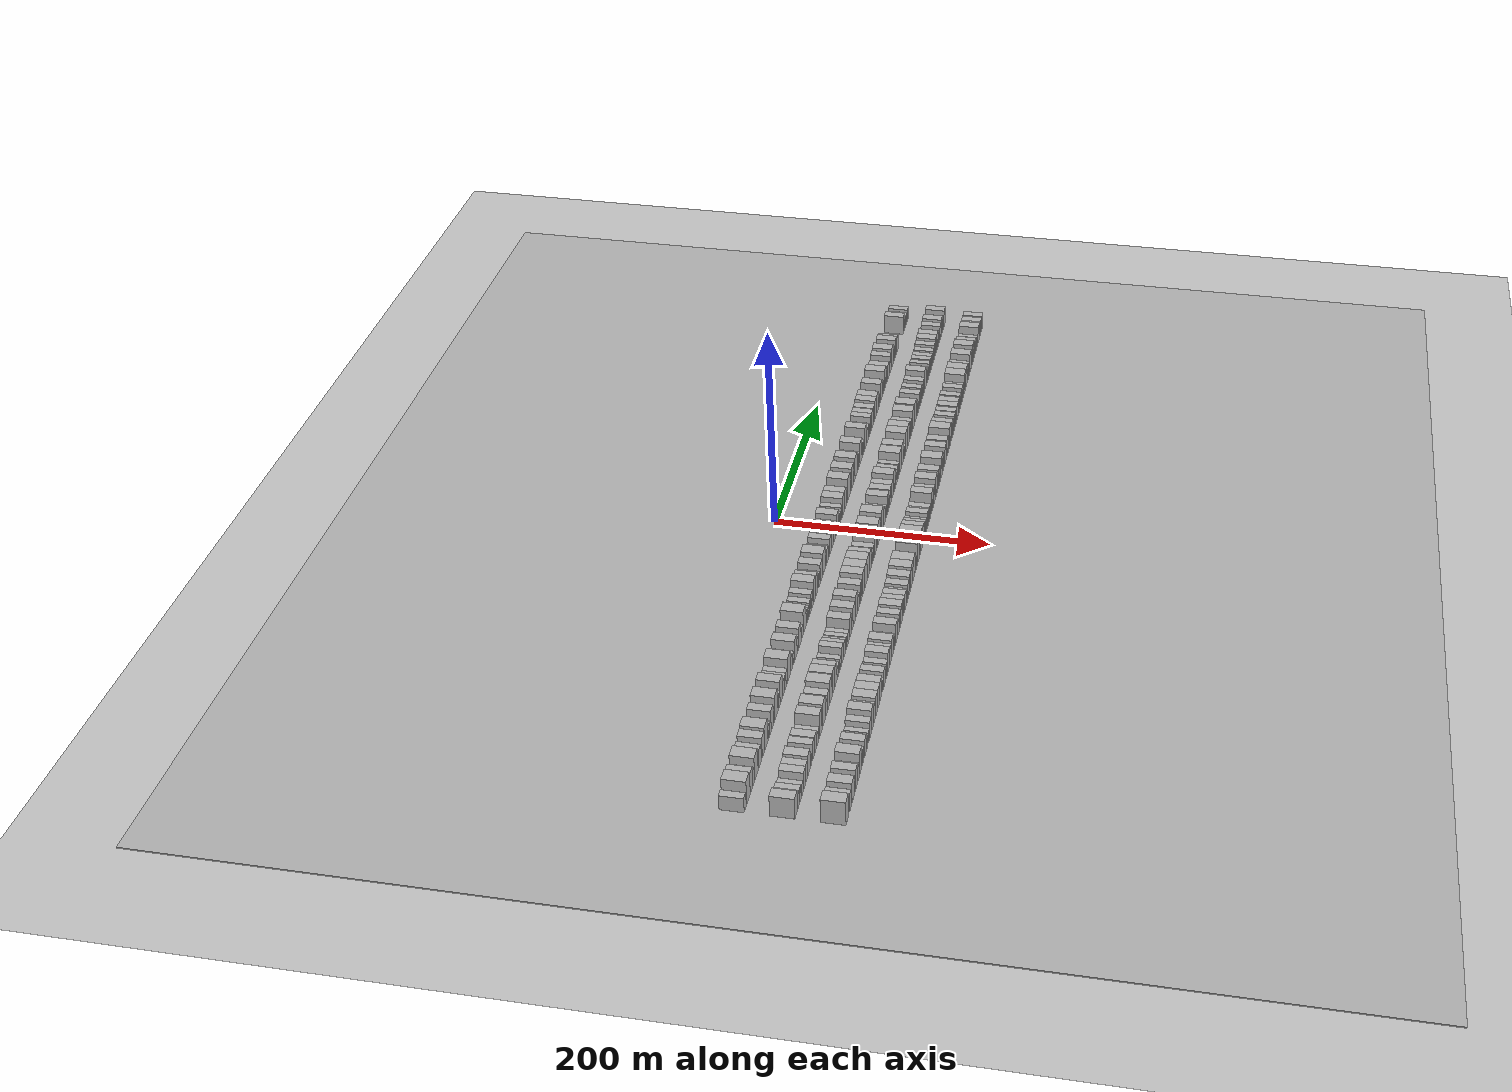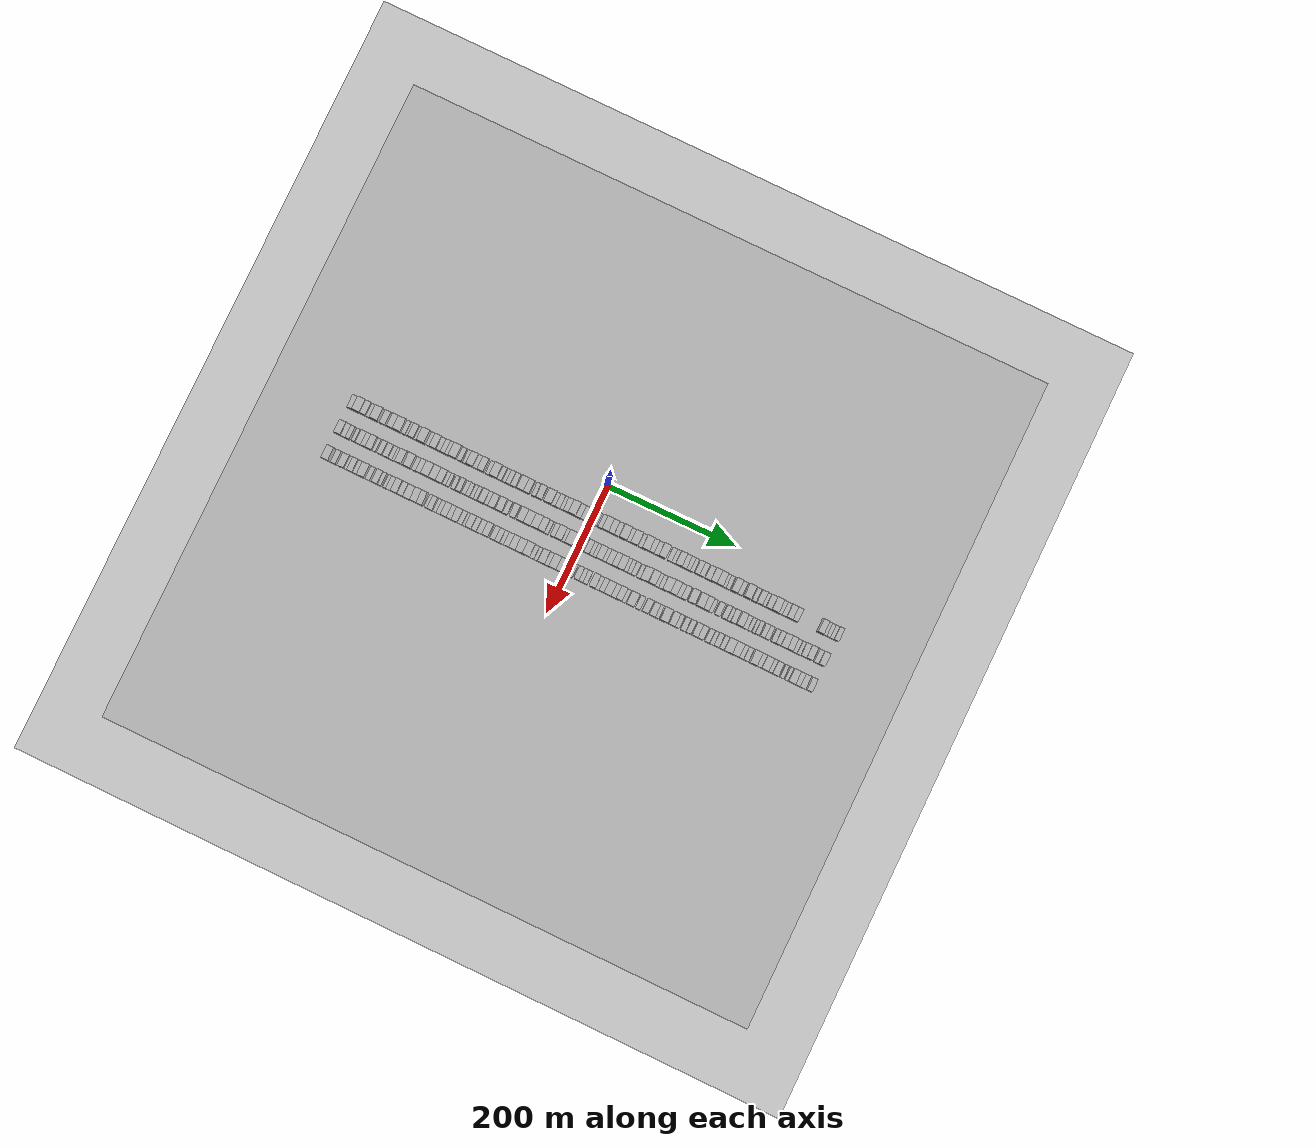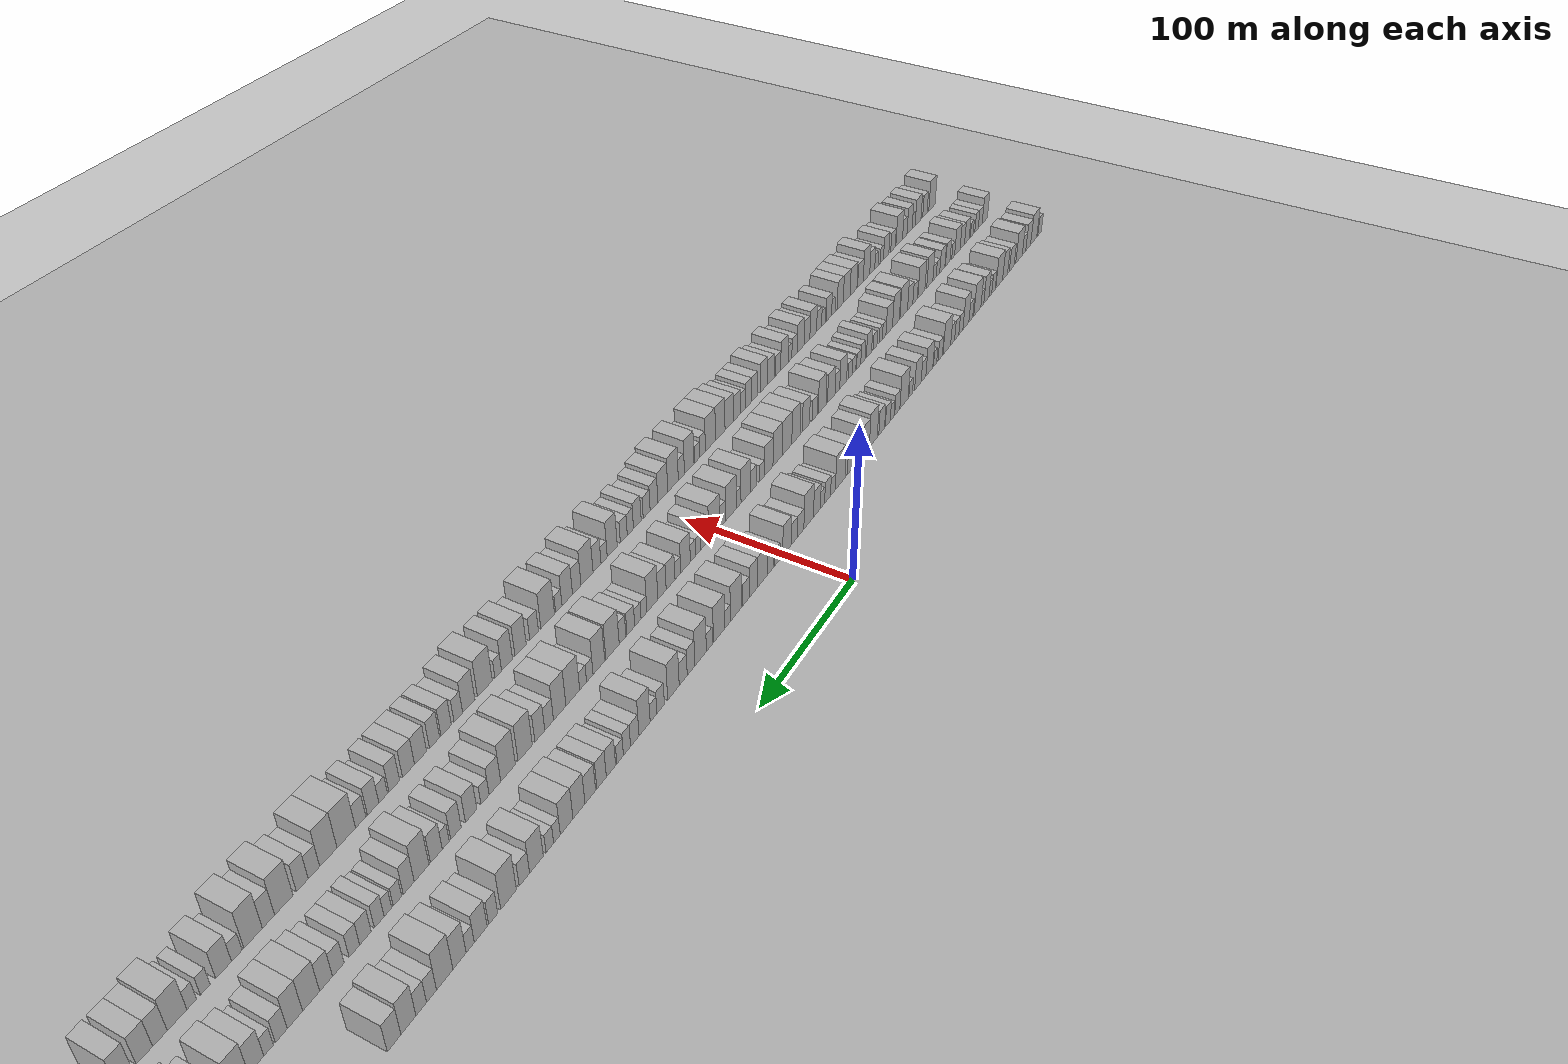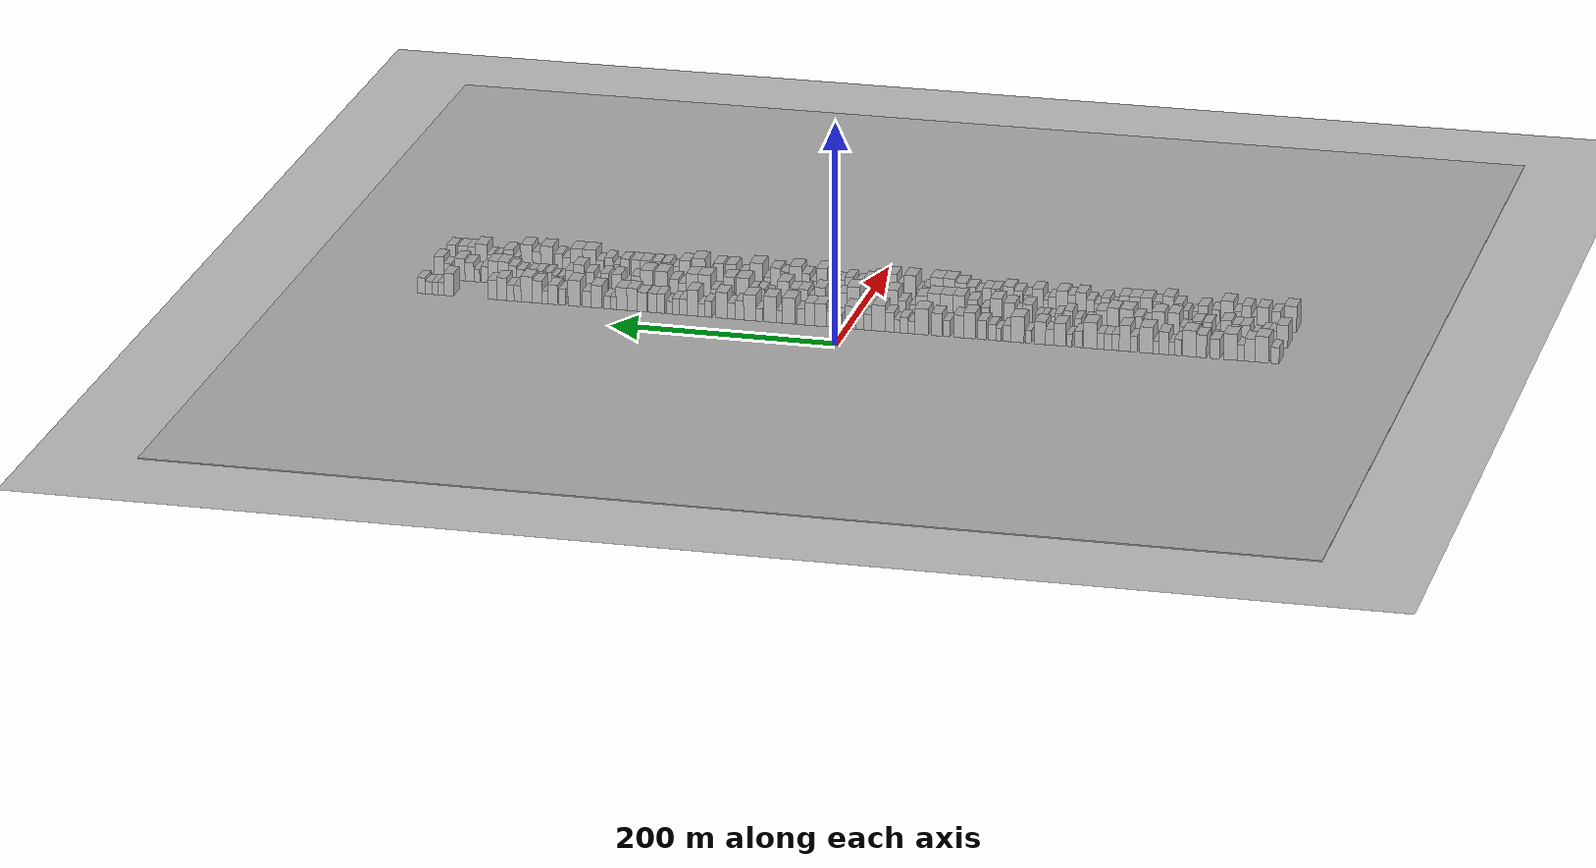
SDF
<?xml version="1.0" encoding="utf-8"?>

<sdf version="1.6">

   <world name="default">

      <gui fullscreen="0">

         <camera name="user_camera">

            <pose>-15 0 4.57585 0 0 0</pose>

            <view_controller>orbit</view_controller>

         </camera>

      </gui>

      <scene>

         <sky>

           <clouds>

             <speed>12</speed>

           </clouds>

         </sky>

         <ambient>0.4 0.4 0.4 1</ambient>

         <background>0.7 0.7 0.7 1</background>

         <shadows>1</shadows>

      </scene>

      <gravity>0 0 -9.8066</gravity>

      <magnetic_field>6e-06 2.3e-05 -4.2e-05</magnetic_field>

      <physics default="0" name="default_physics" type="ode">

         <ode>

            <solver>

               <type>quick</type>

               <iters>10</iters>

               <sor>1.0</sor>

               <use_dynamic_moi_rescaling>0</use_dynamic_moi_rescaling>

            </solver>

            <constraints>

               <cfm>0</cfm>

               <erp>0.2</erp>

               <contact_max_correcting_vel>100</contact_max_correcting_vel>

               <contact_surface_layer>0.001</contact_surface_layer>

            </constraints>

         </ode>

         <max_step_size>0.004</max_step_size>

         <real_time_factor>1</real_time_factor>

         <real_time_update_rate>250</real_time_update_rate>

      </physics>

      <light name="sun" type="directional">

         <cast_shadows>1</cast_shadows>

         <pose>0 0 10 0 0 0</pose>

         <diffuse>0.8 0.8 0.8 1</diffuse>

         <specular>0.2 0.2 0.2 1</specular>

         <attenuation>

            <range>1000</range>

            <constant>0.9</constant>

            <linear>0.01</linear>

            <quadratic>0.001</quadratic>

         </attenuation>

         <direction>-0.5 0.1 -0.9</direction>

      </light>

      <include>

         <name>ground_plane_1</name>

         <uri>model://HANNAS_ground_plane</uri>

         <pose>0 0 0  0 0 0</pose>

      </include>

      <include>

         <name>ground_plane_2</name>

         <uri>model://HANNAS_ground_plane</uri>

         <pose>100 0 0  0 0 0</pose>

      </include>

      <model name="building_1">

         <static>1</static>

         <pose frame="">50.0000 -376.4474 0 0.000000 0.000000 0.000000</pose>

         <link name="link">

            <pose frame="">0 0 7.50 0 0 0</pose>

            <collision name="collision">

               <geometry>

                  <box>

                     <size>20.0000 7.1051 15.0000</size>

                  </box>

               </geometry>

               <max_contacts>10</max_contacts>

               <surface>

                  <contact>

                     <ode/>

                  </contact>

                  <bounce/>

                  <friction>

                     <torsional>

                        <ode/>

                     </torsional>

                     <ode/>

                  </friction>

               </surface>

            </collision>

            <visual name="visual">

               <cast_shadows>0</cast_shadows>

               <geometry>

                  <box>

                     <size>20.0000 7.1051 15.0000</size>

                  </box>

               </geometry>

               <material>

                  <script>

                     <uri>model://HANNAS_wall/materials/scripts</uri>

                     <uri>model://HANNAS_wall/materials/textures</uri>

                     <name>vrc/HANNAS_wall</name>

                  </script>

               </material>

            </visual>

            <self_collide>0</self_collide>

            <enable_wind>0</enable_wind>

            <kinematic>0</kinematic>

         </link>

      </model>

      <model name="building_2">

         <static>1</static>

         <pose frame="">50.0000 -365.0217 0 0.000000 0.000000 0.000000</pose>

         <link name="link">

            <pose frame="">0 0 12.00 0 0 0</pose>

            <collision name="collision">

               <geometry>

                  <box>

                     <size>20.0000 11.7464 24.0000</size>

                  </box>

               </geometry>

               <max_contacts>10</max_contacts>

               <surface>

                  <contact>

                     <ode/>

                  </contact>

                  <bounce/>

                  <friction>

                     <torsional>

                        <ode/>

                     </torsional>

                     <ode/>

                  </friction>

               </surface>

            </collision>

            <visual name="visual">

               <cast_shadows>0</cast_shadows>

               <geometry>

                  <box>

                     <size>20.0000 11.7464 24.0000</size>

                  </box>

               </geometry>

               <material>

                  <script>

                     <uri>model://HANNAS_wall/materials/scripts</uri>

                     <uri>model://HANNAS_wall/materials/textures</uri>

                     <name>vrc/HANNAS_wall</name>

                  </script>

               </material>

            </visual>

            <self_collide>0</self_collide>

            <enable_wind>0</enable_wind>

            <kinematic>0</kinematic>

         </link>

      </model>

      <model name="building_3">

         <static>1</static>

         <pose frame="">50.0000 -354.5544 0 0.000000 0.000000 0.000000</pose>

         <link name="link">

            <pose frame="">0 0 10.50 0 0 0</pose>

            <collision name="collision">

               <geometry>

                  <box>

                     <size>20.0000 9.1883 21.0000</size>

                  </box>

               </geometry>

               <max_contacts>10</max_contacts>

               <surface>

                  <contact>

                     <ode/>

                  </contact>

                  <bounce/>

                  <friction>

                     <torsional>

                        <ode/>

                     </torsional>

                     <ode/>

                  </friction>

               </surface>

            </collision>

            <visual name="visual">

               <cast_shadows>0</cast_shadows>

               <geometry>

                  <box>

                     <size>20.0000 9.1883 21.0000</size>

                  </box>

               </geometry>

               <material>

                  <script>

                     <uri>model://HANNAS_wall/materials/scripts</uri>

                     <uri>model://HANNAS_wall/materials/textures</uri>

                     <name>vrc/HANNAS_wall</name>

                  </script>

               </material>

            </visual>

            <self_collide>0</self_collide>

            <enable_wind>0</enable_wind>

            <kinematic>0</kinematic>

         </link>

      </model>

      <model name="building_4">

         <static>1</static>

         <pose frame="">50.0000 -346.6746 0 0.000000 0.000000 0.000000</pose>

         <link name="link">

            <pose frame="">0 0 7.50 0 0 0</pose>

            <collision name="collision">

               <geometry>

                  <box>

                     <size>20.0000 6.5711 15.0000</size>

                  </box>

               </geometry>

               <max_contacts>10</max_contacts>

               <surface>

                  <contact>

                     <ode/>

                  </contact>

                  <bounce/>

                  <friction>

                     <torsional>

                        <ode/>

                     </torsional>

                     <ode/>

                  </friction>

               </surface>

            </collision>

            <visual name="visual">

               <cast_shadows>0</cast_shadows>

               <geometry>

                  <box>

                     <size>20.0000 6.5711 15.0000</size>

                  </box>

               </geometry>

               <material>

                  <script>

                     <uri>model://HANNAS_wall/materials/scripts</uri>

                     <uri>model://HANNAS_wall/materials/textures</uri>

                     <name>vrc/HANNAS_wall</name>

                  </script>

               </material>

            </visual>

            <self_collide>0</self_collide>

            <enable_wind>0</enable_wind>

            <kinematic>0</kinematic>

         </link>

      </model>

      <model name="building_5">

         <static>1</static>

         <pose frame="">50.0000 -337.4279 0 0.000000 0.000000 0.000000</pose>

         <link name="link">

            <pose frame="">0 0 12.00 0 0 0</pose>

            <collision name="collision">

               <geometry>

                  <box>

                     <size>20.0000 11.9223 24.0000</size>

                  </box>

               </geometry>

               <max_contacts>10</max_contacts>

               <surface>

                  <contact>

                     <ode/>

                  </contact>

                  <bounce/>

                  <friction>

                     <torsional>

                        <ode/>

                     </torsional>

                     <ode/>

                  </friction>

               </surface>

            </collision>

            <visual name="visual">

               <cast_shadows>0</cast_shadows>

               <geometry>

                  <box>

                     <size>20.0000 11.9223 24.0000</size>

                  </box>

               </geometry>

               <material>

                  <script>

                     <uri>model://HANNAS_wall/materials/scripts</uri>

                     <uri>model://HANNAS_wall/materials/textures</uri>

                     <name>vrc/HANNAS_wall</name>

                  </script>

               </material>

            </visual>

            <self_collide>0</self_collide>

            <enable_wind>0</enable_wind>

            <kinematic>0</kinematic>

         </link>

      </model>

      <model name="building_6">

         <static>1</static>

         <pose frame="">50.0000 -324.0828 0 0.000000 0.000000 0.000000</pose>

         <link name="link">

            <pose frame="">0 0 9.00 0 0 0</pose>

            <collision name="collision">

               <geometry>

                  <box>

                     <size>20.0000 8.7679 18.0000</size>

                  </box>

               </geometry>

               <max_contacts>10</max_contacts>

               <surface>

                  <contact>

                     <ode/>

                  </contact>

                  <bounce/>

                  <friction>

                     <torsional>

                        <ode/>

                     </torsional>

                     <ode/>

                  </friction>

               </surface>

            </collision>

            <visual name="visual">

               <cast_shadows>0</cast_shadows>

               <geometry>

                  <box>

                     <size>20.0000 8.7679 18.0000</size>

                  </box>

               </geometry>

               <material>

                  <script>

                     <uri>model://HANNAS_wall/materials/scripts</uri>

                     <uri>model://HANNAS_wall/materials/textures</uri>

                     <name>vrc/HANNAS_wall</name>

                  </script>

               </material>

            </visual>

            <self_collide>0</self_collide>

            <enable_wind>0</enable_wind>

            <kinematic>0</kinematic>

         </link>

      </model>

      <model name="building_7">

         <static>1</static>

         <pose frame="">50.0000 -312.1704 0 0.000000 0.000000 0.000000</pose>

         <link name="link">

            <pose frame="">0 0 10.50 0 0 0</pose>

            <collision name="collision">

               <geometry>

                  <box>

                     <size>20.0000 9.0568 21.0000</size>

                  </box>

               </geometry>

               <max_contacts>10</max_contacts>

               <surface>

                  <contact>

                     <ode/>

                  </contact>

                  <bounce/>

                  <friction>

                     <torsional>

                        <ode/>

                     </torsional>

                     <ode/>

                  </friction>

               </surface>

            </collision>

            <visual name="visual">

               <cast_shadows>0</cast_shadows>

               <geometry>

                  <box>

                     <size>20.0000 9.0568 21.0000</size>

                  </box>

               </geometry>

               <material>

                  <script>

                     <uri>model://HANNAS_wall/materials/scripts</uri>

                     <uri>model://HANNAS_wall/materials/textures</uri>

                     <name>vrc/HANNAS_wall</name>

                  </script>

               </material>

            </visual>

            <self_collide>0</self_collide>

            <enable_wind>0</enable_wind>

            <kinematic>0</kinematic>

         </link>

      </model>

      <model name="building_8">

         <static>1</static>

         <pose frame="">50.0000 -301.7070 0 0.000000 0.000000 0.000000</pose>

         <link name="link">

            <pose frame="">0 0 12.00 0 0 0</pose>

            <collision name="collision">

               <geometry>

                  <box>

                     <size>20.0000 11.8700 24.0000</size>

                  </box>

               </geometry>

               <max_contacts>10</max_contacts>

               <surface>

                  <contact>

                     <ode/>

                  </contact>

                  <bounce/>

                  <friction>

                     <torsional>

                        <ode/>

                     </torsional>

                     <ode/>

                  </friction>

               </surface>

            </collision>

            <visual name="visual">

               <cast_shadows>0</cast_shadows>

               <geometry>

                  <box>

                     <size>20.0000 11.8700 24.0000</size>

                  </box>

               </geometry>

               <material>

                  <script>

                     <uri>model://HANNAS_wall/materials/scripts</uri>

                     <uri>model://HANNAS_wall/materials/textures</uri>

                     <name>vrc/HANNAS_wall</name>

                  </script>

               </material>

            </visual>

            <self_collide>0</self_collide>

            <enable_wind>0</enable_wind>

            <kinematic>0</kinematic>

         </link>

      </model>

      <model name="building_9">

         <static>1</static>

         <pose frame="">50.0000 -291.7434 0 0.000000 0.000000 0.000000</pose>

         <link name="link">

            <pose frame="">0 0 7.50 0 0 0</pose>

            <collision name="collision">

               <geometry>

                  <box>

                     <size>20.0000 6.0571 15.0000</size>

                  </box>

               </geometry>

               <max_contacts>10</max_contacts>

               <surface>

                  <contact>

                     <ode/>

                  </contact>

                  <bounce/>

                  <friction>

                     <torsional>

                        <ode/>

                     </torsional>

                     <ode/>

                  </friction>

               </surface>

            </collision>

            <visual name="visual">

               <cast_shadows>0</cast_shadows>

               <geometry>

                  <box>

                     <size>20.0000 6.0571 15.0000</size>

                  </box>

               </geometry>

               <material>

                  <script>

                     <uri>model://HANNAS_wall/materials/scripts</uri>

                     <uri>model://HANNAS_wall/materials/textures</uri>

                     <name>vrc/HANNAS_wall</name>

                  </script>

               </material>

            </visual>

            <self_collide>0</self_collide>

            <enable_wind>0</enable_wind>

            <kinematic>0</kinematic>

         </link>

      </model>

      <model name="building_10">

         <static>1</static>

         <pose frame="">50.0000 -286.2814 0 0.000000 0.000000 0.000000</pose>

         <link name="link">

            <pose frame="">0 0 6.00 0 0 0</pose>

            <collision name="collision">

               <geometry>

                  <box>

                     <size>20.0000 4.8668 12.0000</size>

                  </box>

               </geometry>

               <max_contacts>10</max_contacts>

               <surface>

                  <contact>

                     <ode/>

                  </contact>

                  <bounce/>

                  <friction>

                     <torsional>

                        <ode/>

                     </torsional>

                     <ode/>

                  </friction>

               </surface>

            </collision>

            <visual name="visual">

               <cast_shadows>0</cast_shadows>

               <geometry>

                  <box>

                     <size>20.0000 4.8668 12.0000</size>

                  </box>

               </geometry>

               <material>

                  <script>

                     <uri>model://HANNAS_wall/materials/scripts</uri>

                     <uri>model://HANNAS_wall/materials/textures</uri>

                     <name>vrc/HANNAS_wall</name>

                  </script>

               </material>

            </visual>

            <self_collide>0</self_collide>

            <enable_wind>0</enable_wind>

            <kinematic>0</kinematic>

         </link>

      </model>

      <model name="building_11">

         <static>1</static>

         <pose frame="">50.0000 -279.4507 0 0.000000 0.000000 0.000000</pose>

         <link name="link">

            <pose frame="">0 0 10.50 0 0 0</pose>

            <collision name="collision">

               <geometry>

                  <box>

                     <size>20.0000 8.7948 21.0000</size>

                  </box>

               </geometry>

               <max_contacts>10</max_contacts>

               <surface>

                  <contact>

                     <ode/>

                  </contact>

                  <bounce/>

                  <friction>

                     <torsional>

                        <ode/>

                     </torsional>

                     <ode/>

                  </friction>

               </surface>

            </collision>

            <visual name="visual">

               <cast_shadows>0</cast_shadows>

               <geometry>

                  <box>

                     <size>20.0000 8.7948 21.0000</size>

                  </box>

               </geometry>

               <material>

                  <script>

                     <uri>model://HANNAS_wall/materials/scripts</uri>

                     <uri>model://HANNAS_wall/materials/textures</uri>

                     <name>vrc/HANNAS_wall</name>

                  </script>

               </material>

            </visual>

            <self_collide>0</self_collide>

            <enable_wind>0</enable_wind>

            <kinematic>0</kinematic>

         </link>

      </model>

      <model name="building_12">

         <static>1</static>

         <pose frame="">50.0000 -272.5724 0 0.000000 0.000000 0.000000</pose>

         <link name="link">

            <pose frame="">0 0 6.00 0 0 0</pose>

            <collision name="collision">

               <geometry>

                  <box>

                     <size>20.0000 4.9618 12.0000</size>

                  </box>

               </geometry>

               <max_contacts>10</max_contacts>

               <surface>

                  <contact>

                     <ode/>

                  </contact>

                  <bounce/>

                  <friction>

                     <torsional>

                        <ode/>

                     </torsional>

                     <ode/>

                  </friction>

               </surface>

            </collision>

            <visual name="visual">

               <cast_shadows>0</cast_shadows>

               <geometry>

                  <box>

                     <size>20.0000 4.9618 12.0000</size>

                  </box>

               </geometry>

               <material>

                  <script>

                     <uri>model://HANNAS_wall/materials/scripts</uri>

                     <uri>model://HANNAS_wall/materials/textures</uri>

                     <name>vrc/HANNAS_wall</name>

                  </script>

               </material>

            </visual>

            <self_collide>0</self_collide>

            <enable_wind>0</enable_wind>

            <kinematic>0</kinematic>

         </link>

      </model>

      <model name="building_13">

         <static>1</static>

         <pose frame="">50.0000 -264.2122 0 0.000000 0.000000 0.000000</pose>

         <link name="link">

            <pose frame="">0 0 12.00 0 0 0</pose>

            <collision name="collision">

               <geometry>

                  <box>

                     <size>20.0000 11.7585 24.0000</size>

                  </box>

               </geometry>

               <max_contacts>10</max_contacts>

               <surface>

                  <contact>

                     <ode/>

                  </contact>

                  <bounce/>

                  <friction>

                     <torsional>

                        <ode/>

                     </torsional>

                     <ode/>

                  </friction>

               </surface>

            </collision>

            <visual name="visual">

               <cast_shadows>0</cast_shadows>

               <geometry>

                  <box>

                     <size>20.0000 11.7585 24.0000</size>

                  </box>

               </geometry>

               <material>

                  <script>

                     <uri>model://HANNAS_wall/materials/scripts</uri>

                     <uri>model://HANNAS_wall/materials/textures</uri>

                     <name>vrc/HANNAS_wall</name>

                  </script>

               </material>

            </visual>

            <self_collide>0</self_collide>

            <enable_wind>0</enable_wind>

            <kinematic>0</kinematic>

         </link>

      </model>

      <model name="building_14">

         <static>1</static>

         <pose frame="">50.0000 -253.2306 0 0.000000 0.000000 0.000000</pose>

         <link name="link">

            <pose frame="">0 0 7.50 0 0 0</pose>

            <collision name="collision">

               <geometry>

                  <box>

                     <size>20.0000 6.2049 15.0000</size>

                  </box>

               </geometry>

               <max_contacts>10</max_contacts>

               <surface>

                  <contact>

                     <ode/>

                  </contact>

                  <bounce/>

                  <friction>

                     <torsional>

                        <ode/>

                     </torsional>

                     <ode/>

                  </friction>

               </surface>

            </collision>

            <visual name="visual">

               <cast_shadows>0</cast_shadows>

               <geometry>

                  <box>

                     <size>20.0000 6.2049 15.0000</size>

                  </box>

               </geometry>

               <material>

                  <script>

                     <uri>model://HANNAS_wall/materials/scripts</uri>

                     <uri>model://HANNAS_wall/materials/textures</uri>

                     <name>vrc/HANNAS_wall</name>

                  </script>

               </material>

            </visual>

            <self_collide>0</self_collide>

            <enable_wind>0</enable_wind>

            <kinematic>0</kinematic>

         </link>

      </model>

      <model name="building_15">

         <static>1</static>

         <pose frame="">50.0000 -245.2657 0 0.000000 0.000000 0.000000</pose>

         <link name="link">

            <pose frame="">0 0 12.00 0 0 0</pose>

            <collision name="collision">

               <geometry>

                  <box>

                     <size>20.0000 9.7249 24.0000</size>

                  </box>

               </geometry>

               <max_contacts>10</max_contacts>

               <surface>

                  <contact>

                     <ode/>

                  </contact>

                  <bounce/>

                  <friction>

                     <torsional>

                        <ode/>

                     </torsional>

                     <ode/>

                  </friction>

               </surface>

            </collision>

            <visual name="visual">

               <cast_shadows>0</cast_shadows>

               <geometry>

                  <box>

                     <size>20.0000 9.7249 24.0000</size>

                  </box>

               </geometry>

               <material>

                  <script>

                     <uri>model://HANNAS_wall/materials/scripts</uri>

                     <uri>model://HANNAS_wall/materials/textures</uri>

                     <name>vrc/HANNAS_wall</name>

                  </script>

               </material>

            </visual>

            <self_collide>0</self_collide>

            <enable_wind>0</enable_wind>

            <kinematic>0</kinematic>

         </link>

      </model>

      <model name="building_16">

         <static>1</static>

         <pose frame="">50.0000 -237.1206 0 0.000000 0.000000 0.000000</pose>

         <link name="link">

            <pose frame="">0 0 7.50 0 0 0</pose>

            <collision name="collision">

               <geometry>

                  <box>

                     <size>20.0000 6.5652 15.0000</size>

                  </box>

               </geometry>

               <max_contacts>10</max_contacts>

               <surface>

                  <contact>

                     <ode/>

                  </contact>

                  <bounce/>

                  <friction>

                     <torsional>

                        <ode/>

                     </torsional>

                     <ode/>

                  </friction>

               </surface>

            </collision>

            <visual name="visual">

               <cast_shadows>0</cast_shadows>

               <geometry>

                  <box>

                     <size>20.0000 6.5652 15.0000</size>

                  </box>

               </geometry>

               <material>

                  <script>

                     <uri>model://HANNAS_wall/materials/scripts</uri>

                     <uri>model://HANNAS_wall/materials/textures</uri>

                     <name>vrc/HANNAS_wall</name>

                  </script>

               </material>

            </visual>

            <self_collide>0</self_collide>

            <enable_wind>0</enable_wind>

            <kinematic>0</kinematic>

         </link>

      </model>

      <model name="building_17">

         <static>1</static>

         <pose frame="">50.0000 -230.4647 0 0.000000 0.000000 0.000000</pose>

         <link name="link">

            <pose frame="">0 0 7.50 0 0 0</pose>

            <collision name="collision">

               <geometry>

                  <box>

                     <size>20.0000 6.7467 15.0000</size>

                  </box>

               </geometry>

               <max_contacts>10</max_contacts>

               <surface>

                  <contact>

                     <ode/>

                  </contact>

                  <bounce/>

                  <friction>

                     <torsional>

                        <ode/>

                     </torsional>

                     <ode/>

                  </friction>

               </surface>

            </collision>

            <visual name="visual">

               <cast_shadows>0</cast_shadows>

               <geometry>

                  <box>

                     <size>20.0000 6.7467 15.0000</size>

                  </box>

               </geometry>

               <material>

                  <script>

                     <uri>model://HANNAS_wall/materials/scripts</uri>

                     <uri>model://HANNAS_wall/materials/textures</uri>

                     <name>vrc/HANNAS_wall</name>

                  </script>

               </material>

            </visual>

            <self_collide>0</self_collide>

            <enable_wind>0</enable_wind>

            <kinematic>0</kinematic>

         </link>

      </model>

      <model name="building_18">

         <static>1</static>

         <pose frame="">50.0000 -223.9192 0 0.000000 0.000000 0.000000</pose>

         <link name="link">

            <pose frame="">0 0 7.50 0 0 0</pose>

            <collision name="collision">

               <geometry>

                  <box>

                     <size>20.0000 6.3443 15.0000</size>

                  </box>

               </geometry>

               <max_contacts>10</max_contacts>

               <surface>

                  <contact>

                     <ode/>

                  </contact>

                  <bounce/>

                  <friction>

                     <torsional>

                        <ode/>

                     </torsional>

                     <ode/>

                  </friction>

               </surface>

            </collision>

            <visual name="visual">

               <cast_shadows>0</cast_shadows>

               <geometry>

                  <box>

                     <size>20.0000 6.3443 15.0000</size>

                  </box>

               </geometry>

               <material>

                  <script>

                     <uri>model://HANNAS_wall/materials/scripts</uri>

                     <uri>model://HANNAS_wall/materials/textures</uri>

                     <name>vrc/HANNAS_wall</name>

                  </script>

               </material>

            </visual>

            <self_collide>0</self_collide>

            <enable_wind>0</enable_wind>

            <kinematic>0</kinematic>

         </link>

      </model>

      <model name="building_19">

         <static>1</static>

         <pose frame="">50.0000 -214.8182 0 0.000000 0.000000 0.000000</pose>

         <link name="link">

            <pose frame="">0 0 12.00 0 0 0</pose>

            <collision name="collision">

               <geometry>

                  <box>

                     <size>20.0000 11.8577 24.0000</size>

                  </box>

               </geometry>

               <max_contacts>10</max_contacts>

               <surface>

                  <contact>

                     <ode/>

                  </contact>

                  <bounce/>

                  <friction>

                     <torsional>

                        <ode/>

                     </torsional>

                     <ode/>

                  </friction>

               </surface>

            </collision>

            <visual name="visual">

               <cast_shadows>0</cast_shadows>

               <geometry>

                  <box>

                     <size>20.0000 11.8577 24.0000</size>

                  </box>

               </geometry>

               <material>

                  <script>

                     <uri>model://HANNAS_wall/materials/scripts</uri>

                     <uri>model://HANNAS_wall/materials/textures</uri>

                     <name>vrc/HANNAS_wall</name>

                  </script>

               </material>

            </visual>

            <self_collide>0</self_collide>

            <enable_wind>0</enable_wind>

            <kinematic>0</kinematic>

         </link>

      </model>

      <model name="building_20">

         <static>1</static>

         <pose frame="">50.0000 -204.5173 0 0.000000 0.000000 0.000000</pose>

         <link name="link">

            <pose frame="">0 0 7.50 0 0 0</pose>

            <collision name="collision">

               <geometry>

                  <box>

                     <size>20.0000 6.7441 15.0000</size>

                  </box>

               </geometry>

               <max_contacts>10</max_contacts>

               <surface>

                  <contact>

                     <ode/>

                  </contact>

                  <bounce/>

                  <friction>

                     <torsional>

                        <ode/>

                     </torsional>

                     <ode/>

                  </friction>

               </surface>

            </collision>

            <visual name="visual">

               <cast_shadows>0</cast_shadows>

               <geometry>

                  <box>

                     <size>20.0000 6.7441 15.0000</size>

                  </box>

               </geometry>

               <material>

                  <script>

                     <uri>model://HANNAS_wall/materials/scripts</uri>

                     <uri>model://HANNAS_wall/materials/textures</uri>

                     <name>vrc/HANNAS_wall</name>

                  </script>

               </material>

            </visual>

            <self_collide>0</self_collide>

            <enable_wind>0</enable_wind>

            <kinematic>0</kinematic>

         </link>

      </model>

      <model name="building_21">

         <static>1</static>

         <pose frame="">50.0000 -196.6896 0 0.000000 0.000000 0.000000</pose>

         <link name="link">

            <pose frame="">0 0 6.00 0 0 0</pose>

            <collision name="collision">

               <geometry>

                  <box>

                     <size>20.0000 4.9112 12.0000</size>

                  </box>

               </geometry>

               <max_contacts>10</max_contacts>

               <surface>

                  <contact>

                     <ode/>

                  </contact>

                  <bounce/>

                  <friction>

                     <torsional>

                        <ode/>

                     </torsional>

                     <ode/>

                  </friction>

               </surface>

            </collision>

            <visual name="visual">

               <cast_shadows>0</cast_shadows>

               <geometry>

                  <box>

                     <size>20.0000 4.9112 12.0000</size>

                  </box>

               </geometry>

               <material>

                  <script>

                     <uri>model://HANNAS_wall/materials/scripts</uri>

                     <uri>model://HANNAS_wall/materials/textures</uri>

                     <name>vrc/HANNAS_wall</name>

                  </script>

               </material>

            </visual>

            <self_collide>0</self_collide>

            <enable_wind>0</enable_wind>

            <kinematic>0</kinematic>

         </link>

      </model>

      <model name="building_22">

         <static>1</static>

         <pose frame="">50.0000 -188.0710 0 0.000000 0.000000 0.000000</pose>

         <link name="link">

            <pose frame="">0 0 10.50 0 0 0</pose>

            <collision name="collision">

               <geometry>

                  <box>

                     <size>20.0000 10.3260 21.0000</size>

                  </box>

               </geometry>

               <max_contacts>10</max_contacts>

               <surface>

                  <contact>

                     <ode/>

                  </contact>

                  <bounce/>

                  <friction>

                     <torsional>

                        <ode/>

                     </torsional>

                     <ode/>

                  </friction>

               </surface>

            </collision>

            <visual name="visual">

               <cast_shadows>0</cast_shadows>

               <geometry>

                  <box>

                     <size>20.0000 10.3260 21.0000</size>

                  </box>

               </geometry>

               <material>

                  <script>

                     <uri>model://HANNAS_wall/materials/scripts</uri>

                     <uri>model://HANNAS_wall/materials/textures</uri>

                     <name>vrc/HANNAS_wall</name>

                  </script>

               </material>

            </visual>

            <self_collide>0</self_collide>

            <enable_wind>0</enable_wind>

            <kinematic>0</kinematic>

         </link>

      </model>

      <model name="building_23">

         <static>1</static>

         <pose frame="">50.0000 -179.3668 0 0.000000 0.000000 0.000000</pose>

         <link name="link">

            <pose frame="">0 0 7.50 0 0 0</pose>

            <collision name="collision">

               <geometry>

                  <box>

                     <size>20.0000 7.0824 15.0000</size>

                  </box>

               </geometry>

               <max_contacts>10</max_contacts>

               <surface>

                  <contact>

                     <ode/>

                  </contact>

                  <bounce/>

                  <friction>

                     <torsional>

                        <ode/>

                     </torsional>

                     <ode/>

                  </friction>

               </surface>

            </collision>

            <visual name="visual">

               <cast_shadows>0</cast_shadows>

               <geometry>

                  <box>

                     <size>20.0000 7.0824 15.0000</size>

                  </box>

               </geometry>

               <material>

                  <script>

                     <uri>model://HANNAS_wall/materials/scripts</uri>

                     <uri>model://HANNAS_wall/materials/textures</uri>

                     <name>vrc/HANNAS_wall</name>

                  </script>

               </material>

            </visual>

            <self_collide>0</self_collide>

            <enable_wind>0</enable_wind>

            <kinematic>0</kinematic>

         </link>

      </model>

      <model name="building_24">

         <static>1</static>

         <pose frame="">50.0000 -171.0343 0 0.000000 0.000000 0.000000</pose>

         <link name="link">

            <pose frame="">0 0 10.50 0 0 0</pose>

            <collision name="collision">

               <geometry>

                  <box>

                     <size>20.0000 9.5826 21.0000</size>

                  </box>

               </geometry>

               <max_contacts>10</max_contacts>

               <surface>

                  <contact>

                     <ode/>

                  </contact>

                  <bounce/>

                  <friction>

                     <torsional>

                        <ode/>

                     </torsional>

                     <ode/>

                  </friction>

               </surface>

            </collision>

            <visual name="visual">

               <cast_shadows>0</cast_shadows>

               <geometry>

                  <box>

                     <size>20.0000 9.5826 21.0000</size>

                  </box>

               </geometry>

               <material>

                  <script>

                     <uri>model://HANNAS_wall/materials/scripts</uri>

                     <uri>model://HANNAS_wall/materials/textures</uri>

                     <name>vrc/HANNAS_wall</name>

                  </script>

               </material>

            </visual>

            <self_collide>0</self_collide>

            <enable_wind>0</enable_wind>

            <kinematic>0</kinematic>

         </link>

      </model>

      <model name="building_25">

         <static>1</static>

         <pose frame="">50.0000 -160.5627 0 0.000000 0.000000 0.000000</pose>

         <link name="link">

            <pose frame="">0 0 6.00 0 0 0</pose>

            <collision name="collision">

               <geometry>

                  <box>

                     <size>20.0000 5.3607 12.0000</size>

                  </box>

               </geometry>

               <max_contacts>10</max_contacts>

               <surface>

                  <contact>

                     <ode/>

                  </contact>

                  <bounce/>

                  <friction>

                     <torsional>

                        <ode/>

                     </torsional>

                     <ode/>

                  </friction>

               </surface>

            </collision>

            <visual name="visual">

               <cast_shadows>0</cast_shadows>

               <geometry>

                  <box>

                     <size>20.0000 5.3607 12.0000</size>

                  </box>

               </geometry>

               <material>

                  <script>

                     <uri>model://HANNAS_wall/materials/scripts</uri>

                     <uri>model://HANNAS_wall/materials/textures</uri>

                     <name>vrc/HANNAS_wall</name>

                  </script>

               </material>

            </visual>

            <self_collide>0</self_collide>

            <enable_wind>0</enable_wind>

            <kinematic>0</kinematic>

         </link>

      </model>

      <model name="building_26">

         <static>1</static>

         <pose frame="">50.0000 -151.0339 0 0.000000 0.000000 0.000000</pose>

         <link name="link">

            <pose frame="">0 0 12.00 0 0 0</pose>

            <collision name="collision">

               <geometry>

                  <box>

                     <size>20.0000 11.6970 24.0000</size>

                  </box>

               </geometry>

               <max_contacts>10</max_contacts>

               <surface>

                  <contact>

                     <ode/>

                  </contact>

                  <bounce/>

                  <friction>

                     <torsional>

                        <ode/>

                     </torsional>

                     <ode/>

                  </friction>

               </surface>

            </collision>

            <visual name="visual">

               <cast_shadows>0</cast_shadows>

               <geometry>

                  <box>

                     <size>20.0000 11.6970 24.0000</size>

                  </box>

               </geometry>

               <material>

                  <script>

                     <uri>model://HANNAS_wall/materials/scripts</uri>

                     <uri>model://HANNAS_wall/materials/textures</uri>

                     <name>vrc/HANNAS_wall</name>

                  </script>

               </material>

            </visual>

            <self_collide>0</self_collide>

            <enable_wind>0</enable_wind>

            <kinematic>0</kinematic>

         </link>

      </model>

      <model name="building_27">

         <static>1</static>

         <pose frame="">50.0000 -141.5836 0 0.000000 0.000000 0.000000</pose>

         <link name="link">

            <pose frame="">0 0 7.50 0 0 0</pose>

            <collision name="collision">

               <geometry>

                  <box>

                     <size>20.0000 7.2035 15.0000</size>

                  </box>

               </geometry>

               <max_contacts>10</max_contacts>

               <surface>

                  <contact>

                     <ode/>

                  </contact>

                  <bounce/>

                  <friction>

                     <torsional>

                        <ode/>

                     </torsional>

                     <ode/>

                  </friction>

               </surface>

            </collision>

            <visual name="visual">

               <cast_shadows>0</cast_shadows>

               <geometry>

                  <box>

                     <size>20.0000 7.2035 15.0000</size>

                  </box>

               </geometry>

               <material>

                  <script>

                     <uri>model://HANNAS_wall/materials/scripts</uri>

                     <uri>model://HANNAS_wall/materials/textures</uri>

                     <name>vrc/HANNAS_wall</name>

                  </script>

               </material>

            </visual>

            <self_collide>0</self_collide>

            <enable_wind>0</enable_wind>

            <kinematic>0</kinematic>

         </link>

      </model>

      <model name="building_28">

         <static>1</static>

         <pose frame="">50.0000 -134.4187 0 0.000000 0.000000 0.000000</pose>

         <link name="link">

            <pose frame="">0 0 6.00 0 0 0</pose>

            <collision name="collision">

               <geometry>

                  <box>

                     <size>20.0000 5.1263 12.0000</size>

                  </box>

               </geometry>

               <max_contacts>10</max_contacts>

               <surface>

                  <contact>

                     <ode/>

                  </contact>

                  <bounce/>

                  <friction>

                     <torsional>

                        <ode/>

                     </torsional>

                     <ode/>

                  </friction>

               </surface>

            </collision>

            <visual name="visual">

               <cast_shadows>0</cast_shadows>

               <geometry>

                  <box>

                     <size>20.0000 5.1263 12.0000</size>

                  </box>

               </geometry>

               <material>

                  <script>

                     <uri>model://HANNAS_wall/materials/scripts</uri>

                     <uri>model://HANNAS_wall/materials/textures</uri>

                     <name>vrc/HANNAS_wall</name>

                  </script>

               </material>

            </visual>

            <self_collide>0</self_collide>

            <enable_wind>0</enable_wind>

            <kinematic>0</kinematic>

         </link>

      </model>

      <model name="building_29">

         <static>1</static>

         <pose frame="">50.0000 -128.4130 0 0.000000 0.000000 0.000000</pose>

         <link name="link">

            <pose frame="">0 0 7.50 0 0 0</pose>

            <collision name="collision">

               <geometry>

                  <box>

                     <size>20.0000 6.8850 15.0000</size>

                  </box>

               </geometry>

               <max_contacts>10</max_contacts>

               <surface>

                  <contact>

                     <ode/>

                  </contact>

                  <bounce/>

                  <friction>

                     <torsional>

                        <ode/>

                     </torsional>

                     <ode/>

                  </friction>

               </surface>

            </collision>

            <visual name="visual">

               <cast_shadows>0</cast_shadows>

               <geometry>

                  <box>

                     <size>20.0000 6.8850 15.0000</size>

                  </box>

               </geometry>

               <material>

                  <script>

                     <uri>model://HANNAS_wall/materials/scripts</uri>

                     <uri>model://HANNAS_wall/materials/textures</uri>

                     <name>vrc/HANNAS_wall</name>

                  </script>

               </material>

            </visual>

            <self_collide>0</self_collide>

            <enable_wind>0</enable_wind>

            <kinematic>0</kinematic>

         </link>

      </model>

      <model name="building_30">

         <static>1</static>

         <pose frame="">50.0000 -120.0575 0 0.000000 0.000000 0.000000</pose>

         <link name="link">

            <pose frame="">0 0 9.00 0 0 0</pose>

            <collision name="collision">

               <geometry>

                  <box>

                     <size>20.0000 7.8259 18.0000</size>

                  </box>

               </geometry>

               <max_contacts>10</max_contacts>

               <surface>

                  <contact>

                     <ode/>

                  </contact>

                  <bounce/>

                  <friction>

                     <torsional>

                        <ode/>

                     </torsional>

                     <ode/>

                  </friction>

               </surface>

            </collision>

            <visual name="visual">

               <cast_shadows>0</cast_shadows>

               <geometry>

                  <box>

                     <size>20.0000 7.8259 18.0000</size>

                  </box>

               </geometry>

               <material>

                  <script>

                     <uri>model://HANNAS_wall/materials/scripts</uri>

                     <uri>model://HANNAS_wall/materials/textures</uri>

                     <name>vrc/HANNAS_wall</name>

                  </script>

               </material>

            </visual>

            <self_collide>0</self_collide>

            <enable_wind>0</enable_wind>

            <kinematic>0</kinematic>

         </link>

      </model>

      <model name="building_31">

         <static>1</static>

         <pose frame="">50.0000 -108.8472 0 0.000000 0.000000 0.000000</pose>

         <link name="link">

            <pose frame="">0 0 12.00 0 0 0</pose>

            <collision name="collision">

               <geometry>

                  <box>

                     <size>20.0000 10.5947 24.0000</size>

                  </box>

               </geometry>

               <max_contacts>10</max_contacts>

               <surface>

                  <contact>

                     <ode/>

                  </contact>

                  <bounce/>

                  <friction>

                     <torsional>

                        <ode/>

                     </torsional>

                     <ode/>

                  </friction>

               </surface>

            </collision>

            <visual name="visual">

               <cast_shadows>0</cast_shadows>

               <geometry>

                  <box>

                     <size>20.0000 10.5947 24.0000</size>

                  </box>

               </geometry>

               <material>

                  <script>

                     <uri>model://HANNAS_wall/materials/scripts</uri>

                     <uri>model://HANNAS_wall/materials/textures</uri>

                     <name>vrc/HANNAS_wall</name>

                  </script>

               </material>

            </visual>

            <self_collide>0</self_collide>

            <enable_wind>0</enable_wind>

            <kinematic>0</kinematic>

         </link>

      </model>

      <model name="building_32">

         <static>1</static>

         <pose frame="">50.0000 -99.1492 0 0.000000 0.000000 0.000000</pose>

         <link name="link">

            <pose frame="">0 0 10.50 0 0 0</pose>

            <collision name="collision">

               <geometry>

                  <box>

                     <size>20.0000 8.8012 21.0000</size>

                  </box>

               </geometry>

               <max_contacts>10</max_contacts>

               <surface>

                  <contact>

                     <ode/>

                  </contact>

                  <bounce/>

                  <friction>

                     <torsional>

                        <ode/>

                     </torsional>

                     <ode/>

                  </friction>

               </surface>

            </collision>

            <visual name="visual">

               <cast_shadows>0</cast_shadows>

               <geometry>

                  <box>

                     <size>20.0000 8.8012 21.0000</size>

                  </box>

               </geometry>

               <material>

                  <script>

                     <uri>model://HANNAS_wall/materials/scripts</uri>

                     <uri>model://HANNAS_wall/materials/textures</uri>

                     <name>vrc/HANNAS_wall</name>

                  </script>

               </material>

            </visual>

            <self_collide>0</self_collide>

            <enable_wind>0</enable_wind>

            <kinematic>0</kinematic>

         </link>

      </model>

      <model name="building_33">

         <static>1</static>

         <pose frame="">50.0000 -88.6320 0 0.000000 0.000000 0.000000</pose>

         <link name="link">

            <pose frame="">0 0 7.50 0 0 0</pose>

            <collision name="collision">

               <geometry>

                  <box>

                     <size>20.0000 6.2333 15.0000</size>

                  </box>

               </geometry>

               <max_contacts>10</max_contacts>

               <surface>

                  <contact>

                     <ode/>

                  </contact>

                  <bounce/>

                  <friction>

                     <torsional>

                        <ode/>

                     </torsional>

                     <ode/>

                  </friction>

               </surface>

            </collision>

            <visual name="visual">

               <cast_shadows>0</cast_shadows>

               <geometry>

                  <box>

                     <size>20.0000 6.2333 15.0000</size>

                  </box>

               </geometry>

               <material>

                  <script>

                     <uri>model://HANNAS_wall/materials/scripts</uri>

                     <uri>model://HANNAS_wall/materials/textures</uri>

                     <name>vrc/HANNAS_wall</name>

                  </script>

               </material>

            </visual>

            <self_collide>0</self_collide>

            <enable_wind>0</enable_wind>

            <kinematic>0</kinematic>

         </link>

      </model>

      <model name="building_34">

         <static>1</static>

         <pose frame="">50.0000 -79.8633 0 0.000000 0.000000 0.000000</pose>

         <link name="link">

            <pose frame="">0 0 10.50 0 0 0</pose>

            <collision name="collision">

               <geometry>

                  <box>

                     <size>20.0000 9.3041 21.0000</size>

                  </box>

               </geometry>

               <max_contacts>10</max_contacts>

               <surface>

                  <contact>

                     <ode/>

                  </contact>

                  <bounce/>

                  <friction>

                     <torsional>

                        <ode/>

                     </torsional>

                     <ode/>

                  </friction>

               </surface>

            </collision>

            <visual name="visual">

               <cast_shadows>0</cast_shadows>

               <geometry>

                  <box>

                     <size>20.0000 9.3041 21.0000</size>

                  </box>

               </geometry>

               <material>

                  <script>

                     <uri>model://HANNAS_wall/materials/scripts</uri>

                     <uri>model://HANNAS_wall/materials/textures</uri>

                     <name>vrc/HANNAS_wall</name>

                  </script>

               </material>

            </visual>

            <self_collide>0</self_collide>

            <enable_wind>0</enable_wind>

            <kinematic>0</kinematic>

         </link>

      </model>

      <model name="building_35">

         <static>1</static>

         <pose frame="">50.0000 -66.2468 0 0.000000 0.000000 0.000000</pose>

         <link name="link">

            <pose frame="">0 0 12.00 0 0 0</pose>

            <collision name="collision">

               <geometry>

                  <box>

                     <size>20.0000 11.9288 24.0000</size>

                  </box>

               </geometry>

               <max_contacts>10</max_contacts>

               <surface>

                  <contact>

                     <ode/>

                  </contact>

                  <bounce/>

                  <friction>

                     <torsional>

                        <ode/>

                     </torsional>

                     <ode/>

                  </friction>

               </surface>

            </collision>

            <visual name="visual">

               <cast_shadows>0</cast_shadows>

               <geometry>

                  <box>

                     <size>20.0000 11.9288 24.0000</size>

                  </box>

               </geometry>

               <material>

                  <script>

                     <uri>model://HANNAS_wall/materials/scripts</uri>

                     <uri>model://HANNAS_wall/materials/textures</uri>

                     <name>vrc/HANNAS_wall</name>

                  </script>

               </material>

            </visual>

            <self_collide>0</self_collide>

            <enable_wind>0</enable_wind>

            <kinematic>0</kinematic>

         </link>

      </model>

      <model name="building_36">

         <static>1</static>

         <pose frame="">50.0000 -57.3079 0 0.000000 0.000000 0.000000</pose>

         <link name="link">

            <pose frame="">0 0 6.00 0 0 0</pose>

            <collision name="collision">

               <geometry>

                  <box>

                     <size>20.0000 5.9489 12.0000</size>

                  </box>

               </geometry>

               <max_contacts>10</max_contacts>

               <surface>

                  <contact>

                     <ode/>

                  </contact>

                  <bounce/>

                  <friction>

                     <torsional>

                        <ode/>

                     </torsional>

                     <ode/>

                  </friction>

               </surface>

            </collision>

            <visual name="visual">

               <cast_shadows>0</cast_shadows>

               <geometry>

                  <box>

                     <size>20.0000 5.9489 12.0000</size>

                  </box>

               </geometry>

               <material>

                  <script>

                     <uri>model://HANNAS_wall/materials/scripts</uri>

                     <uri>model://HANNAS_wall/materials/textures</uri>

                     <name>vrc/HANNAS_wall</name>

                  </script>

               </material>

            </visual>

            <self_collide>0</self_collide>

            <enable_wind>0</enable_wind>

            <kinematic>0</kinematic>

         </link>

      </model>

      <model name="building_37">

         <static>1</static>

         <pose frame="">50.0000 -50.7439 0 0.000000 0.000000 0.000000</pose>

         <link name="link">

            <pose frame="">0 0 7.50 0 0 0</pose>

            <collision name="collision">

               <geometry>

                  <box>

                     <size>20.0000 7.1791 15.0000</size>

                  </box>

               </geometry>

               <max_contacts>10</max_contacts>

               <surface>

                  <contact>

                     <ode/>

                  </contact>

                  <bounce/>

                  <friction>

                     <torsional>

                        <ode/>

                     </torsional>

                     <ode/>

                  </friction>

               </surface>

            </collision>

            <visual name="visual">

               <cast_shadows>0</cast_shadows>

               <geometry>

                  <box>

                     <size>20.0000 7.1791 15.0000</size>

                  </box>

               </geometry>

               <material>

                  <script>

                     <uri>model://HANNAS_wall/materials/scripts</uri>

                     <uri>model://HANNAS_wall/materials/textures</uri>

                     <name>vrc/HANNAS_wall</name>

                  </script>

               </material>

            </visual>

            <self_collide>0</self_collide>

            <enable_wind>0</enable_wind>

            <kinematic>0</kinematic>

         </link>

      </model>

      <model name="building_38">

         <static>1</static>

         <pose frame="">50.0000 -44.6088 0 0.000000 0.000000 0.000000</pose>

         <link name="link">

            <pose frame="">0 0 6.00 0 0 0</pose>

            <collision name="collision">

               <geometry>

                  <box>

                     <size>20.0000 5.0910 12.0000</size>

                  </box>

               </geometry>

               <max_contacts>10</max_contacts>

               <surface>

                  <contact>

                     <ode/>

                  </contact>

                  <bounce/>

                  <friction>

                     <torsional>

                        <ode/>

                     </torsional>

                     <ode/>

                  </friction>

               </surface>

            </collision>

            <visual name="visual">

               <cast_shadows>0</cast_shadows>

               <geometry>

                  <box>

                     <size>20.0000 5.0910 12.0000</size>

                  </box>

               </geometry>

               <material>

                  <script>

                     <uri>model://HANNAS_wall/materials/scripts</uri>

                     <uri>model://HANNAS_wall/materials/textures</uri>

                     <name>vrc/HANNAS_wall</name>

                  </script>

               </material>

            </visual>

            <self_collide>0</self_collide>

            <enable_wind>0</enable_wind>

            <kinematic>0</kinematic>

         </link>

      </model>

      <model name="building_39">

         <static>1</static>

         <pose frame="">50.0000 -37.9545 0 0.000000 0.000000 0.000000</pose>

         <link name="link">

            <pose frame="">0 0 9.00 0 0 0</pose>

            <collision name="collision">

               <geometry>

                  <box>

                     <size>20.0000 8.2177 18.0000</size>

                  </box>

               </geometry>

               <max_contacts>10</max_contacts>

               <surface>

                  <contact>

                     <ode/>

                  </contact>

                  <bounce/>

                  <friction>

                     <torsional>

                        <ode/>

                     </torsional>

                     <ode/>

                  </friction>

               </surface>

            </collision>

            <visual name="visual">

               <cast_shadows>0</cast_shadows>

               <geometry>

                  <box>

                     <size>20.0000 8.2177 18.0000</size>

                  </box>

               </geometry>

               <material>

                  <script>

                     <uri>model://HANNAS_wall/materials/scripts</uri>

                     <uri>model://HANNAS_wall/materials/textures</uri>

                     <name>vrc/HANNAS_wall</name>

                  </script>

               </material>

            </visual>

            <self_collide>0</self_collide>

            <enable_wind>0</enable_wind>

            <kinematic>0</kinematic>

         </link>

      </model>

      <model name="building_40">

         <static>1</static>

         <pose frame="">50.0000 -28.1749 0 0.000000 0.000000 0.000000</pose>

         <link name="link">

            <pose frame="">0 0 12.00 0 0 0</pose>

            <collision name="collision">

               <geometry>

                  <box>

                     <size>20.0000 11.3417 24.0000</size>

                  </box>

               </geometry>

               <max_contacts>10</max_contacts>

               <surface>

                  <contact>

                     <ode/>

                  </contact>

                  <bounce/>

                  <friction>

                     <torsional>

                        <ode/>

                     </torsional>

                     <ode/>

                  </friction>

               </surface>

            </collision>

            <visual name="visual">

               <cast_shadows>0</cast_shadows>

               <geometry>

                  <box>

                     <size>20.0000 11.3417 24.0000</size>

                  </box>

               </geometry>

               <material>

                  <script>

                     <uri>model://HANNAS_wall/materials/scripts</uri>

                     <uri>model://HANNAS_wall/materials/textures</uri>

                     <name>vrc/HANNAS_wall</name>

                  </script>

               </material>

            </visual>

            <self_collide>0</self_collide>

            <enable_wind>0</enable_wind>

            <kinematic>0</kinematic>

         </link>

      </model>

      <model name="building_41">

         <static>1</static>

         <pose frame="">50.0000 -18.7545 0 0.000000 0.000000 0.000000</pose>

         <link name="link">

            <pose frame="">0 0 7.50 0 0 0</pose>

            <collision name="collision">

               <geometry>

                  <box>

                     <size>20.0000 7.4990 15.0000</size>

                  </box>

               </geometry>

               <max_contacts>10</max_contacts>

               <surface>

                  <contact>

                     <ode/>

                  </contact>

                  <bounce/>

                  <friction>

                     <torsional>

                        <ode/>

                     </torsional>

                     <ode/>

                  </friction>

               </surface>

            </collision>

            <visual name="visual">

               <cast_shadows>0</cast_shadows>

               <geometry>

                  <box>

                     <size>20.0000 7.4990 15.0000</size>

                  </box>

               </geometry>

               <material>

                  <script>

                     <uri>model://HANNAS_wall/materials/scripts</uri>

                     <uri>model://HANNAS_wall/materials/textures</uri>

                     <name>vrc/HANNAS_wall</name>

                  </script>

               </material>

            </visual>

            <self_collide>0</self_collide>

            <enable_wind>0</enable_wind>

            <kinematic>0</kinematic>

         </link>

      </model>

      <model name="building_42">

         <static>1</static>

         <pose frame="">50.0000 -11.4715 0 0.000000 0.000000 0.000000</pose>

         <link name="link">

            <pose frame="">0 0 7.50 0 0 0</pose>

            <collision name="collision">

               <geometry>

                  <box>

                     <size>20.0000 7.0669 15.0000</size>

                  </box>

               </geometry>

               <max_contacts>10</max_contacts>

               <surface>

                  <contact>

                     <ode/>

                  </contact>

                  <bounce/>

                  <friction>

                     <torsional>

                        <ode/>

                     </torsional>

                     <ode/>

                  </friction>

               </surface>

            </collision>

            <visual name="visual">

               <cast_shadows>0</cast_shadows>

               <geometry>

                  <box>

                     <size>20.0000 7.0669 15.0000</size>

                  </box>

               </geometry>

               <material>

                  <script>

                     <uri>model://HANNAS_wall/materials/scripts</uri>

                     <uri>model://HANNAS_wall/materials/textures</uri>

                     <name>vrc/HANNAS_wall</name>

                  </script>

               </material>

            </visual>

            <self_collide>0</self_collide>

            <enable_wind>0</enable_wind>

            <kinematic>0</kinematic>

         </link>

      </model>

      <model name="building_43">

         <static>1</static>

         <pose frame="">50.0000 -3.2431 0 0.000000 0.000000 0.000000</pose>

         <link name="link">

            <pose frame="">0 0 10.50 0 0 0</pose>

            <collision name="collision">

               <geometry>

                  <box>

                     <size>20.0000 9.3899 21.0000</size>

                  </box>

               </geometry>

               <max_contacts>10</max_contacts>

               <surface>

                  <contact>

                     <ode/>

                  </contact>

                  <bounce/>

                  <friction>

                     <torsional>

                        <ode/>

                     </torsional>

                     <ode/>

                  </friction>

               </surface>

            </collision>

            <visual name="visual">

               <cast_shadows>0</cast_shadows>

               <geometry>

                  <box>

                     <size>20.0000 9.3899 21.0000</size>

                  </box>

               </geometry>

               <material>

                  <script>

                     <uri>model://HANNAS_wall/materials/scripts</uri>

                     <uri>model://HANNAS_wall/materials/textures</uri>

                     <name>vrc/HANNAS_wall</name>

                  </script>

               </material>

            </visual>

            <self_collide>0</self_collide>

            <enable_wind>0</enable_wind>

            <kinematic>0</kinematic>

         </link>

      </model>

      <model name="building_44">

         <static>1</static>

         <pose frame="">50.0000 7.2947 0 0.000000 0.000000 0.000000</pose>

         <link name="link">

            <pose frame="">0 0 6.00 0 0 0</pose>

            <collision name="collision">

               <geometry>

                  <box>

                     <size>20.0000 5.6856 12.0000</size>

                  </box>

               </geometry>

               <max_contacts>10</max_contacts>

               <surface>

                  <contact>

                     <ode/>

                  </contact>

                  <bounce/>

                  <friction>

                     <torsional>

                        <ode/>

                     </torsional>

                     <ode/>

                  </friction>

               </surface>

            </collision>

            <visual name="visual">

               <cast_shadows>0</cast_shadows>

               <geometry>

                  <box>

                     <size>20.0000 5.6856 12.0000</size>

                  </box>

               </geometry>

               <material>

                  <script>

                     <uri>model://HANNAS_wall/materials/scripts</uri>

                     <uri>model://HANNAS_wall/materials/textures</uri>

                     <name>vrc/HANNAS_wall</name>

                  </script>

               </material>

            </visual>

            <self_collide>0</self_collide>

            <enable_wind>0</enable_wind>

            <kinematic>0</kinematic>

         </link>

      </model>

      <model name="building_45">

         <static>1</static>

         <pose frame="">50.0000 15.2303 0 0.000000 0.000000 0.000000</pose>

         <link name="link">

            <pose frame="">0 0 7.50 0 0 0</pose>

            <collision name="collision">

               <geometry>

                  <box>

                     <size>20.0000 6.1856 15.0000</size>

                  </box>

               </geometry>

               <max_contacts>10</max_contacts>

               <surface>

                  <contact>

                     <ode/>

                  </contact>

                  <bounce/>

                  <friction>

                     <torsional>

                        <ode/>

                     </torsional>

                     <ode/>

                  </friction>

               </surface>

            </collision>

            <visual name="visual">

               <cast_shadows>0</cast_shadows>

               <geometry>

                  <box>

                     <size>20.0000 6.1856 15.0000</size>

                  </box>

               </geometry>

               <material>

                  <script>

                     <uri>model://HANNAS_wall/materials/scripts</uri>

                     <uri>model://HANNAS_wall/materials/textures</uri>

                     <name>vrc/HANNAS_wall</name>

                  </script>

               </material>

            </visual>

            <self_collide>0</self_collide>

            <enable_wind>0</enable_wind>

            <kinematic>0</kinematic>

         </link>

      </model>

      <model name="building_46">

         <static>1</static>

         <pose frame="">50.0000 23.5147 0 0.000000 0.000000 0.000000</pose>

         <link name="link">

            <pose frame="">0 0 10.50 0 0 0</pose>

            <collision name="collision">

               <geometry>

                  <box>

                     <size>20.0000 10.3832 21.0000</size>

                  </box>

               </geometry>

               <max_contacts>10</max_contacts>

               <surface>

                  <contact>

                     <ode/>

                  </contact>

                  <bounce/>

                  <friction>

                     <torsional>

                        <ode/>

                     </torsional>

                     <ode/>

                  </friction>

               </surface>

            </collision>

            <visual name="visual">

               <cast_shadows>0</cast_shadows>

               <geometry>

                  <box>

                     <size>20.0000 10.3832 21.0000</size>

                  </box>

               </geometry>

               <material>

                  <script>

                     <uri>model://HANNAS_wall/materials/scripts</uri>

                     <uri>model://HANNAS_wall/materials/textures</uri>

                     <name>vrc/HANNAS_wall</name>

                  </script>

               </material>

            </visual>

            <self_collide>0</self_collide>

            <enable_wind>0</enable_wind>

            <kinematic>0</kinematic>

         </link>

      </model>

      <model name="building_47">

         <static>1</static>

         <pose frame="">50.0000 33.0758 0 0.000000 0.000000 0.000000</pose>

         <link name="link">

            <pose frame="">0 0 10.50 0 0 0</pose>

            <collision name="collision">

               <geometry>

                  <box>

                     <size>20.0000 8.7391 21.0000</size>

                  </box>

               </geometry>

               <max_contacts>10</max_contacts>

               <surface>

                  <contact>

                     <ode/>

                  </contact>

                  <bounce/>

                  <friction>

                     <torsional>

                        <ode/>

                     </torsional>

                     <ode/>

                  </friction>

               </surface>

            </collision>

            <visual name="visual">

               <cast_shadows>0</cast_shadows>

               <geometry>

                  <box>

                     <size>20.0000 8.7391 21.0000</size>

                  </box>

               </geometry>

               <material>

                  <script>

                     <uri>model://HANNAS_wall/materials/scripts</uri>

                     <uri>model://HANNAS_wall/materials/textures</uri>

                     <name>vrc/HANNAS_wall</name>

                  </script>

               </material>

            </visual>

            <self_collide>0</self_collide>

            <enable_wind>0</enable_wind>

            <kinematic>0</kinematic>

         </link>

      </model>

      <model name="building_48">

         <static>1</static>

         <pose frame="">50.0000 40.9782 0 0.000000 0.000000 0.000000</pose>

         <link name="link">

            <pose frame="">0 0 7.50 0 0 0</pose>

            <collision name="collision">

               <geometry>

                  <box>

                     <size>20.0000 7.0657 15.0000</size>

                  </box>

               </geometry>

               <max_contacts>10</max_contacts>

               <surface>

                  <contact>

                     <ode/>

                  </contact>

                  <bounce/>

                  <friction>

                     <torsional>

                        <ode/>

                     </torsional>

                     <ode/>

                  </friction>

               </surface>

            </collision>

            <visual name="visual">

               <cast_shadows>0</cast_shadows>

               <geometry>

                  <box>

                     <size>20.0000 7.0657 15.0000</size>

                  </box>

               </geometry>

               <material>

                  <script>

                     <uri>model://HANNAS_wall/materials/scripts</uri>

                     <uri>model://HANNAS_wall/materials/textures</uri>

                     <name>vrc/HANNAS_wall</name>

                  </script>

               </material>

            </visual>

            <self_collide>0</self_collide>

            <enable_wind>0</enable_wind>

            <kinematic>0</kinematic>

         </link>

      </model>

      <model name="building_49">

         <static>1</static>

         <pose frame="">50.0000 51.2297 0 0.000000 0.000000 0.000000</pose>

         <link name="link">

            <pose frame="">0 0 12.00 0 0 0</pose>

            <collision name="collision">

               <geometry>

                  <box>

                     <size>20.0000 11.4374 24.0000</size>

                  </box>

               </geometry>

               <max_contacts>10</max_contacts>

               <surface>

                  <contact>

                     <ode/>

                  </contact>

                  <bounce/>

                  <friction>

                     <torsional>

                        <ode/>

                     </torsional>

                     <ode/>

                  </friction>

               </surface>

            </collision>

            <visual name="visual">

               <cast_shadows>0</cast_shadows>

               <geometry>

                  <box>

                     <size>20.0000 11.4374 24.0000</size>

                  </box>

               </geometry>

               <material>

                  <script>

                     <uri>model://HANNAS_wall/materials/scripts</uri>

                     <uri>model://HANNAS_wall/materials/textures</uri>

                     <name>vrc/HANNAS_wall</name>

                  </script>

               </material>

            </visual>

            <self_collide>0</self_collide>

            <enable_wind>0</enable_wind>

            <kinematic>0</kinematic>

         </link>

      </model>

      <model name="building_50">

         <static>1</static>

         <pose frame="">50.0000 59.8406 0 0.000000 0.000000 0.000000</pose>

         <link name="link">

            <pose frame="">0 0 6.00 0 0 0</pose>

            <collision name="collision">

               <geometry>

                  <box>

                     <size>20.0000 5.7842 12.0000</size>

                  </box>

               </geometry>

               <max_contacts>10</max_contacts>

               <surface>

                  <contact>

                     <ode/>

                  </contact>

                  <bounce/>

                  <friction>

                     <torsional>

                        <ode/>

                     </torsional>

                     <ode/>

                  </friction>

               </surface>

            </collision>

            <visual name="visual">

               <cast_shadows>0</cast_shadows>

               <geometry>

                  <box>

                     <size>20.0000 5.7842 12.0000</size>

                  </box>

               </geometry>

               <material>

                  <script>

                     <uri>model://HANNAS_wall/materials/scripts</uri>

                     <uri>model://HANNAS_wall/materials/textures</uri>

                     <name>vrc/HANNAS_wall</name>

                  </script>

               </material>

            </visual>

            <self_collide>0</self_collide>

            <enable_wind>0</enable_wind>

            <kinematic>0</kinematic>

         </link>

      </model>

      <model name="building_51">

         <static>1</static>

         <pose frame="">50.0000 68.3029 0 0.000000 0.000000 0.000000</pose>

         <link name="link">

            <pose frame="">0 0 12.00 0 0 0</pose>

            <collision name="collision">

               <geometry>

                  <box>

                     <size>20.0000 11.1404 24.0000</size>

                  </box>

               </geometry>

               <max_contacts>10</max_contacts>

               <surface>

                  <contact>

                     <ode/>

                  </contact>

                  <bounce/>

                  <friction>

                     <torsional>

                        <ode/>

                     </torsional>

                     <ode/>

                  </friction>

               </surface>

            </collision>

            <visual name="visual">

               <cast_shadows>0</cast_shadows>

               <geometry>

                  <box>

                     <size>20.0000 11.1404 24.0000</size>

                  </box>

               </geometry>

               <material>

                  <script>

                     <uri>model://HANNAS_wall/materials/scripts</uri>

                     <uri>model://HANNAS_wall/materials/textures</uri>

                     <name>vrc/HANNAS_wall</name>

                  </script>

               </material>

            </visual>

            <self_collide>0</self_collide>

            <enable_wind>0</enable_wind>

            <kinematic>0</kinematic>

         </link>

      </model>

      <model name="building_52">

         <static>1</static>

         <pose frame="">50.0000 77.8305 0 0.000000 0.000000 0.000000</pose>

         <link name="link">

            <pose frame="">0 0 6.00 0 0 0</pose>

            <collision name="collision">

               <geometry>

                  <box>

                     <size>20.0000 5.9150 12.0000</size>

                  </box>

               </geometry>

               <max_contacts>10</max_contacts>

               <surface>

                  <contact>

                     <ode/>

                  </contact>

                  <bounce/>

                  <friction>

                     <torsional>

                        <ode/>

                     </torsional>

                     <ode/>

                  </friction>

               </surface>

            </collision>

            <visual name="visual">

               <cast_shadows>0</cast_shadows>

               <geometry>

                  <box>

                     <size>20.0000 5.9150 12.0000</size>

                  </box>

               </geometry>

               <material>

                  <script>

                     <uri>model://HANNAS_wall/materials/scripts</uri>

                     <uri>model://HANNAS_wall/materials/textures</uri>

                     <name>vrc/HANNAS_wall</name>

                  </script>

               </material>

            </visual>

            <self_collide>0</self_collide>

            <enable_wind>0</enable_wind>

            <kinematic>0</kinematic>

         </link>

      </model>

      <model name="building_53">

         <static>1</static>

         <pose frame="">50.0000 86.2977 0 0.000000 0.000000 0.000000</pose>

         <link name="link">

            <pose frame="">0 0 12.00 0 0 0</pose>

            <collision name="collision">

               <geometry>

                  <box>

                     <size>20.0000 11.0193 24.0000</size>

                  </box>

               </geometry>

               <max_contacts>10</max_contacts>

               <surface>

                  <contact>

                     <ode/>

                  </contact>

                  <bounce/>

                  <friction>

                     <torsional>

                        <ode/>

                     </torsional>

                     <ode/>

                  </friction>

               </surface>

            </collision>

            <visual name="visual">

               <cast_shadows>0</cast_shadows>

               <geometry>

                  <box>

                     <size>20.0000 11.0193 24.0000</size>

                  </box>

               </geometry>

               <material>

                  <script>

                     <uri>model://HANNAS_wall/materials/scripts</uri>

                     <uri>model://HANNAS_wall/materials/textures</uri>

                     <name>vrc/HANNAS_wall</name>

                  </script>

               </material>

            </visual>

            <self_collide>0</self_collide>

            <enable_wind>0</enable_wind>

            <kinematic>0</kinematic>

         </link>

      </model>

      <model name="building_54">

         <static>1</static>

         <pose frame="">50.0000 95.4237 0 0.000000 0.000000 0.000000</pose>

         <link name="link">

            <pose frame="">0 0 9.00 0 0 0</pose>

            <collision name="collision">

               <geometry>

                  <box>

                     <size>20.0000 7.2327 18.0000</size>

                  </box>

               </geometry>

               <max_contacts>10</max_contacts>

               <surface>

                  <contact>

                     <ode/>

                  </contact>

                  <bounce/>

                  <friction>

                     <torsional>

                        <ode/>

                     </torsional>

                     <ode/>

                  </friction>

               </surface>

            </collision>

            <visual name="visual">

               <cast_shadows>0</cast_shadows>

               <geometry>

                  <box>

                     <size>20.0000 7.2327 18.0000</size>

                  </box>

               </geometry>

               <material>

                  <script>

                     <uri>model://HANNAS_wall/materials/scripts</uri>

                     <uri>model://HANNAS_wall/materials/textures</uri>

                     <name>vrc/HANNAS_wall</name>

                  </script>

               </material>

            </visual>

            <self_collide>0</self_collide>

            <enable_wind>0</enable_wind>

            <kinematic>0</kinematic>

         </link>

      </model>

      <model name="building_55">

         <static>1</static>

         <pose frame="">50.0000 102.7573 0 0.000000 0.000000 0.000000</pose>

         <link name="link">

            <pose frame="">0 0 7.50 0 0 0</pose>

            <collision name="collision">

               <geometry>

                  <box>

                     <size>20.0000 7.4345 15.0000</size>

                  </box>

               </geometry>

               <max_contacts>10</max_contacts>

               <surface>

                  <contact>

                     <ode/>

                  </contact>

                  <bounce/>

                  <friction>

                     <torsional>

                        <ode/>

                     </torsional>

                     <ode/>

                  </friction>

               </surface>

            </collision>

            <visual name="visual">

               <cast_shadows>0</cast_shadows>

               <geometry>

                  <box>

                     <size>20.0000 7.4345 15.0000</size>

                  </box>

               </geometry>

               <material>

                  <script>

                     <uri>model://HANNAS_wall/materials/scripts</uri>

                     <uri>model://HANNAS_wall/materials/textures</uri>

                     <name>vrc/HANNAS_wall</name>

                  </script>

               </material>

            </visual>

            <self_collide>0</self_collide>

            <enable_wind>0</enable_wind>

            <kinematic>0</kinematic>

         </link>

      </model>

      <model name="building_56">

         <static>1</static>

         <pose frame="">50.0000 111.7318 0 0.000000 0.000000 0.000000</pose>

         <link name="link">

            <pose frame="">0 0 12.00 0 0 0</pose>

            <collision name="collision">

               <geometry>

                  <box>

                     <size>20.0000 10.5145 24.0000</size>

                  </box>

               </geometry>

               <max_contacts>10</max_contacts>

               <surface>

                  <contact>

                     <ode/>

                  </contact>

                  <bounce/>

                  <friction>

                     <torsional>

                        <ode/>

                     </torsional>

                     <ode/>

                  </friction>

               </surface>

            </collision>

            <visual name="visual">

               <cast_shadows>0</cast_shadows>

               <geometry>

                  <box>

                     <size>20.0000 10.5145 24.0000</size>

                  </box>

               </geometry>

               <material>

                  <script>

                     <uri>model://HANNAS_wall/materials/scripts</uri>

                     <uri>model://HANNAS_wall/materials/textures</uri>

                     <name>vrc/HANNAS_wall</name>

                  </script>

               </material>

            </visual>

            <self_collide>0</self_collide>

            <enable_wind>0</enable_wind>

            <kinematic>0</kinematic>

         </link>

      </model>

      <model name="building_57">

         <static>1</static>

         <pose frame="">50.0000 123.3569 0 0.000000 0.000000 0.000000</pose>

         <link name="link">

            <pose frame="">0 0 7.50 0 0 0</pose>

            <collision name="collision">

               <geometry>

                  <box>

                     <size>20.0000 6.7356 15.0000</size>

                  </box>

               </geometry>

               <max_contacts>10</max_contacts>

               <surface>

                  <contact>

                     <ode/>

                  </contact>

                  <bounce/>

                  <friction>

                     <torsional>

                        <ode/>

                     </torsional>

                     <ode/>

                  </friction>

               </surface>

            </collision>

            <visual name="visual">

               <cast_shadows>0</cast_shadows>

               <geometry>

                  <box>

                     <size>20.0000 6.7356 15.0000</size>

                  </box>

               </geometry>

               <material>

                  <script>

                     <uri>model://HANNAS_wall/materials/scripts</uri>

                     <uri>model://HANNAS_wall/materials/textures</uri>

                     <name>vrc/HANNAS_wall</name>

                  </script>

               </material>

            </visual>

            <self_collide>0</self_collide>

            <enable_wind>0</enable_wind>

            <kinematic>0</kinematic>

         </link>

      </model>

      <model name="building_58">

         <static>1</static>

         <pose frame="">50.0000 129.6857 0 0.000000 0.000000 0.000000</pose>

         <link name="link">

            <pose frame="">0 0 6.00 0 0 0</pose>

            <collision name="collision">

               <geometry>

                  <box>

                     <size>20.0000 5.9221 12.0000</size>

                  </box>

               </geometry>

               <max_contacts>10</max_contacts>

               <surface>

                  <contact>

                     <ode/>

                  </contact>

                  <bounce/>

                  <friction>

                     <torsional>

                        <ode/>

                     </torsional>

                     <ode/>

                  </friction>

               </surface>

            </collision>

            <visual name="visual">

               <cast_shadows>0</cast_shadows>

               <geometry>

                  <box>

                     <size>20.0000 5.9221 12.0000</size>

                  </box>

               </geometry>

               <material>

                  <script>

                     <uri>model://HANNAS_wall/materials/scripts</uri>

                     <uri>model://HANNAS_wall/materials/textures</uri>

                     <name>vrc/HANNAS_wall</name>

                  </script>

               </material>

            </visual>

            <self_collide>0</self_collide>

            <enable_wind>0</enable_wind>

            <kinematic>0</kinematic>

         </link>

      </model>

      <model name="building_59">

         <static>1</static>

         <pose frame="">50.0000 137.4826 0 0.000000 0.000000 0.000000</pose>

         <link name="link">

            <pose frame="">0 0 12.00 0 0 0</pose>

            <collision name="collision">

               <geometry>

                  <box>

                     <size>20.0000 9.6717 24.0000</size>

                  </box>

               </geometry>

               <max_contacts>10</max_contacts>

               <surface>

                  <contact>

                     <ode/>

                  </contact>

                  <bounce/>

                  <friction>

                     <torsional>

                        <ode/>

                     </torsional>

                     <ode/>

                  </friction>

               </surface>

            </collision>

            <visual name="visual">

               <cast_shadows>0</cast_shadows>

               <geometry>

                  <box>

                     <size>20.0000 9.6717 24.0000</size>

                  </box>

               </geometry>

               <material>

                  <script>

                     <uri>model://HANNAS_wall/materials/scripts</uri>

                     <uri>model://HANNAS_wall/materials/textures</uri>

                     <name>vrc/HANNAS_wall</name>

                  </script>

               </material>

            </visual>

            <self_collide>0</self_collide>

            <enable_wind>0</enable_wind>

            <kinematic>0</kinematic>

         </link>

      </model>

      <model name="building_60">

         <static>1</static>

         <pose frame="">50.0000 145.9568 0 0.000000 0.000000 0.000000</pose>

         <link name="link">

            <pose frame="">0 0 7.50 0 0 0</pose>

            <collision name="collision">

               <geometry>

                  <box>

                     <size>20.0000 7.2768 15.0000</size>

                  </box>

               </geometry>

               <max_contacts>10</max_contacts>

               <surface>

                  <contact>

                     <ode/>

                  </contact>

                  <bounce/>

                  <friction>

                     <torsional>

                        <ode/>

                     </torsional>

                     <ode/>

                  </friction>

               </surface>

            </collision>

            <visual name="visual">

               <cast_shadows>0</cast_shadows>

               <geometry>

                  <box>

                     <size>20.0000 7.2768 15.0000</size>

                  </box>

               </geometry>

               <material>

                  <script>

                     <uri>model://HANNAS_wall/materials/scripts</uri>

                     <uri>model://HANNAS_wall/materials/textures</uri>

                     <name>vrc/HANNAS_wall</name>

                  </script>

               </material>

            </visual>

            <self_collide>0</self_collide>

            <enable_wind>0</enable_wind>

            <kinematic>0</kinematic>

         </link>

      </model>

      <model name="building_61">

         <static>1</static>

         <pose frame="">50.0000 152.5957 0 0.000000 0.000000 0.000000</pose>

         <link name="link">

            <pose frame="">0 0 7.50 0 0 0</pose>

            <collision name="collision">

               <geometry>

                  <box>

                     <size>20.0000 6.0009 15.0000</size>

                  </box>

               </geometry>

               <max_contacts>10</max_contacts>

               <surface>

                  <contact>

                     <ode/>

                  </contact>

                  <bounce/>

                  <friction>

                     <torsional>

                        <ode/>

                     </torsional>

                     <ode/>

                  </friction>

               </surface>

            </collision>

            <visual name="visual">

               <cast_shadows>0</cast_shadows>

               <geometry>

                  <box>

                     <size>20.0000 6.0009 15.0000</size>

                  </box>

               </geometry>

               <material>

                  <script>

                     <uri>model://HANNAS_wall/materials/scripts</uri>

                     <uri>model://HANNAS_wall/materials/textures</uri>

                     <name>vrc/HANNAS_wall</name>

                  </script>

               </material>

            </visual>

            <self_collide>0</self_collide>

            <enable_wind>0</enable_wind>

            <kinematic>0</kinematic>

         </link>

      </model>

      <model name="building_62">

         <static>1</static>

         <pose frame="">50.0000 158.3481 0 0.000000 0.000000 0.000000</pose>

         <link name="link">

            <pose frame="">0 0 6.00 0 0 0</pose>

            <collision name="collision">

               <geometry>

                  <box>

                     <size>20.0000 5.5038 12.0000</size>

                  </box>

               </geometry>

               <max_contacts>10</max_contacts>

               <surface>

                  <contact>

                     <ode/>

                  </contact>

                  <bounce/>

                  <friction>

                     <torsional>

                        <ode/>

                     </torsional>

                     <ode/>

                  </friction>

               </surface>

            </collision>

            <visual name="visual">

               <cast_shadows>0</cast_shadows>

               <geometry>

                  <box>

                     <size>20.0000 5.5038 12.0000</size>

                  </box>

               </geometry>

               <material>

                  <script>

                     <uri>model://HANNAS_wall/materials/scripts</uri>

                     <uri>model://HANNAS_wall/materials/textures</uri>

                     <name>vrc/HANNAS_wall</name>

                  </script>

               </material>

            </visual>

            <self_collide>0</self_collide>

            <enable_wind>0</enable_wind>

            <kinematic>0</kinematic>

         </link>

      </model>

      <model name="building_63">

         <static>1</static>

         <pose frame="">50.0000 165.9473 0 0.000000 0.000000 0.000000</pose>

         <link name="link">

            <pose frame="">0 0 9.00 0 0 0</pose>

            <collision name="collision">

               <geometry>

                  <box>

                     <size>20.0000 7.6945 18.0000</size>

                  </box>

               </geometry>

               <max_contacts>10</max_contacts>

               <surface>

                  <contact>

                     <ode/>

                  </contact>

                  <bounce/>

                  <friction>

                     <torsional>

                        <ode/>

                     </torsional>

                     <ode/>

                  </friction>

               </surface>

            </collision>

            <visual name="visual">

               <cast_shadows>0</cast_shadows>

               <geometry>

                  <box>

                     <size>20.0000 7.6945 18.0000</size>

                  </box>

               </geometry>

               <material>

                  <script>

                     <uri>model://HANNAS_wall/materials/scripts</uri>

                     <uri>model://HANNAS_wall/materials/textures</uri>

                     <name>vrc/HANNAS_wall</name>

                  </script>

               </material>

            </visual>

            <self_collide>0</self_collide>

            <enable_wind>0</enable_wind>

            <kinematic>0</kinematic>

         </link>

      </model>

      <model name="building_64">

         <static>1</static>

         <pose frame="">50.0000 173.6227 0 0.000000 0.000000 0.000000</pose>

         <link name="link">

            <pose frame="">0 0 9.00 0 0 0</pose>

            <collision name="collision">

               <geometry>

                  <box>

                     <size>20.0000 7.6564 18.0000</size>

                  </box>

               </geometry>

               <max_contacts>10</max_contacts>

               <surface>

                  <contact>

                     <ode/>

                  </contact>

                  <bounce/>

                  <friction>

                     <torsional>

                        <ode/>

                     </torsional>

                     <ode/>

                  </friction>

               </surface>

            </collision>

            <visual name="visual">

               <cast_shadows>0</cast_shadows>

               <geometry>

                  <box>

                     <size>20.0000 7.6564 18.0000</size>

                  </box>

               </geometry>

               <material>

                  <script>

                     <uri>model://HANNAS_wall/materials/scripts</uri>

                     <uri>model://HANNAS_wall/materials/textures</uri>

                     <name>vrc/HANNAS_wall</name>

                  </script>

               </material>

            </visual>

            <self_collide>0</self_collide>

            <enable_wind>0</enable_wind>

            <kinematic>0</kinematic>

         </link>

      </model>

      <model name="building_65">

         <static>1</static>

         <pose frame="">50.0000 182.6887 0 0.000000 0.000000 0.000000</pose>

         <link name="link">

            <pose frame="">0 0 9.00 0 0 0</pose>

            <collision name="collision">

               <geometry>

                  <box>

                     <size>20.0000 8.4755 18.0000</size>

                  </box>

               </geometry>

               <max_contacts>10</max_contacts>

               <surface>

                  <contact>

                     <ode/>

                  </contact>

                  <bounce/>

                  <friction>

                     <torsional>

                        <ode/>

                     </torsional>

                     <ode/>

                  </friction>

               </surface>

            </collision>

            <visual name="visual">

               <cast_shadows>0</cast_shadows>

               <geometry>

                  <box>

                     <size>20.0000 8.4755 18.0000</size>

                  </box>

               </geometry>

               <material>

                  <script>

                     <uri>model://HANNAS_wall/materials/scripts</uri>

                     <uri>model://HANNAS_wall/materials/textures</uri>

                     <name>vrc/HANNAS_wall</name>

                  </script>

               </material>

            </visual>

            <self_collide>0</self_collide>

            <enable_wind>0</enable_wind>

            <kinematic>0</kinematic>

         </link>

      </model>

      <model name="building_66">

         <static>1</static>

         <pose frame="">50.0000 191.6155 0 0.000000 0.000000 0.000000</pose>

         <link name="link">

            <pose frame="">0 0 10.50 0 0 0</pose>

            <collision name="collision">

               <geometry>

                  <box>

                     <size>20.0000 9.3782 21.0000</size>

                  </box>

               </geometry>

               <max_contacts>10</max_contacts>

               <surface>

                  <contact>

                     <ode/>

                  </contact>

                  <bounce/>

                  <friction>

                     <torsional>

                        <ode/>

                     </torsional>

                     <ode/>

                  </friction>

               </surface>

            </collision>

            <visual name="visual">

               <cast_shadows>0</cast_shadows>

               <geometry>

                  <box>

                     <size>20.0000 9.3782 21.0000</size>

                  </box>

               </geometry>

               <material>

                  <script>

                     <uri>model://HANNAS_wall/materials/scripts</uri>

                     <uri>model://HANNAS_wall/materials/textures</uri>

                     <name>vrc/HANNAS_wall</name>

                  </script>

               </material>

            </visual>

            <self_collide>0</self_collide>

            <enable_wind>0</enable_wind>

            <kinematic>0</kinematic>

         </link>

      </model>

      <model name="building_67">

         <static>1</static>

         <pose frame="">50.0000 201.1625 0 0.000000 0.000000 0.000000</pose>

         <link name="link">

            <pose frame="">0 0 10.50 0 0 0</pose>

            <collision name="collision">

               <geometry>

                  <box>

                     <size>20.0000 9.7158 21.0000</size>

                  </box>

               </geometry>

               <max_contacts>10</max_contacts>

               <surface>

                  <contact>

                     <ode/>

                  </contact>

                  <bounce/>

                  <friction>

                     <torsional>

                        <ode/>

                     </torsional>

                     <ode/>

                  </friction>

               </surface>

            </collision>

            <visual name="visual">

               <cast_shadows>0</cast_shadows>

               <geometry>

                  <box>

                     <size>20.0000 9.7158 21.0000</size>

                  </box>

               </geometry>

               <material>

                  <script>

                     <uri>model://HANNAS_wall/materials/scripts</uri>

                     <uri>model://HANNAS_wall/materials/textures</uri>

                     <name>vrc/HANNAS_wall</name>

                  </script>

               </material>

            </visual>

            <self_collide>0</self_collide>

            <enable_wind>0</enable_wind>

            <kinematic>0</kinematic>

         </link>

      </model>

      <model name="building_68">

         <static>1</static>

         <pose frame="">50.0000 208.5325 0 0.000000 0.000000 0.000000</pose>

         <link name="link">

            <pose frame="">0 0 6.00 0 0 0</pose>

            <collision name="collision">

               <geometry>

                  <box>

                     <size>20.0000 5.0242 12.0000</size>

                  </box>

               </geometry>

               <max_contacts>10</max_contacts>

               <surface>

                  <contact>

                     <ode/>

                  </contact>

                  <bounce/>

                  <friction>

                     <torsional>

                        <ode/>

                     </torsional>

                     <ode/>

                  </friction>

               </surface>

            </collision>

            <visual name="visual">

               <cast_shadows>0</cast_shadows>

               <geometry>

                  <box>

                     <size>20.0000 5.0242 12.0000</size>

                  </box>

               </geometry>

               <material>

                  <script>

                     <uri>model://HANNAS_wall/materials/scripts</uri>

                     <uri>model://HANNAS_wall/materials/textures</uri>

                     <name>vrc/HANNAS_wall</name>

                  </script>

               </material>

            </visual>

            <self_collide>0</self_collide>

            <enable_wind>0</enable_wind>

            <kinematic>0</kinematic>

         </link>

      </model>

      <model name="building_69">

         <static>1</static>

         <pose frame="">50.0000 213.9088 0 0.000000 0.000000 0.000000</pose>

         <link name="link">

            <pose frame="">0 0 6.00 0 0 0</pose>

            <collision name="collision">

               <geometry>

                  <box>

                     <size>20.0000 5.7283 12.0000</size>

                  </box>

               </geometry>

               <max_contacts>10</max_contacts>

               <surface>

                  <contact>

                     <ode/>

                  </contact>

                  <bounce/>

                  <friction>

                     <torsional>

                        <ode/>

                     </torsional>

                     <ode/>

                  </friction>

               </surface>

            </collision>

            <visual name="visual">

               <cast_shadows>0</cast_shadows>

               <geometry>

                  <box>

                     <size>20.0000 5.7283 12.0000</size>

                  </box>

               </geometry>

               <material>

                  <script>

                     <uri>model://HANNAS_wall/materials/scripts</uri>

                     <uri>model://HANNAS_wall/materials/textures</uri>

                     <name>vrc/HANNAS_wall</name>

                  </script>

               </material>

            </visual>

            <self_collide>0</self_collide>

            <enable_wind>0</enable_wind>

            <kinematic>0</kinematic>

         </link>

      </model>

      <model name="building_70">

         <static>1</static>

         <pose frame="">50.0000 223.7912 0 0.000000 0.000000 0.000000</pose>

         <link name="link">

            <pose frame="">0 0 10.50 0 0 0</pose>

            <collision name="collision">

               <geometry>

                  <box>

                     <size>20.0000 10.0367 21.0000</size>

                  </box>

               </geometry>

               <max_contacts>10</max_contacts>

               <surface>

                  <contact>

                     <ode/>

                  </contact>

                  <bounce/>

                  <friction>

                     <torsional>

                        <ode/>

                     </torsional>

                     <ode/>

                  </friction>

               </surface>

            </collision>

            <visual name="visual">

               <cast_shadows>0</cast_shadows>

               <geometry>

                  <box>

                     <size>20.0000 10.0367 21.0000</size>

                  </box>

               </geometry>

               <material>

                  <script>

                     <uri>model://HANNAS_wall/materials/scripts</uri>

                     <uri>model://HANNAS_wall/materials/textures</uri>

                     <name>vrc/HANNAS_wall</name>

                  </script>

               </material>

            </visual>

            <self_collide>0</self_collide>

            <enable_wind>0</enable_wind>

            <kinematic>0</kinematic>

         </link>

      </model>

      <model name="building_71">

         <static>1</static>

         <pose frame="">50.0000 232.5359 0 0.000000 0.000000 0.000000</pose>

         <link name="link">

            <pose frame="">0 0 7.50 0 0 0</pose>

            <collision name="collision">

               <geometry>

                  <box>

                     <size>20.0000 7.4527 15.0000</size>

                  </box>

               </geometry>

               <max_contacts>10</max_contacts>

               <surface>

                  <contact>

                     <ode/>

                  </contact>

                  <bounce/>

                  <friction>

                     <torsional>

                        <ode/>

                     </torsional>

                     <ode/>

                  </friction>

               </surface>

            </collision>

            <visual name="visual">

               <cast_shadows>0</cast_shadows>

               <geometry>

                  <box>

                     <size>20.0000 7.4527 15.0000</size>

                  </box>

               </geometry>

               <material>

                  <script>

                     <uri>model://HANNAS_wall/materials/scripts</uri>

                     <uri>model://HANNAS_wall/materials/textures</uri>

                     <name>vrc/HANNAS_wall</name>

                  </script>

               </material>

            </visual>

            <self_collide>0</self_collide>

            <enable_wind>0</enable_wind>

            <kinematic>0</kinematic>

         </link>

      </model>

      <model name="building_72">

         <static>1</static>

         <pose frame="">50.0000 243.7809 0 0.000000 0.000000 0.000000</pose>

         <link name="link">

            <pose frame="">0 0 12.00 0 0 0</pose>

            <collision name="collision">

               <geometry>

                  <box>

                     <size>20.0000 11.0372 24.0000</size>

                  </box>

               </geometry>

               <max_contacts>10</max_contacts>

               <surface>

                  <contact>

                     <ode/>

                  </contact>

                  <bounce/>

                  <friction>

                     <torsional>

                        <ode/>

                     </torsional>

                     <ode/>

                  </friction>

               </surface>

            </collision>

            <visual name="visual">

               <cast_shadows>0</cast_shadows>

               <geometry>

                  <box>

                     <size>20.0000 11.0372 24.0000</size>

                  </box>

               </geometry>

               <material>

                  <script>

                     <uri>model://HANNAS_wall/materials/scripts</uri>

                     <uri>model://HANNAS_wall/materials/textures</uri>

                     <name>vrc/HANNAS_wall</name>

                  </script>

               </material>

            </visual>

            <self_collide>0</self_collide>

            <enable_wind>0</enable_wind>

            <kinematic>0</kinematic>

         </link>

      </model>

      <model name="building_73">

         <static>1</static>

         <pose frame="">50.0000 254.4262 0 0.000000 0.000000 0.000000</pose>

         <link name="link">

            <pose frame="">0 0 7.50 0 0 0</pose>

            <collision name="collision">

               <geometry>

                  <box>

                     <size>20.0000 6.2534 15.0000</size>

                  </box>

               </geometry>

               <max_contacts>10</max_contacts>

               <surface>

                  <contact>

                     <ode/>

                  </contact>

                  <bounce/>

                  <friction>

                     <torsional>

                        <ode/>

                     </torsional>

                     <ode/>

                  </friction>

               </surface>

            </collision>

            <visual name="visual">

               <cast_shadows>0</cast_shadows>

               <geometry>

                  <box>

                     <size>20.0000 6.2534 15.0000</size>

                  </box>

               </geometry>

               <material>

                  <script>

                     <uri>model://HANNAS_wall/materials/scripts</uri>

                     <uri>model://HANNAS_wall/materials/textures</uri>

                     <name>vrc/HANNAS_wall</name>

                  </script>

               </material>

            </visual>

            <self_collide>0</self_collide>

            <enable_wind>0</enable_wind>

            <kinematic>0</kinematic>

         </link>

      </model>

      <model name="building_74">

         <static>1</static>

         <pose frame="">50.0000 262.8880 0 0.000000 0.000000 0.000000</pose>

         <link name="link">

            <pose frame="">0 0 9.00 0 0 0</pose>

            <collision name="collision">

               <geometry>

                  <box>

                     <size>20.0000 8.6704 18.0000</size>

                  </box>

               </geometry>

               <max_contacts>10</max_contacts>

               <surface>

                  <contact>

                     <ode/>

                  </contact>

                  <bounce/>

                  <friction>

                     <torsional>

                        <ode/>

                     </torsional>

                     <ode/>

                  </friction>

               </surface>

            </collision>

            <visual name="visual">

               <cast_shadows>0</cast_shadows>

               <geometry>

                  <box>

                     <size>20.0000 8.6704 18.0000</size>

                  </box>

               </geometry>

               <material>

                  <script>

                     <uri>model://HANNAS_wall/materials/scripts</uri>

                     <uri>model://HANNAS_wall/materials/textures</uri>

                     <name>vrc/HANNAS_wall</name>

                  </script>

               </material>

            </visual>

            <self_collide>0</self_collide>

            <enable_wind>0</enable_wind>

            <kinematic>0</kinematic>

         </link>

      </model>

      <model name="building_75">

         <static>1</static>

         <pose frame="">50.0000 269.9384 0 0.000000 0.000000 0.000000</pose>

         <link name="link">

            <pose frame="">0 0 6.00 0 0 0</pose>

            <collision name="collision">

               <geometry>

                  <box>

                     <size>20.0000 5.4303 12.0000</size>

                  </box>

               </geometry>

               <max_contacts>10</max_contacts>

               <surface>

                  <contact>

                     <ode/>

                  </contact>

                  <bounce/>

                  <friction>

                     <torsional>

                        <ode/>

                     </torsional>

                     <ode/>

                  </friction>

               </surface>

            </collision>

            <visual name="visual">

               <cast_shadows>0</cast_shadows>

               <geometry>

                  <box>

                     <size>20.0000 5.4303 12.0000</size>

                  </box>

               </geometry>

               <material>

                  <script>

                     <uri>model://HANNAS_wall/materials/scripts</uri>

                     <uri>model://HANNAS_wall/materials/textures</uri>

                     <name>vrc/HANNAS_wall</name>

                  </script>

               </material>

            </visual>

            <self_collide>0</self_collide>

            <enable_wind>0</enable_wind>

            <kinematic>0</kinematic>

         </link>

      </model>

      <model name="building_76">

         <static>1</static>

         <pose frame="">50.0000 276.9479 0 0.000000 0.000000 0.000000</pose>

         <link name="link">

            <pose frame="">0 0 10.50 0 0 0</pose>

            <collision name="collision">

               <geometry>

                  <box>

                     <size>20.0000 8.5889 21.0000</size>

                  </box>

               </geometry>

               <max_contacts>10</max_contacts>

               <surface>

                  <contact>

                     <ode/>

                  </contact>

                  <bounce/>

                  <friction>

                     <torsional>

                        <ode/>

                     </torsional>

                     <ode/>

                  </friction>

               </surface>

            </collision>

            <visual name="visual">

               <cast_shadows>0</cast_shadows>

               <geometry>

                  <box>

                     <size>20.0000 8.5889 21.0000</size>

                  </box>

               </geometry>

               <material>

                  <script>

                     <uri>model://HANNAS_wall/materials/scripts</uri>

                     <uri>model://HANNAS_wall/materials/textures</uri>

                     <name>vrc/HANNAS_wall</name>

                  </script>

               </material>

            </visual>

            <self_collide>0</self_collide>

            <enable_wind>0</enable_wind>

            <kinematic>0</kinematic>

         </link>

      </model>

      <model name="building_77">

         <static>1</static>

         <pose frame="">50.0000 286.4827 0 0.000000 0.000000 0.000000</pose>

         <link name="link">

            <pose frame="">0 0 12.00 0 0 0</pose>

            <collision name="collision">

               <geometry>

                  <box>

                     <size>20.0000 10.4808 24.0000</size>

                  </box>

               </geometry>

               <max_contacts>10</max_contacts>

               <surface>

                  <contact>

                     <ode/>

                  </contact>

                  <bounce/>

                  <friction>

                     <torsional>

                        <ode/>

                     </torsional>

                     <ode/>

                  </friction>

               </surface>

            </collision>

            <visual name="visual">

               <cast_shadows>0</cast_shadows>

               <geometry>

                  <box>

                     <size>20.0000 10.4808 24.0000</size>

                  </box>

               </geometry>

               <material>

                  <script>

                     <uri>model://HANNAS_wall/materials/scripts</uri>

                     <uri>model://HANNAS_wall/materials/textures</uri>

                     <name>vrc/HANNAS_wall</name>

                  </script>

               </material>

            </visual>

            <self_collide>0</self_collide>

            <enable_wind>0</enable_wind>

            <kinematic>0</kinematic>

         </link>

      </model>

      <model name="building_78">

         <static>1</static>

         <pose frame="">50.0000 294.8551 0 0.000000 0.000000 0.000000</pose>

         <link name="link">

            <pose frame="">0 0 7.50 0 0 0</pose>

            <collision name="collision">

               <geometry>

                  <box>

                     <size>20.0000 6.2639 15.0000</size>

                  </box>

               </geometry>

               <max_contacts>10</max_contacts>

               <surface>

                  <contact>

                     <ode/>

                  </contact>

                  <bounce/>

                  <friction>

                     <torsional>

                        <ode/>

                     </torsional>

                     <ode/>

                  </friction>

               </surface>

            </collision>

            <visual name="visual">

               <cast_shadows>0</cast_shadows>

               <geometry>

                  <box>

                     <size>20.0000 6.2639 15.0000</size>

                  </box>

               </geometry>

               <material>

                  <script>

                     <uri>model://HANNAS_wall/materials/scripts</uri>

                     <uri>model://HANNAS_wall/materials/textures</uri>

                     <name>vrc/HANNAS_wall</name>

                  </script>

               </material>

            </visual>

            <self_collide>0</self_collide>

            <enable_wind>0</enable_wind>

            <kinematic>0</kinematic>

         </link>

      </model>

      <model name="building_79">

         <static>1</static>

         <pose frame="">50.0000 301.2494 0 0.000000 0.000000 0.000000</pose>

         <link name="link">

            <pose frame="">0 0 7.50 0 0 0</pose>

            <collision name="collision">

               <geometry>

                  <box>

                     <size>20.0000 6.5247 15.0000</size>

                  </box>

               </geometry>

               <max_contacts>10</max_contacts>

               <surface>

                  <contact>

                     <ode/>

                  </contact>

                  <bounce/>

                  <friction>

                     <torsional>

                        <ode/>

                     </torsional>

                     <ode/>

                  </friction>

               </surface>

            </collision>

            <visual name="visual">

               <cast_shadows>0</cast_shadows>

               <geometry>

                  <box>

                     <size>20.0000 6.5247 15.0000</size>

                  </box>

               </geometry>

               <material>

                  <script>

                     <uri>model://HANNAS_wall/materials/scripts</uri>

                     <uri>model://HANNAS_wall/materials/textures</uri>

                     <name>vrc/HANNAS_wall</name>

                  </script>

               </material>

            </visual>

            <self_collide>0</self_collide>

            <enable_wind>0</enable_wind>

            <kinematic>0</kinematic>

         </link>

      </model>

      <model name="building_80">

         <static>1</static>

         <pose frame="">50.0000 309.0595 0 0.000000 0.000000 0.000000</pose>

         <link name="link">

            <pose frame="">0 0 10.50 0 0 0</pose>

            <collision name="collision">

               <geometry>

                  <box>

                     <size>20.0000 9.0953 21.0000</size>

                  </box>

               </geometry>

               <max_contacts>10</max_contacts>

               <surface>

                  <contact>

                     <ode/>

                  </contact>

                  <bounce/>

                  <friction>

                     <torsional>

                        <ode/>

                     </torsional>

                     <ode/>

                  </friction>

               </surface>

            </collision>

            <visual name="visual">

               <cast_shadows>0</cast_shadows>

               <geometry>

                  <box>

                     <size>20.0000 9.0953 21.0000</size>

                  </box>

               </geometry>

               <material>

                  <script>

                     <uri>model://HANNAS_wall/materials/scripts</uri>

                     <uri>model://HANNAS_wall/materials/textures</uri>

                     <name>vrc/HANNAS_wall</name>

                  </script>

               </material>

            </visual>

            <self_collide>0</self_collide>

            <enable_wind>0</enable_wind>

            <kinematic>0</kinematic>

         </link>

      </model>

      <model name="building_81">

         <static>1</static>

         <pose frame="">50.0000 317.7031 0 0.000000 0.000000 0.000000</pose>

         <link name="link">

            <pose frame="">0 0 9.00 0 0 0</pose>

            <collision name="collision">

               <geometry>

                  <box>

                     <size>20.0000 8.1920 18.0000</size>

                  </box>

               </geometry>

               <max_contacts>10</max_contacts>

               <surface>

                  <contact>

                     <ode/>

                  </contact>

                  <bounce/>

                  <friction>

                     <torsional>

                        <ode/>

                     </torsional>

                     <ode/>

                  </friction>

               </surface>

            </collision>

            <visual name="visual">

               <cast_shadows>0</cast_shadows>

               <geometry>

                  <box>

                     <size>20.0000 8.1920 18.0000</size>

                  </box>

               </geometry>

               <material>

                  <script>

                     <uri>model://HANNAS_wall/materials/scripts</uri>

                     <uri>model://HANNAS_wall/materials/textures</uri>

                     <name>vrc/HANNAS_wall</name>

                  </script>

               </material>

            </visual>

            <self_collide>0</self_collide>

            <enable_wind>0</enable_wind>

            <kinematic>0</kinematic>

         </link>

      </model>

      <model name="building_82">

         <static>1</static>

         <pose frame="">50.0000 357.0571 0 0.000000 0.000000 0.000000</pose>

         <link name="link">

            <pose frame="">0 0 10.50 0 0 0</pose>

            <collision name="collision">

               <geometry>

                  <box>

                     <size>20.0000 8.8386 21.0000</size>

                  </box>

               </geometry>

               <max_contacts>10</max_contacts>

               <surface>

                  <contact>

                     <ode/>

                  </contact>

                  <bounce/>

                  <friction>

                     <torsional>

                        <ode/>

                     </torsional>

                     <ode/>

                  </friction>

               </surface>

            </collision>

            <visual name="visual">

               <cast_shadows>0</cast_shadows>

               <geometry>

                  <box>

                     <size>20.0000 8.8386 21.0000</size>

                  </box>

               </geometry>

               <material>

                  <script>

                     <uri>model://HANNAS_wall/materials/scripts</uri>

                     <uri>model://HANNAS_wall/materials/textures</uri>

                     <name>vrc/HANNAS_wall</name>

                  </script>

               </material>

            </visual>

            <self_collide>0</self_collide>

            <enable_wind>0</enable_wind>

            <kinematic>0</kinematic>

         </link>

      </model>

      <model name="building_83">

         <static>1</static>

         <pose frame="">50.0000 364.2721 0 0.000000 0.000000 0.000000</pose>

         <link name="link">

            <pose frame="">0 0 6.00 0 0 0</pose>

            <collision name="collision">

               <geometry>

                  <box>

                     <size>20.0000 5.5914 12.0000</size>

                  </box>

               </geometry>

               <max_contacts>10</max_contacts>

               <surface>

                  <contact>

                     <ode/>

                  </contact>

                  <bounce/>

                  <friction>

                     <torsional>

                        <ode/>

                     </torsional>

                     <ode/>

                  </friction>

               </surface>

            </collision>

            <visual name="visual">

               <cast_shadows>0</cast_shadows>

               <geometry>

                  <box>

                     <size>20.0000 5.5914 12.0000</size>

                  </box>

               </geometry>

               <material>

                  <script>

                     <uri>model://HANNAS_wall/materials/scripts</uri>

                     <uri>model://HANNAS_wall/materials/textures</uri>

                     <name>vrc/HANNAS_wall</name>

                  </script>

               </material>

            </visual>

            <self_collide>0</self_collide>

            <enable_wind>0</enable_wind>

            <kinematic>0</kinematic>

         </link>

      </model>

      <model name="building_84">

         <static>1</static>

         <pose frame="">50.0000 369.6915 0 0.000000 0.000000 0.000000</pose>

         <link name="link">

            <pose frame="">0 0 6.00 0 0 0</pose>

            <collision name="collision">

               <geometry>

                  <box>

                     <size>20.0000 5.2472 12.0000</size>

                  </box>

               </geometry>

               <max_contacts>10</max_contacts>

               <surface>

                  <contact>

                     <ode/>

                  </contact>

                  <bounce/>

                  <friction>

                     <torsional>

                        <ode/>

                     </torsional>

                     <ode/>

                  </friction>

               </surface>

            </collision>

            <visual name="visual">

               <cast_shadows>0</cast_shadows>

               <geometry>

                  <box>

                     <size>20.0000 5.2472 12.0000</size>

                  </box>

               </geometry>

               <material>

                  <script>

                     <uri>model://HANNAS_wall/materials/scripts</uri>

                     <uri>model://HANNAS_wall/materials/textures</uri>

                     <name>vrc/HANNAS_wall</name>

                  </script>

               </material>

            </visual>

            <self_collide>0</self_collide>

            <enable_wind>0</enable_wind>

            <kinematic>0</kinematic>

         </link>

      </model>

      <model name="building_85">

         <static>1</static>

         <pose frame="">50.0000 375.2615 0 0.000000 0.000000 0.000000</pose>

         <link name="link">

            <pose frame="">0 0 6.00 0 0 0</pose>

            <collision name="collision">

               <geometry>

                  <box>

                     <size>20.0000 5.8929 12.0000</size>

                  </box>

               </geometry>

               <max_contacts>10</max_contacts>

               <surface>

                  <contact>

                     <ode/>

                  </contact>

                  <bounce/>

                  <friction>

                     <torsional>

                        <ode/>

                     </torsional>

                     <ode/>

                  </friction>

               </surface>

            </collision>

            <visual name="visual">

               <cast_shadows>0</cast_shadows>

               <geometry>

                  <box>

                     <size>20.0000 5.8929 12.0000</size>

                  </box>

               </geometry>

               <material>

                  <script>

                     <uri>model://HANNAS_wall/materials/scripts</uri>

                     <uri>model://HANNAS_wall/materials/textures</uri>

                     <name>vrc/HANNAS_wall</name>

                  </script>

               </material>

            </visual>

            <self_collide>0</self_collide>

            <enable_wind>0</enable_wind>

            <kinematic>0</kinematic>

         </link>

      </model>

      <model name="building_86">

         <static>1</static>

         <pose frame="">50.0000 381.7926 0 0.000000 0.000000 0.000000</pose>

         <link name="link">

            <pose frame="">0 0 7.50 0 0 0</pose>

            <collision name="collision">

               <geometry>

                  <box>

                     <size>20.0000 7.1693 15.0000</size>

                  </box>

               </geometry>

               <max_contacts>10</max_contacts>

               <surface>

                  <contact>

                     <ode/>

                  </contact>

                  <bounce/>

                  <friction>

                     <torsional>

                        <ode/>

                     </torsional>

                     <ode/>

                  </friction>

               </surface>

            </collision>

            <visual name="visual">

               <cast_shadows>0</cast_shadows>

               <geometry>

                  <box>

                     <size>20.0000 7.1693 15.0000</size>

                  </box>

               </geometry>

               <material>

                  <script>

                     <uri>model://HANNAS_wall/materials/scripts</uri>

                     <uri>model://HANNAS_wall/materials/textures</uri>

                     <name>vrc/HANNAS_wall</name>

                  </script>

               </material>

            </visual>

            <self_collide>0</self_collide>

            <enable_wind>0</enable_wind>

            <kinematic>0</kinematic>

         </link>

      </model>

      <model name="building_87">

         <static>1</static>

         <pose frame="">90.0000 -375.1114 0 0.000000 0.000000 0.000000</pose>

         <link name="link">

            <pose frame="">0 0 10.50 0 0 0</pose>

            <collision name="collision">

               <geometry>

                  <box>

                     <size>20.0000 9.7771 21.0000</size>

                  </box>

               </geometry>

               <max_contacts>10</max_contacts>

               <surface>

                  <contact>

                     <ode/>

                  </contact>

                  <bounce/>

                  <friction>

                     <torsional>

                        <ode/>

                     </torsional>

                     <ode/>

                  </friction>

               </surface>

            </collision>

            <visual name="visual">

               <cast_shadows>0</cast_shadows>

               <geometry>

                  <box>

                     <size>20.0000 9.7771 21.0000</size>

                  </box>

               </geometry>

               <material>

                  <script>

                     <uri>model://HANNAS_wall/materials/scripts</uri>

                     <uri>model://HANNAS_wall/materials/textures</uri>

                     <name>vrc/HANNAS_wall</name>

                  </script>

               </material>

            </visual>

            <self_collide>0</self_collide>

            <enable_wind>0</enable_wind>

            <kinematic>0</kinematic>

         </link>

      </model>

      <model name="building_88">

         <static>1</static>

         <pose frame="">90.0000 -366.6486 0 0.000000 0.000000 0.000000</pose>

         <link name="link">

            <pose frame="">0 0 7.50 0 0 0</pose>

            <collision name="collision">

               <geometry>

                  <box>

                     <size>20.0000 7.1486 15.0000</size>

                  </box>

               </geometry>

               <max_contacts>10</max_contacts>

               <surface>

                  <contact>

                     <ode/>

                  </contact>

                  <bounce/>

                  <friction>

                     <torsional>

                        <ode/>

                     </torsional>

                     <ode/>

                  </friction>

               </surface>

            </collision>

            <visual name="visual">

               <cast_shadows>0</cast_shadows>

               <geometry>

                  <box>

                     <size>20.0000 7.1486 15.0000</size>

                  </box>

               </geometry>

               <material>

                  <script>

                     <uri>model://HANNAS_wall/materials/scripts</uri>

                     <uri>model://HANNAS_wall/materials/textures</uri>

                     <name>vrc/HANNAS_wall</name>

                  </script>

               </material>

            </visual>

            <self_collide>0</self_collide>

            <enable_wind>0</enable_wind>

            <kinematic>0</kinematic>

         </link>

      </model>

      <model name="building_89">

         <static>1</static>

         <pose frame="">90.0000 -359.9589 0 0.000000 0.000000 0.000000</pose>

         <link name="link">

            <pose frame="">0 0 7.50 0 0 0</pose>

            <collision name="collision">

               <geometry>

                  <box>

                     <size>20.0000 6.2308 15.0000</size>

                  </box>

               </geometry>

               <max_contacts>10</max_contacts>

               <surface>

                  <contact>

                     <ode/>

                  </contact>

                  <bounce/>

                  <friction>

                     <torsional>

                        <ode/>

                     </torsional>

                     <ode/>

                  </friction>

               </surface>

            </collision>

            <visual name="visual">

               <cast_shadows>0</cast_shadows>

               <geometry>

                  <box>

                     <size>20.0000 6.2308 15.0000</size>

                  </box>

               </geometry>

               <material>

                  <script>

                     <uri>model://HANNAS_wall/materials/scripts</uri>

                     <uri>model://HANNAS_wall/materials/textures</uri>

                     <name>vrc/HANNAS_wall</name>

                  </script>

               </material>

            </visual>

            <self_collide>0</self_collide>

            <enable_wind>0</enable_wind>

            <kinematic>0</kinematic>

         </link>

      </model>

      <model name="building_90">

         <static>1</static>

         <pose frame="">90.0000 -351.3036 0 0.000000 0.000000 0.000000</pose>

         <link name="link">

            <pose frame="">0 0 6.00 0 0 0</pose>

            <collision name="collision">

               <geometry>

                  <box>

                     <size>20.0000 5.0797 12.0000</size>

                  </box>

               </geometry>

               <max_contacts>10</max_contacts>

               <surface>

                  <contact>

                     <ode/>

                  </contact>

                  <bounce/>

                  <friction>

                     <torsional>

                        <ode/>

                     </torsional>

                     <ode/>

                  </friction>

               </surface>

            </collision>

            <visual name="visual">

               <cast_shadows>0</cast_shadows>

               <geometry>

                  <box>

                     <size>20.0000 5.0797 12.0000</size>

                  </box>

               </geometry>

               <material>

                  <script>

                     <uri>model://HANNAS_wall/materials/scripts</uri>

                     <uri>model://HANNAS_wall/materials/textures</uri>

                     <name>vrc/HANNAS_wall</name>

                  </script>

               </material>

            </visual>

            <self_collide>0</self_collide>

            <enable_wind>0</enable_wind>

            <kinematic>0</kinematic>

         </link>

      </model>

      <model name="building_91">

         <static>1</static>

         <pose frame="">90.0000 -342.6138 0 0.000000 0.000000 0.000000</pose>

         <link name="link">

            <pose frame="">0 0 9.00 0 0 0</pose>

            <collision name="collision">

               <geometry>

                  <box>

                     <size>20.0000 8.2998 18.0000</size>

                  </box>

               </geometry>

               <max_contacts>10</max_contacts>

               <surface>

                  <contact>

                     <ode/>

                  </contact>

                  <bounce/>

                  <friction>

                     <torsional>

                        <ode/>

                     </torsional>

                     <ode/>

                  </friction>

               </surface>

            </collision>

            <visual name="visual">

               <cast_shadows>0</cast_shadows>

               <geometry>

                  <box>

                     <size>20.0000 8.2998 18.0000</size>

                  </box>

               </geometry>

               <material>

                  <script>

                     <uri>model://HANNAS_wall/materials/scripts</uri>

                     <uri>model://HANNAS_wall/materials/textures</uri>

                     <name>vrc/HANNAS_wall</name>

                  </script>

               </material>

            </visual>

            <self_collide>0</self_collide>

            <enable_wind>0</enable_wind>

            <kinematic>0</kinematic>

         </link>

      </model>

      <model name="building_92">

         <static>1</static>

         <pose frame="">90.0000 -334.6281 0 0.000000 0.000000 0.000000</pose>

         <link name="link">

            <pose frame="">0 0 9.00 0 0 0</pose>

            <collision name="collision">

               <geometry>

                  <box>

                     <size>20.0000 7.6716 18.0000</size>

                  </box>

               </geometry>

               <max_contacts>10</max_contacts>

               <surface>

                  <contact>

                     <ode/>

                  </contact>

                  <bounce/>

                  <friction>

                     <torsional>

                        <ode/>

                     </torsional>

                     <ode/>

                  </friction>

               </surface>

            </collision>

            <visual name="visual">

               <cast_shadows>0</cast_shadows>

               <geometry>

                  <box>

                     <size>20.0000 7.6716 18.0000</size>

                  </box>

               </geometry>

               <material>

                  <script>

                     <uri>model://HANNAS_wall/materials/scripts</uri>

                     <uri>model://HANNAS_wall/materials/textures</uri>

                     <name>vrc/HANNAS_wall</name>

                  </script>

               </material>

            </visual>

            <self_collide>0</self_collide>

            <enable_wind>0</enable_wind>

            <kinematic>0</kinematic>

         </link>

      </model>

      <model name="building_93">

         <static>1</static>

         <pose frame="">90.0000 -326.0307 0 0.000000 0.000000 0.000000</pose>

         <link name="link">

            <pose frame="">0 0 10.50 0 0 0</pose>

            <collision name="collision">

               <geometry>

                  <box>

                     <size>20.0000 9.5232 21.0000</size>

                  </box>

               </geometry>

               <max_contacts>10</max_contacts>

               <surface>

                  <contact>

                     <ode/>

                  </contact>

                  <bounce/>

                  <friction>

                     <torsional>

                        <ode/>

                     </torsional>

                     <ode/>

                  </friction>

               </surface>

            </collision>

            <visual name="visual">

               <cast_shadows>0</cast_shadows>

               <geometry>

                  <box>

                     <size>20.0000 9.5232 21.0000</size>

                  </box>

               </geometry>

               <material>

                  <script>

                     <uri>model://HANNAS_wall/materials/scripts</uri>

                     <uri>model://HANNAS_wall/materials/textures</uri>

                     <name>vrc/HANNAS_wall</name>

                  </script>

               </material>

            </visual>

            <self_collide>0</self_collide>

            <enable_wind>0</enable_wind>

            <kinematic>0</kinematic>

         </link>

      </model>

      <model name="building_94">

         <static>1</static>

         <pose frame="">90.0000 -318.7704 0 0.000000 0.000000 0.000000</pose>

         <link name="link">

            <pose frame="">0 0 6.00 0 0 0</pose>

            <collision name="collision">

               <geometry>

                  <box>

                     <size>20.0000 4.9974 12.0000</size>

                  </box>

               </geometry>

               <max_contacts>10</max_contacts>

               <surface>

                  <contact>

                     <ode/>

                  </contact>

                  <bounce/>

                  <friction>

                     <torsional>

                        <ode/>

                     </torsional>

                     <ode/>

                  </friction>

               </surface>

            </collision>

            <visual name="visual">

               <cast_shadows>0</cast_shadows>

               <geometry>

                  <box>

                     <size>20.0000 4.9974 12.0000</size>

                  </box>

               </geometry>

               <material>

                  <script>

                     <uri>model://HANNAS_wall/materials/scripts</uri>

                     <uri>model://HANNAS_wall/materials/textures</uri>

                     <name>vrc/HANNAS_wall</name>

                  </script>

               </material>

            </visual>

            <self_collide>0</self_collide>

            <enable_wind>0</enable_wind>

            <kinematic>0</kinematic>

         </link>

      </model>

      <model name="building_95">

         <static>1</static>

         <pose frame="">90.0000 -309.4488 0 0.000000 0.000000 0.000000</pose>

         <link name="link">

            <pose frame="">0 0 9.00 0 0 0</pose>

            <collision name="collision">

               <geometry>

                  <box>

                     <size>20.0000 7.6457 18.0000</size>

                  </box>

               </geometry>

               <max_contacts>10</max_contacts>

               <surface>

                  <contact>

                     <ode/>

                  </contact>

                  <bounce/>

                  <friction>

                     <torsional>

                        <ode/>

                     </torsional>

                     <ode/>

                  </friction>

               </surface>

            </collision>

            <visual name="visual">

               <cast_shadows>0</cast_shadows>

               <geometry>

                  <box>

                     <size>20.0000 7.6457 18.0000</size>

                  </box>

               </geometry>

               <material>

                  <script>

                     <uri>model://HANNAS_wall/materials/scripts</uri>

                     <uri>model://HANNAS_wall/materials/textures</uri>

                     <name>vrc/HANNAS_wall</name>

                  </script>

               </material>

            </visual>

            <self_collide>0</self_collide>

            <enable_wind>0</enable_wind>

            <kinematic>0</kinematic>

         </link>

      </model>

      <model name="building_96">

         <static>1</static>

         <pose frame="">90.0000 -300.3069 0 0.000000 0.000000 0.000000</pose>

         <link name="link">

            <pose frame="">0 0 9.00 0 0 0</pose>

            <collision name="collision">

               <geometry>

                  <box>

                     <size>20.0000 8.6380 18.0000</size>

                  </box>

               </geometry>

               <max_contacts>10</max_contacts>

               <surface>

                  <contact>

                     <ode/>

                  </contact>

                  <bounce/>

                  <friction>

                     <torsional>

                        <ode/>

                     </torsional>

                     <ode/>

                  </friction>

               </surface>

            </collision>

            <visual name="visual">

               <cast_shadows>0</cast_shadows>

               <geometry>

                  <box>

                     <size>20.0000 8.6380 18.0000</size>

                  </box>

               </geometry>

               <material>

                  <script>

                     <uri>model://HANNAS_wall/materials/scripts</uri>

                     <uri>model://HANNAS_wall/materials/textures</uri>

                     <name>vrc/HANNAS_wall</name>

                  </script>

               </material>

            </visual>

            <self_collide>0</self_collide>

            <enable_wind>0</enable_wind>

            <kinematic>0</kinematic>

         </link>

      </model>

      <model name="building_97">

         <static>1</static>

         <pose frame="">90.0000 -293.1363 0 0.000000 0.000000 0.000000</pose>

         <link name="link">

            <pose frame="">0 0 6.00 0 0 0</pose>

            <collision name="collision">

               <geometry>

                  <box>

                     <size>20.0000 5.7032 12.0000</size>

                  </box>

               </geometry>

               <max_contacts>10</max_contacts>

               <surface>

                  <contact>

                     <ode/>

                  </contact>

                  <bounce/>

                  <friction>

                     <torsional>

                        <ode/>

                     </torsional>

                     <ode/>

                  </friction>

               </surface>

            </collision>

            <visual name="visual">

               <cast_shadows>0</cast_shadows>

               <geometry>

                  <box>

                     <size>20.0000 5.7032 12.0000</size>

                  </box>

               </geometry>

               <material>

                  <script>

                     <uri>model://HANNAS_wall/materials/scripts</uri>

                     <uri>model://HANNAS_wall/materials/textures</uri>

                     <name>vrc/HANNAS_wall</name>

                  </script>

               </material>

            </visual>

            <self_collide>0</self_collide>

            <enable_wind>0</enable_wind>

            <kinematic>0</kinematic>

         </link>

      </model>

      <model name="building_98">

         <static>1</static>

         <pose frame="">90.0000 -287.4939 0 0.000000 0.000000 0.000000</pose>

         <link name="link">

            <pose frame="">0 0 6.00 0 0 0</pose>

            <collision name="collision">

               <geometry>

                  <box>

                     <size>20.0000 5.5816 12.0000</size>

                  </box>

               </geometry>

               <max_contacts>10</max_contacts>

               <surface>

                  <contact>

                     <ode/>

                  </contact>

                  <bounce/>

                  <friction>

                     <torsional>

                        <ode/>

                     </torsional>

                     <ode/>

                  </friction>

               </surface>

            </collision>

            <visual name="visual">

               <cast_shadows>0</cast_shadows>

               <geometry>

                  <box>

                     <size>20.0000 5.5816 12.0000</size>

                  </box>

               </geometry>

               <material>

                  <script>

                     <uri>model://HANNAS_wall/materials/scripts</uri>

                     <uri>model://HANNAS_wall/materials/textures</uri>

                     <name>vrc/HANNAS_wall</name>

                  </script>

               </material>

            </visual>

            <self_collide>0</self_collide>

            <enable_wind>0</enable_wind>

            <kinematic>0</kinematic>

         </link>

      </model>

      <model name="building_99">

         <static>1</static>

         <pose frame="">90.0000 -279.7035 0 0.000000 0.000000 0.000000</pose>

         <link name="link">

            <pose frame="">0 0 12.00 0 0 0</pose>

            <collision name="collision">

               <geometry>

                  <box>

                     <size>20.0000 9.9992 24.0000</size>

                  </box>

               </geometry>

               <max_contacts>10</max_contacts>

               <surface>

                  <contact>

                     <ode/>

                  </contact>

                  <bounce/>

                  <friction>

                     <torsional>

                        <ode/>

                     </torsional>

                     <ode/>

                  </friction>

               </surface>

            </collision>

            <visual name="visual">

               <cast_shadows>0</cast_shadows>

               <geometry>

                  <box>

                     <size>20.0000 9.9992 24.0000</size>

                  </box>

               </geometry>

               <material>

                  <script>

                     <uri>model://HANNAS_wall/materials/scripts</uri>

                     <uri>model://HANNAS_wall/materials/textures</uri>

                     <name>vrc/HANNAS_wall</name>

                  </script>

               </material>

            </visual>

            <self_collide>0</self_collide>

            <enable_wind>0</enable_wind>

            <kinematic>0</kinematic>

         </link>

      </model>

      <model name="building_100">

         <static>1</static>

         <pose frame="">90.0000 -266.1162 0 0.000000 0.000000 0.000000</pose>

         <link name="link">

            <pose frame="">0 0 12.00 0 0 0</pose>

            <collision name="collision">

               <geometry>

                  <box>

                     <size>20.0000 11.1755 24.0000</size>

                  </box>

               </geometry>

               <max_contacts>10</max_contacts>

               <surface>

                  <contact>

                     <ode/>

                  </contact>

                  <bounce/>

                  <friction>

                     <torsional>

                        <ode/>

                     </torsional>

                     <ode/>

                  </friction>

               </surface>

            </collision>

            <visual name="visual">

               <cast_shadows>0</cast_shadows>

               <geometry>

                  <box>

                     <size>20.0000 11.1755 24.0000</size>

                  </box>

               </geometry>

               <material>

                  <script>

                     <uri>model://HANNAS_wall/materials/scripts</uri>

                     <uri>model://HANNAS_wall/materials/textures</uri>

                     <name>vrc/HANNAS_wall</name>

                  </script>

               </material>

            </visual>

            <self_collide>0</self_collide>

            <enable_wind>0</enable_wind>

            <kinematic>0</kinematic>

         </link>

      </model>

      <model name="building_101">

         <static>1</static>

         <pose frame="">90.0000 -256.0460 0 0.000000 0.000000 0.000000</pose>

         <link name="link">

            <pose frame="">0 0 7.50 0 0 0</pose>

            <collision name="collision">

               <geometry>

                  <box>

                     <size>20.0000 6.9647 15.0000</size>

                  </box>

               </geometry>

               <max_contacts>10</max_contacts>

               <surface>

                  <contact>

                     <ode/>

                  </contact>

                  <bounce/>

                  <friction>

                     <torsional>

                        <ode/>

                     </torsional>

                     <ode/>

                  </friction>

               </surface>

            </collision>

            <visual name="visual">

               <cast_shadows>0</cast_shadows>

               <geometry>

                  <box>

                     <size>20.0000 6.9647 15.0000</size>

                  </box>

               </geometry>

               <material>

                  <script>

                     <uri>model://HANNAS_wall/materials/scripts</uri>

                     <uri>model://HANNAS_wall/materials/textures</uri>

                     <name>vrc/HANNAS_wall</name>

                  </script>

               </material>

            </visual>

            <self_collide>0</self_collide>

            <enable_wind>0</enable_wind>

            <kinematic>0</kinematic>

         </link>

      </model>

      <model name="building_102">

         <static>1</static>

         <pose frame="">90.0000 -248.4318 0 0.000000 0.000000 0.000000</pose>

         <link name="link">

            <pose frame="">0 0 9.00 0 0 0</pose>

            <collision name="collision">

               <geometry>

                  <box>

                     <size>20.0000 8.2637 18.0000</size>

                  </box>

               </geometry>

               <max_contacts>10</max_contacts>

               <surface>

                  <contact>

                     <ode/>

                  </contact>

                  <bounce/>

                  <friction>

                     <torsional>

                        <ode/>

                     </torsional>

                     <ode/>

                  </friction>

               </surface>

            </collision>

            <visual name="visual">

               <cast_shadows>0</cast_shadows>

               <geometry>

                  <box>

                     <size>20.0000 8.2637 18.0000</size>

                  </box>

               </geometry>

               <material>

                  <script>

                     <uri>model://HANNAS_wall/materials/scripts</uri>

                     <uri>model://HANNAS_wall/materials/textures</uri>

                     <name>vrc/HANNAS_wall</name>

                  </script>

               </material>

            </visual>

            <self_collide>0</self_collide>

            <enable_wind>0</enable_wind>

            <kinematic>0</kinematic>

         </link>

      </model>

      <model name="building_103">

         <static>1</static>

         <pose frame="">90.0000 -238.4825 0 0.000000 0.000000 0.000000</pose>

         <link name="link">

            <pose frame="">0 0 12.00 0 0 0</pose>

            <collision name="collision">

               <geometry>

                  <box>

                     <size>20.0000 11.6350 24.0000</size>

                  </box>

               </geometry>

               <max_contacts>10</max_contacts>

               <surface>

                  <contact>

                     <ode/>

                  </contact>

                  <bounce/>

                  <friction>

                     <torsional>

                        <ode/>

                     </torsional>

                     <ode/>

                  </friction>

               </surface>

            </collision>

            <visual name="visual">

               <cast_shadows>0</cast_shadows>

               <geometry>

                  <box>

                     <size>20.0000 11.6350 24.0000</size>

                  </box>

               </geometry>

               <material>

                  <script>

                     <uri>model://HANNAS_wall/materials/scripts</uri>

                     <uri>model://HANNAS_wall/materials/textures</uri>

                     <name>vrc/HANNAS_wall</name>

                  </script>

               </material>

            </visual>

            <self_collide>0</self_collide>

            <enable_wind>0</enable_wind>

            <kinematic>0</kinematic>

         </link>

      </model>

      <model name="building_104">

         <static>1</static>

         <pose frame="">90.0000 -226.5242 0 0.000000 0.000000 0.000000</pose>

         <link name="link">

            <pose frame="">0 0 12.00 0 0 0</pose>

            <collision name="collision">

               <geometry>

                  <box>

                     <size>20.0000 10.2817 24.0000</size>

                  </box>

               </geometry>

               <max_contacts>10</max_contacts>

               <surface>

                  <contact>

                     <ode/>

                  </contact>

                  <bounce/>

                  <friction>

                     <torsional>

                        <ode/>

                     </torsional>

                     <ode/>

                  </friction>

               </surface>

            </collision>

            <visual name="visual">

               <cast_shadows>0</cast_shadows>

               <geometry>

                  <box>

                     <size>20.0000 10.2817 24.0000</size>

                  </box>

               </geometry>

               <material>

                  <script>

                     <uri>model://HANNAS_wall/materials/scripts</uri>

                     <uri>model://HANNAS_wall/materials/textures</uri>

                     <name>vrc/HANNAS_wall</name>

                  </script>

               </material>

            </visual>

            <self_collide>0</self_collide>

            <enable_wind>0</enable_wind>

            <kinematic>0</kinematic>

         </link>

      </model>

      <model name="building_105">

         <static>1</static>

         <pose frame="">90.0000 -216.4870 0 0.000000 0.000000 0.000000</pose>

         <link name="link">

            <pose frame="">0 0 10.50 0 0 0</pose>

            <collision name="collision">

               <geometry>

                  <box>

                     <size>20.0000 9.7926 21.0000</size>

                  </box>

               </geometry>

               <max_contacts>10</max_contacts>

               <surface>

                  <contact>

                     <ode/>

                  </contact>

                  <bounce/>

                  <friction>

                     <torsional>

                        <ode/>

                     </torsional>

                     <ode/>

                  </friction>

               </surface>

            </collision>

            <visual name="visual">

               <cast_shadows>0</cast_shadows>

               <geometry>

                  <box>

                     <size>20.0000 9.7926 21.0000</size>

                  </box>

               </geometry>

               <material>

                  <script>

                     <uri>model://HANNAS_wall/materials/scripts</uri>

                     <uri>model://HANNAS_wall/materials/textures</uri>

                     <name>vrc/HANNAS_wall</name>

                  </script>

               </material>

            </visual>

            <self_collide>0</self_collide>

            <enable_wind>0</enable_wind>

            <kinematic>0</kinematic>

         </link>

      </model>

      <model name="building_106">

         <static>1</static>

         <pose frame="">90.0000 -208.9618 0 0.000000 0.000000 0.000000</pose>

         <link name="link">

            <pose frame="">0 0 6.00 0 0 0</pose>

            <collision name="collision">

               <geometry>

                  <box>

                     <size>20.0000 5.2579 12.0000</size>

                  </box>

               </geometry>

               <max_contacts>10</max_contacts>

               <surface>

                  <contact>

                     <ode/>

                  </contact>

                  <bounce/>

                  <friction>

                     <torsional>

                        <ode/>

                     </torsional>

                     <ode/>

                  </friction>

               </surface>

            </collision>

            <visual name="visual">

               <cast_shadows>0</cast_shadows>

               <geometry>

                  <box>

                     <size>20.0000 5.2579 12.0000</size>

                  </box>

               </geometry>

               <material>

                  <script>

                     <uri>model://HANNAS_wall/materials/scripts</uri>

                     <uri>model://HANNAS_wall/materials/textures</uri>

                     <name>vrc/HANNAS_wall</name>

                  </script>

               </material>

            </visual>

            <self_collide>0</self_collide>

            <enable_wind>0</enable_wind>

            <kinematic>0</kinematic>

         </link>

      </model>

      <model name="building_107">

         <static>1</static>

         <pose frame="">90.0000 -203.9033 0 0.000000 0.000000 0.000000</pose>

         <link name="link">

            <pose frame="">0 0 6.00 0 0 0</pose>

            <collision name="collision">

               <geometry>

                  <box>

                     <size>20.0000 4.8590 12.0000</size>

                  </box>

               </geometry>

               <max_contacts>10</max_contacts>

               <surface>

                  <contact>

                     <ode/>

                  </contact>

                  <bounce/>

                  <friction>

                     <torsional>

                        <ode/>

                     </torsional>

                     <ode/>

                  </friction>

               </surface>

            </collision>

            <visual name="visual">

               <cast_shadows>0</cast_shadows>

               <geometry>

                  <box>

                     <size>20.0000 4.8590 12.0000</size>

                  </box>

               </geometry>

               <material>

                  <script>

                     <uri>model://HANNAS_wall/materials/scripts</uri>

                     <uri>model://HANNAS_wall/materials/textures</uri>

                     <name>vrc/HANNAS_wall</name>

                  </script>

               </material>

            </visual>

            <self_collide>0</self_collide>

            <enable_wind>0</enable_wind>

            <kinematic>0</kinematic>

         </link>

      </model>

      <model name="building_108">

         <static>1</static>

         <pose frame="">90.0000 -195.5802 0 0.000000 0.000000 0.000000</pose>

         <link name="link">

            <pose frame="">0 0 6.00 0 0 0</pose>

            <collision name="collision">

               <geometry>

                  <box>

                     <size>20.0000 5.7873 12.0000</size>

                  </box>

               </geometry>

               <max_contacts>10</max_contacts>

               <surface>

                  <contact>

                     <ode/>

                  </contact>

                  <bounce/>

                  <friction>

                     <torsional>

                        <ode/>

                     </torsional>

                     <ode/>

                  </friction>

               </surface>

            </collision>

            <visual name="visual">

               <cast_shadows>0</cast_shadows>

               <geometry>

                  <box>

                     <size>20.0000 5.7873 12.0000</size>

                  </box>

               </geometry>

               <material>

                  <script>

                     <uri>model://HANNAS_wall/materials/scripts</uri>

                     <uri>model://HANNAS_wall/materials/textures</uri>

                     <name>vrc/HANNAS_wall</name>

                  </script>

               </material>

            </visual>

            <self_collide>0</self_collide>

            <enable_wind>0</enable_wind>

            <kinematic>0</kinematic>

         </link>

      </model>

      <model name="building_109">

         <static>1</static>

         <pose frame="">90.0000 -186.9932 0 0.000000 0.000000 0.000000</pose>

         <link name="link">

            <pose frame="">0 0 9.00 0 0 0</pose>

            <collision name="collision">

               <geometry>

                  <box>

                     <size>20.0000 7.3867 18.0000</size>

                  </box>

               </geometry>

               <max_contacts>10</max_contacts>

               <surface>

                  <contact>

                     <ode/>

                  </contact>

                  <bounce/>

                  <friction>

                     <torsional>

                        <ode/>

                     </torsional>

                     <ode/>

                  </friction>

               </surface>

            </collision>

            <visual name="visual">

               <cast_shadows>0</cast_shadows>

               <geometry>

                  <box>

                     <size>20.0000 7.3867 18.0000</size>

                  </box>

               </geometry>

               <material>

                  <script>

                     <uri>model://HANNAS_wall/materials/scripts</uri>

                     <uri>model://HANNAS_wall/materials/textures</uri>

                     <name>vrc/HANNAS_wall</name>

                  </script>

               </material>

            </visual>

            <self_collide>0</self_collide>

            <enable_wind>0</enable_wind>

            <kinematic>0</kinematic>

         </link>

      </model>

      <model name="building_110">

         <static>1</static>

         <pose frame="">90.0000 -178.2775 0 0.000000 0.000000 0.000000</pose>

         <link name="link">

            <pose frame="">0 0 7.50 0 0 0</pose>

            <collision name="collision">

               <geometry>

                  <box>

                     <size>20.0000 6.0447 15.0000</size>

                  </box>

               </geometry>

               <max_contacts>10</max_contacts>

               <surface>

                  <contact>

                     <ode/>

                  </contact>

                  <bounce/>

                  <friction>

                     <torsional>

                        <ode/>

                     </torsional>

                     <ode/>

                  </friction>

               </surface>

            </collision>

            <visual name="visual">

               <cast_shadows>0</cast_shadows>

               <geometry>

                  <box>

                     <size>20.0000 6.0447 15.0000</size>

                  </box>

               </geometry>

               <material>

                  <script>

                     <uri>model://HANNAS_wall/materials/scripts</uri>

                     <uri>model://HANNAS_wall/materials/textures</uri>

                     <name>vrc/HANNAS_wall</name>

                  </script>

               </material>

            </visual>

            <self_collide>0</self_collide>

            <enable_wind>0</enable_wind>

            <kinematic>0</kinematic>

         </link>

      </model>

      <model name="building_111">

         <static>1</static>

         <pose frame="">90.0000 -172.3092 0 0.000000 0.000000 0.000000</pose>

         <link name="link">

            <pose frame="">0 0 6.00 0 0 0</pose>

            <collision name="collision">

               <geometry>

                  <box>

                     <size>20.0000 5.8917 12.0000</size>

                  </box>

               </geometry>

               <max_contacts>10</max_contacts>

               <surface>

                  <contact>

                     <ode/>

                  </contact>

                  <bounce/>

                  <friction>

                     <torsional>

                        <ode/>

                     </torsional>

                     <ode/>

                  </friction>

               </surface>

            </collision>

            <visual name="visual">

               <cast_shadows>0</cast_shadows>

               <geometry>

                  <box>

                     <size>20.0000 5.8917 12.0000</size>

                  </box>

               </geometry>

               <material>

                  <script>

                     <uri>model://HANNAS_wall/materials/scripts</uri>

                     <uri>model://HANNAS_wall/materials/textures</uri>

                     <name>vrc/HANNAS_wall</name>

                  </script>

               </material>

            </visual>

            <self_collide>0</self_collide>

            <enable_wind>0</enable_wind>

            <kinematic>0</kinematic>

         </link>

      </model>

      <model name="building_112">

         <static>1</static>

         <pose frame="">90.0000 -165.7691 0 0.000000 0.000000 0.000000</pose>

         <link name="link">

            <pose frame="">0 0 6.00 0 0 0</pose>

            <collision name="collision">

               <geometry>

                  <box>

                     <size>20.0000 5.1885 12.0000</size>

                  </box>

               </geometry>

               <max_contacts>10</max_contacts>

               <surface>

                  <contact>

                     <ode/>

                  </contact>

                  <bounce/>

                  <friction>

                     <torsional>

                        <ode/>

                     </torsional>

                     <ode/>

                  </friction>

               </surface>

            </collision>

            <visual name="visual">

               <cast_shadows>0</cast_shadows>

               <geometry>

                  <box>

                     <size>20.0000 5.1885 12.0000</size>

                  </box>

               </geometry>

               <material>

                  <script>

                     <uri>model://HANNAS_wall/materials/scripts</uri>

                     <uri>model://HANNAS_wall/materials/textures</uri>

                     <name>vrc/HANNAS_wall</name>

                  </script>

               </material>

            </visual>

            <self_collide>0</self_collide>

            <enable_wind>0</enable_wind>

            <kinematic>0</kinematic>

         </link>

      </model>

      <model name="building_113">

         <static>1</static>

         <pose frame="">90.0000 -160.4682 0 0.000000 0.000000 0.000000</pose>

         <link name="link">

            <pose frame="">0 0 6.00 0 0 0</pose>

            <collision name="collision">

               <geometry>

                  <box>

                     <size>20.0000 5.4134 12.0000</size>

                  </box>

               </geometry>

               <max_contacts>10</max_contacts>

               <surface>

                  <contact>

                     <ode/>

                  </contact>

                  <bounce/>

                  <friction>

                     <torsional>

                        <ode/>

                     </torsional>

                     <ode/>

                  </friction>

               </surface>

            </collision>

            <visual name="visual">

               <cast_shadows>0</cast_shadows>

               <geometry>

                  <box>

                     <size>20.0000 5.4134 12.0000</size>

                  </box>

               </geometry>

               <material>

                  <script>

                     <uri>model://HANNAS_wall/materials/scripts</uri>

                     <uri>model://HANNAS_wall/materials/textures</uri>

                     <name>vrc/HANNAS_wall</name>

                  </script>

               </material>

            </visual>

            <self_collide>0</self_collide>

            <enable_wind>0</enable_wind>

            <kinematic>0</kinematic>

         </link>

      </model>

      <model name="building_114">

         <static>1</static>

         <pose frame="">90.0000 -151.0867 0 0.000000 0.000000 0.000000</pose>

         <link name="link">

            <pose frame="">0 0 10.50 0 0 0</pose>

            <collision name="collision">

               <geometry>

                  <box>

                     <size>20.0000 9.3495 21.0000</size>

                  </box>

               </geometry>

               <max_contacts>10</max_contacts>

               <surface>

                  <contact>

                     <ode/>

                  </contact>

                  <bounce/>

                  <friction>

                     <torsional>

                        <ode/>

                     </torsional>

                     <ode/>

                  </friction>

               </surface>

            </collision>

            <visual name="visual">

               <cast_shadows>0</cast_shadows>

               <geometry>

                  <box>

                     <size>20.0000 9.3495 21.0000</size>

                  </box>

               </geometry>

               <material>

                  <script>

                     <uri>model://HANNAS_wall/materials/scripts</uri>

                     <uri>model://HANNAS_wall/materials/textures</uri>

                     <name>vrc/HANNAS_wall</name>

                  </script>

               </material>

            </visual>

            <self_collide>0</self_collide>

            <enable_wind>0</enable_wind>

            <kinematic>0</kinematic>

         </link>

      </model>

      <model name="building_115">

         <static>1</static>

         <pose frame="">90.0000 -143.2649 0 0.000000 0.000000 0.000000</pose>

         <link name="link">

            <pose frame="">0 0 7.50 0 0 0</pose>

            <collision name="collision">

               <geometry>

                  <box>

                     <size>20.0000 6.2942 15.0000</size>

                  </box>

               </geometry>

               <max_contacts>10</max_contacts>

               <surface>

                  <contact>

                     <ode/>

                  </contact>

                  <bounce/>

                  <friction>

                     <torsional>

                        <ode/>

                     </torsional>

                     <ode/>

                  </friction>

               </surface>

            </collision>

            <visual name="visual">

               <cast_shadows>0</cast_shadows>

               <geometry>

                  <box>

                     <size>20.0000 6.2942 15.0000</size>

                  </box>

               </geometry>

               <material>

                  <script>

                     <uri>model://HANNAS_wall/materials/scripts</uri>

                     <uri>model://HANNAS_wall/materials/textures</uri>

                     <name>vrc/HANNAS_wall</name>

                  </script>

               </material>

            </visual>

            <self_collide>0</self_collide>

            <enable_wind>0</enable_wind>

            <kinematic>0</kinematic>

         </link>

      </model>

      <model name="building_116">

         <static>1</static>

         <pose frame="">90.0000 -135.1408 0 0.000000 0.000000 0.000000</pose>

         <link name="link">

            <pose frame="">0 0 10.50 0 0 0</pose>

            <collision name="collision">

               <geometry>

                  <box>

                     <size>20.0000 9.9539 21.0000</size>

                  </box>

               </geometry>

               <max_contacts>10</max_contacts>

               <surface>

                  <contact>

                     <ode/>

                  </contact>

                  <bounce/>

                  <friction>

                     <torsional>

                        <ode/>

                     </torsional>

                     <ode/>

                  </friction>

               </surface>

            </collision>

            <visual name="visual">

               <cast_shadows>0</cast_shadows>

               <geometry>

                  <box>

                     <size>20.0000 9.9539 21.0000</size>

                  </box>

               </geometry>

               <material>

                  <script>

                     <uri>model://HANNAS_wall/materials/scripts</uri>

                     <uri>model://HANNAS_wall/materials/textures</uri>

                     <name>vrc/HANNAS_wall</name>

                  </script>

               </material>

            </visual>

            <self_collide>0</self_collide>

            <enable_wind>0</enable_wind>

            <kinematic>0</kinematic>

         </link>

      </model>

      <model name="building_117">

         <static>1</static>

         <pose frame="">90.0000 -123.1481 0 0.000000 0.000000 0.000000</pose>

         <link name="link">

            <pose frame="">0 0 12.00 0 0 0</pose>

            <collision name="collision">

               <geometry>

                  <box>

                     <size>20.0000 10.0316 24.0000</size>

                  </box>

               </geometry>

               <max_contacts>10</max_contacts>

               <surface>

                  <contact>

                     <ode/>

                  </contact>

                  <bounce/>

                  <friction>

                     <torsional>

                        <ode/>

                     </torsional>

                     <ode/>

                  </friction>

               </surface>

            </collision>

            <visual name="visual">

               <cast_shadows>0</cast_shadows>

               <geometry>

                  <box>

                     <size>20.0000 10.0316 24.0000</size>

                  </box>

               </geometry>

               <material>

                  <script>

                     <uri>model://HANNAS_wall/materials/scripts</uri>

                     <uri>model://HANNAS_wall/materials/textures</uri>

                     <name>vrc/HANNAS_wall</name>

                  </script>

               </material>

            </visual>

            <self_collide>0</self_collide>

            <enable_wind>0</enable_wind>

            <kinematic>0</kinematic>

         </link>

      </model>

      <model name="building_118">

         <static>1</static>

         <pose frame="">90.0000 -113.5759 0 0.000000 0.000000 0.000000</pose>

         <link name="link">

            <pose frame="">0 0 7.50 0 0 0</pose>

            <collision name="collision">

               <geometry>

                  <box>

                     <size>20.0000 7.1128 15.0000</size>

                  </box>

               </geometry>

               <max_contacts>10</max_contacts>

               <surface>

                  <contact>

                     <ode/>

                  </contact>

                  <bounce/>

                  <friction>

                     <torsional>

                        <ode/>

                     </torsional>

                     <ode/>

                  </friction>

               </surface>

            </collision>

            <visual name="visual">

               <cast_shadows>0</cast_shadows>

               <geometry>

                  <box>

                     <size>20.0000 7.1128 15.0000</size>

                  </box>

               </geometry>

               <material>

                  <script>

                     <uri>model://HANNAS_wall/materials/scripts</uri>

                     <uri>model://HANNAS_wall/materials/textures</uri>

                     <name>vrc/HANNAS_wall</name>

                  </script>

               </material>

            </visual>

            <self_collide>0</self_collide>

            <enable_wind>0</enable_wind>

            <kinematic>0</kinematic>

         </link>

      </model>

      <model name="building_119">

         <static>1</static>

         <pose frame="">90.0000 -102.5385 0 0.000000 0.000000 0.000000</pose>

         <link name="link">

            <pose frame="">0 0 10.50 0 0 0</pose>

            <collision name="collision">

               <geometry>

                  <box>

                     <size>20.0000 8.9620 21.0000</size>

                  </box>

               </geometry>

               <max_contacts>10</max_contacts>

               <surface>

                  <contact>

                     <ode/>

                  </contact>

                  <bounce/>

                  <friction>

                     <torsional>

                        <ode/>

                     </torsional>

                     <ode/>

                  </friction>

               </surface>

            </collision>

            <visual name="visual">

               <cast_shadows>0</cast_shadows>

               <geometry>

                  <box>

                     <size>20.0000 8.9620 21.0000</size>

                  </box>

               </geometry>

               <material>

                  <script>

                     <uri>model://HANNAS_wall/materials/scripts</uri>

                     <uri>model://HANNAS_wall/materials/textures</uri>

                     <name>vrc/HANNAS_wall</name>

                  </script>

               </material>

            </visual>

            <self_collide>0</self_collide>

            <enable_wind>0</enable_wind>

            <kinematic>0</kinematic>

         </link>

      </model>

      <model name="building_120">

         <static>1</static>

         <pose frame="">90.0000 -89.9504 0 0.000000 0.000000 0.000000</pose>

         <link name="link">

            <pose frame="">0 0 12.00 0 0 0</pose>

            <collision name="collision">

               <geometry>

                  <box>

                     <size>20.0000 10.2141 24.0000</size>

                  </box>

               </geometry>

               <max_contacts>10</max_contacts>

               <surface>

                  <contact>

                     <ode/>

                  </contact>

                  <bounce/>

                  <friction>

                     <torsional>

                        <ode/>

                     </torsional>

                     <ode/>

                  </friction>

               </surface>

            </collision>

            <visual name="visual">

               <cast_shadows>0</cast_shadows>

               <geometry>

                  <box>

                     <size>20.0000 10.2141 24.0000</size>

                  </box>

               </geometry>

               <material>

                  <script>

                     <uri>model://HANNAS_wall/materials/scripts</uri>

                     <uri>model://HANNAS_wall/materials/textures</uri>

                     <name>vrc/HANNAS_wall</name>

                  </script>

               </material>

            </visual>

            <self_collide>0</self_collide>

            <enable_wind>0</enable_wind>

            <kinematic>0</kinematic>

         </link>

      </model>

      <model name="building_121">

         <static>1</static>

         <pose frame="">90.0000 -79.1852 0 0.000000 0.000000 0.000000</pose>

         <link name="link">

            <pose frame="">0 0 12.00 0 0 0</pose>

            <collision name="collision">

               <geometry>

                  <box>

                     <size>20.0000 11.3163 24.0000</size>

                  </box>

               </geometry>

               <max_contacts>10</max_contacts>

               <surface>

                  <contact>

                     <ode/>

                  </contact>

                  <bounce/>

                  <friction>

                     <torsional>

                        <ode/>

                     </torsional>

                     <ode/>

                  </friction>

               </surface>

            </collision>

            <visual name="visual">

               <cast_shadows>0</cast_shadows>

               <geometry>

                  <box>

                     <size>20.0000 11.3163 24.0000</size>

                  </box>

               </geometry>

               <material>

                  <script>

                     <uri>model://HANNAS_wall/materials/scripts</uri>

                     <uri>model://HANNAS_wall/materials/textures</uri>

                     <name>vrc/HANNAS_wall</name>

                  </script>

               </material>

            </visual>

            <self_collide>0</self_collide>

            <enable_wind>0</enable_wind>

            <kinematic>0</kinematic>

         </link>

      </model>

      <model name="building_122">

         <static>1</static>

         <pose frame="">90.0000 -67.8106 0 0.000000 0.000000 0.000000</pose>

         <link name="link">

            <pose frame="">0 0 12.00 0 0 0</pose>

            <collision name="collision">

               <geometry>

                  <box>

                     <size>20.0000 11.4330 24.0000</size>

                  </box>

               </geometry>

               <max_contacts>10</max_contacts>

               <surface>

                  <contact>

                     <ode/>

                  </contact>

                  <bounce/>

                  <friction>

                     <torsional>

                        <ode/>

                     </torsional>

                     <ode/>

                  </friction>

               </surface>

            </collision>

            <visual name="visual">

               <cast_shadows>0</cast_shadows>

               <geometry>

                  <box>

                     <size>20.0000 11.4330 24.0000</size>

                  </box>

               </geometry>

               <material>

                  <script>

                     <uri>model://HANNAS_wall/materials/scripts</uri>

                     <uri>model://HANNAS_wall/materials/textures</uri>

                     <name>vrc/HANNAS_wall</name>

                  </script>

               </material>

            </visual>

            <self_collide>0</self_collide>

            <enable_wind>0</enable_wind>

            <kinematic>0</kinematic>

         </link>

      </model>

      <model name="building_123">

         <static>1</static>

         <pose frame="">90.0000 -57.0728 0 0.000000 0.000000 0.000000</pose>

         <link name="link">

            <pose frame="">0 0 10.50 0 0 0</pose>

            <collision name="collision">

               <geometry>

                  <box>

                     <size>20.0000 10.0425 21.0000</size>

                  </box>

               </geometry>

               <max_contacts>10</max_contacts>

               <surface>

                  <contact>

                     <ode/>

                  </contact>

                  <bounce/>

                  <friction>

                     <torsional>

                        <ode/>

                     </torsional>

                     <ode/>

                  </friction>

               </surface>

            </collision>

            <visual name="visual">

               <cast_shadows>0</cast_shadows>

               <geometry>

                  <box>

                     <size>20.0000 10.0425 21.0000</size>

                  </box>

               </geometry>

               <material>

                  <script>

                     <uri>model://HANNAS_wall/materials/scripts</uri>

                     <uri>model://HANNAS_wall/materials/textures</uri>

                     <name>vrc/HANNAS_wall</name>

                  </script>

               </material>

            </visual>

            <self_collide>0</self_collide>

            <enable_wind>0</enable_wind>

            <kinematic>0</kinematic>

         </link>

      </model>

      <model name="building_124">

         <static>1</static>

         <pose frame="">90.0000 -49.2129 0 0.000000 0.000000 0.000000</pose>

         <link name="link">

            <pose frame="">0 0 6.00 0 0 0</pose>

            <collision name="collision">

               <geometry>

                  <box>

                     <size>20.0000 5.6773 12.0000</size>

                  </box>

               </geometry>

               <max_contacts>10</max_contacts>

               <surface>

                  <contact>

                     <ode/>

                  </contact>

                  <bounce/>

                  <friction>

                     <torsional>

                        <ode/>

                     </torsional>

                     <ode/>

                  </friction>

               </surface>

            </collision>

            <visual name="visual">

               <cast_shadows>0</cast_shadows>

               <geometry>

                  <box>

                     <size>20.0000 5.6773 12.0000</size>

                  </box>

               </geometry>

               <material>

                  <script>

                     <uri>model://HANNAS_wall/materials/scripts</uri>

                     <uri>model://HANNAS_wall/materials/textures</uri>

                     <name>vrc/HANNAS_wall</name>

                  </script>

               </material>

            </visual>

            <self_collide>0</self_collide>

            <enable_wind>0</enable_wind>

            <kinematic>0</kinematic>

         </link>

      </model>

      <model name="building_125">

         <static>1</static>

         <pose frame="">90.0000 -39.6652 0 0.000000 0.000000 0.000000</pose>

         <link name="link">

            <pose frame="">0 0 7.50 0 0 0</pose>

            <collision name="collision">

               <geometry>

                  <box>

                     <size>20.0000 7.4181 15.0000</size>

                  </box>

               </geometry>

               <max_contacts>10</max_contacts>

               <surface>

                  <contact>

                     <ode/>

                  </contact>

                  <bounce/>

                  <friction>

                     <torsional>

                        <ode/>

                     </torsional>

                     <ode/>

                  </friction>

               </surface>

            </collision>

            <visual name="visual">

               <cast_shadows>0</cast_shadows>

               <geometry>

                  <box>

                     <size>20.0000 7.4181 15.0000</size>

                  </box>

               </geometry>

               <material>

                  <script>

                     <uri>model://HANNAS_wall/materials/scripts</uri>

                     <uri>model://HANNAS_wall/materials/textures</uri>

                     <name>vrc/HANNAS_wall</name>

                  </script>

               </material>

            </visual>

            <self_collide>0</self_collide>

            <enable_wind>0</enable_wind>

            <kinematic>0</kinematic>

         </link>

      </model>

      <model name="building_126">

         <static>1</static>

         <pose frame="">90.0000 -30.6695 0 0.000000 0.000000 0.000000</pose>

         <link name="link">

            <pose frame="">0 0 12.00 0 0 0</pose>

            <collision name="collision">

               <geometry>

                  <box>

                     <size>20.0000 10.5735 24.0000</size>

                  </box>

               </geometry>

               <max_contacts>10</max_contacts>

               <surface>

                  <contact>

                     <ode/>

                  </contact>

                  <bounce/>

                  <friction>

                     <torsional>

                        <ode/>

                     </torsional>

                     <ode/>

                  </friction>

               </surface>

            </collision>

            <visual name="visual">

               <cast_shadows>0</cast_shadows>

               <geometry>

                  <box>

                     <size>20.0000 10.5735 24.0000</size>

                  </box>

               </geometry>

               <material>

                  <script>

                     <uri>model://HANNAS_wall/materials/scripts</uri>

                     <uri>model://HANNAS_wall/materials/textures</uri>

                     <name>vrc/HANNAS_wall</name>

                  </script>

               </material>

            </visual>

            <self_collide>0</self_collide>

            <enable_wind>0</enable_wind>

            <kinematic>0</kinematic>

         </link>

      </model>

      <model name="building_127">

         <static>1</static>

         <pose frame="">90.0000 -22.8529 0 0.000000 0.000000 0.000000</pose>

         <link name="link">

            <pose frame="">0 0 6.00 0 0 0</pose>

            <collision name="collision">

               <geometry>

                  <box>

                     <size>20.0000 5.0597 12.0000</size>

                  </box>

               </geometry>

               <max_contacts>10</max_contacts>

               <surface>

                  <contact>

                     <ode/>

                  </contact>

                  <bounce/>

                  <friction>

                     <torsional>

                        <ode/>

                     </torsional>

                     <ode/>

                  </friction>

               </surface>

            </collision>

            <visual name="visual">

               <cast_shadows>0</cast_shadows>

               <geometry>

                  <box>

                     <size>20.0000 5.0597 12.0000</size>

                  </box>

               </geometry>

               <material>

                  <script>

                     <uri>model://HANNAS_wall/materials/scripts</uri>

                     <uri>model://HANNAS_wall/materials/textures</uri>

                     <name>vrc/HANNAS_wall</name>

                  </script>

               </material>

            </visual>

            <self_collide>0</self_collide>

            <enable_wind>0</enable_wind>

            <kinematic>0</kinematic>

         </link>

      </model>

      <model name="building_128">

         <static>1</static>

         <pose frame="">90.0000 -14.3776 0 0.000000 0.000000 0.000000</pose>

         <link name="link">

            <pose frame="">0 0 12.00 0 0 0</pose>

            <collision name="collision">

               <geometry>

                  <box>

                     <size>20.0000 11.8908 24.0000</size>

                  </box>

               </geometry>

               <max_contacts>10</max_contacts>

               <surface>

                  <contact>

                     <ode/>

                  </contact>

                  <bounce/>

                  <friction>

                     <torsional>

                        <ode/>

                     </torsional>

                     <ode/>

                  </friction>

               </surface>

            </collision>

            <visual name="visual">

               <cast_shadows>0</cast_shadows>

               <geometry>

                  <box>

                     <size>20.0000 11.8908 24.0000</size>

                  </box>

               </geometry>

               <material>

                  <script>

                     <uri>model://HANNAS_wall/materials/scripts</uri>

                     <uri>model://HANNAS_wall/materials/textures</uri>

                     <name>vrc/HANNAS_wall</name>

                  </script>

               </material>

            </visual>

            <self_collide>0</self_collide>

            <enable_wind>0</enable_wind>

            <kinematic>0</kinematic>

         </link>

      </model>

      <model name="building_129">

         <static>1</static>

         <pose frame="">90.0000 -5.3818 0 0.000000 0.000000 0.000000</pose>

         <link name="link">

            <pose frame="">0 0 7.50 0 0 0</pose>

            <collision name="collision">

               <geometry>

                  <box>

                     <size>20.0000 6.1009 15.0000</size>

                  </box>

               </geometry>

               <max_contacts>10</max_contacts>

               <surface>

                  <contact>

                     <ode/>

                  </contact>

                  <bounce/>

                  <friction>

                     <torsional>

                        <ode/>

                     </torsional>

                     <ode/>

                  </friction>

               </surface>

            </collision>

            <visual name="visual">

               <cast_shadows>0</cast_shadows>

               <geometry>

                  <box>

                     <size>20.0000 6.1009 15.0000</size>

                  </box>

               </geometry>

               <material>

                  <script>

                     <uri>model://HANNAS_wall/materials/scripts</uri>

                     <uri>model://HANNAS_wall/materials/textures</uri>

                     <name>vrc/HANNAS_wall</name>

                  </script>

               </material>

            </visual>

            <self_collide>0</self_collide>

            <enable_wind>0</enable_wind>

            <kinematic>0</kinematic>

         </link>

      </model>

      <model name="building_130">

         <static>1</static>

         <pose frame="">90.0000 3.5922 0 0.000000 0.000000 0.000000</pose>

         <link name="link">

            <pose frame="">0 0 12.00 0 0 0</pose>

            <collision name="collision">

               <geometry>

                  <box>

                     <size>20.0000 11.8470 24.0000</size>

                  </box>

               </geometry>

               <max_contacts>10</max_contacts>

               <surface>

                  <contact>

                     <ode/>

                  </contact>

                  <bounce/>

                  <friction>

                     <torsional>

                        <ode/>

                     </torsional>

                     <ode/>

                  </friction>

               </surface>

            </collision>

            <visual name="visual">

               <cast_shadows>0</cast_shadows>

               <geometry>

                  <box>

                     <size>20.0000 11.8470 24.0000</size>

                  </box>

               </geometry>

               <material>

                  <script>

                     <uri>model://HANNAS_wall/materials/scripts</uri>

                     <uri>model://HANNAS_wall/materials/textures</uri>

                     <name>vrc/HANNAS_wall</name>

                  </script>

               </material>

            </visual>

            <self_collide>0</self_collide>

            <enable_wind>0</enable_wind>

            <kinematic>0</kinematic>

         </link>

      </model>

      <model name="building_131">

         <static>1</static>

         <pose frame="">90.0000 13.6889 0 0.000000 0.000000 0.000000</pose>

         <link name="link">

            <pose frame="">0 0 9.00 0 0 0</pose>

            <collision name="collision">

               <geometry>

                  <box>

                     <size>20.0000 8.3465 18.0000</size>

                  </box>

               </geometry>

               <max_contacts>10</max_contacts>

               <surface>

                  <contact>

                     <ode/>

                  </contact>

                  <bounce/>

                  <friction>

                     <torsional>

                        <ode/>

                     </torsional>

                     <ode/>

                  </friction>

               </surface>

            </collision>

            <visual name="visual">

               <cast_shadows>0</cast_shadows>

               <geometry>

                  <box>

                     <size>20.0000 8.3465 18.0000</size>

                  </box>

               </geometry>

               <material>

                  <script>

                     <uri>model://HANNAS_wall/materials/scripts</uri>

                     <uri>model://HANNAS_wall/materials/textures</uri>

                     <name>vrc/HANNAS_wall</name>

                  </script>

               </material>

            </visual>

            <self_collide>0</self_collide>

            <enable_wind>0</enable_wind>

            <kinematic>0</kinematic>

         </link>

      </model>

      <model name="building_132">

         <static>1</static>

         <pose frame="">90.0000 20.5549 0 0.000000 0.000000 0.000000</pose>

         <link name="link">

            <pose frame="">0 0 6.00 0 0 0</pose>

            <collision name="collision">

               <geometry>

                  <box>

                     <size>20.0000 5.3854 12.0000</size>

                  </box>

               </geometry>

               <max_contacts>10</max_contacts>

               <surface>

                  <contact>

                     <ode/>

                  </contact>

                  <bounce/>

                  <friction>

                     <torsional>

                        <ode/>

                     </torsional>

                     <ode/>

                  </friction>

               </surface>

            </collision>

            <visual name="visual">

               <cast_shadows>0</cast_shadows>

               <geometry>

                  <box>

                     <size>20.0000 5.3854 12.0000</size>

                  </box>

               </geometry>

               <material>

                  <script>

                     <uri>model://HANNAS_wall/materials/scripts</uri>

                     <uri>model://HANNAS_wall/materials/textures</uri>

                     <name>vrc/HANNAS_wall</name>

                  </script>

               </material>

            </visual>

            <self_collide>0</self_collide>

            <enable_wind>0</enable_wind>

            <kinematic>0</kinematic>

         </link>

      </model>

      <model name="building_133">

         <static>1</static>

         <pose frame="">90.0000 25.9232 0 0.000000 0.000000 0.000000</pose>

         <link name="link">

            <pose frame="">0 0 6.00 0 0 0</pose>

            <collision name="collision">

               <geometry>

                  <box>

                     <size>20.0000 5.3512 12.0000</size>

                  </box>

               </geometry>

               <max_contacts>10</max_contacts>

               <surface>

                  <contact>

                     <ode/>

                  </contact>

                  <bounce/>

                  <friction>

                     <torsional>

                        <ode/>

                     </torsional>

                     <ode/>

                  </friction>

               </surface>

            </collision>

            <visual name="visual">

               <cast_shadows>0</cast_shadows>

               <geometry>

                  <box>

                     <size>20.0000 5.3512 12.0000</size>

                  </box>

               </geometry>

               <material>

                  <script>

                     <uri>model://HANNAS_wall/materials/scripts</uri>

                     <uri>model://HANNAS_wall/materials/textures</uri>

                     <name>vrc/HANNAS_wall</name>

                  </script>

               </material>

            </visual>

            <self_collide>0</self_collide>

            <enable_wind>0</enable_wind>

            <kinematic>0</kinematic>

         </link>

      </model>

      <model name="building_134">

         <static>1</static>

         <pose frame="">90.0000 33.4685 0 0.000000 0.000000 0.000000</pose>

         <link name="link">

            <pose frame="">0 0 10.50 0 0 0</pose>

            <collision name="collision">

               <geometry>

                  <box>

                     <size>20.0000 9.7394 21.0000</size>

                  </box>

               </geometry>

               <max_contacts>10</max_contacts>

               <surface>

                  <contact>

                     <ode/>

                  </contact>

                  <bounce/>

                  <friction>

                     <torsional>

                        <ode/>

                     </torsional>

                     <ode/>

                  </friction>

               </surface>

            </collision>

            <visual name="visual">

               <cast_shadows>0</cast_shadows>

               <geometry>

                  <box>

                     <size>20.0000 9.7394 21.0000</size>

                  </box>

               </geometry>

               <material>

                  <script>

                     <uri>model://HANNAS_wall/materials/scripts</uri>

                     <uri>model://HANNAS_wall/materials/textures</uri>

                     <name>vrc/HANNAS_wall</name>

                  </script>

               </material>

            </visual>

            <self_collide>0</self_collide>

            <enable_wind>0</enable_wind>

            <kinematic>0</kinematic>

         </link>

      </model>

      <model name="building_135">

         <static>1</static>

         <pose frame="">90.0000 41.2046 0 0.000000 0.000000 0.000000</pose>

         <link name="link">

            <pose frame="">0 0 6.00 0 0 0</pose>

            <collision name="collision">

               <geometry>

                  <box>

                     <size>20.0000 5.7329 12.0000</size>

                  </box>

               </geometry>

               <max_contacts>10</max_contacts>

               <surface>

                  <contact>

                     <ode/>

                  </contact>

                  <bounce/>

                  <friction>

                     <torsional>

                        <ode/>

                     </torsional>

                     <ode/>

                  </friction>

               </surface>

            </collision>

            <visual name="visual">

               <cast_shadows>0</cast_shadows>

               <geometry>

                  <box>

                     <size>20.0000 5.7329 12.0000</size>

                  </box>

               </geometry>

               <material>

                  <script>

                     <uri>model://HANNAS_wall/materials/scripts</uri>

                     <uri>model://HANNAS_wall/materials/textures</uri>

                     <name>vrc/HANNAS_wall</name>

                  </script>

               </material>

            </visual>

            <self_collide>0</self_collide>

            <enable_wind>0</enable_wind>

            <kinematic>0</kinematic>

         </link>

      </model>

      <model name="building_136">

         <static>1</static>

         <pose frame="">90.0000 48.4119 0 0.000000 0.000000 0.000000</pose>

         <link name="link">

            <pose frame="">0 0 9.00 0 0 0</pose>

            <collision name="collision">

               <geometry>

                  <box>

                     <size>20.0000 8.6818 18.0000</size>

                  </box>

               </geometry>

               <max_contacts>10</max_contacts>

               <surface>

                  <contact>

                     <ode/>

                  </contact>

                  <bounce/>

                  <friction>

                     <torsional>

                        <ode/>

                     </torsional>

                     <ode/>

                  </friction>

               </surface>

            </collision>

            <visual name="visual">

               <cast_shadows>0</cast_shadows>

               <geometry>

                  <box>

                     <size>20.0000 8.6818 18.0000</size>

                  </box>

               </geometry>

               <material>

                  <script>

                     <uri>model://HANNAS_wall/materials/scripts</uri>

                     <uri>model://HANNAS_wall/materials/textures</uri>

                     <name>vrc/HANNAS_wall</name>

                  </script>

               </material>

            </visual>

            <self_collide>0</self_collide>

            <enable_wind>0</enable_wind>

            <kinematic>0</kinematic>

         </link>

      </model>

      <model name="building_137">

         <static>1</static>

         <pose frame="">90.0000 56.7411 0 0.000000 0.000000 0.000000</pose>

         <link name="link">

            <pose frame="">0 0 9.00 0 0 0</pose>

            <collision name="collision">

               <geometry>

                  <box>

                     <size>20.0000 7.9765 18.0000</size>

                  </box>

               </geometry>

               <max_contacts>10</max_contacts>

               <surface>

                  <contact>

                     <ode/>

                  </contact>

                  <bounce/>

                  <friction>

                     <torsional>

                        <ode/>

                     </torsional>

                     <ode/>

                  </friction>

               </surface>

            </collision>

            <visual name="visual">

               <cast_shadows>0</cast_shadows>

               <geometry>

                  <box>

                     <size>20.0000 7.9765 18.0000</size>

                  </box>

               </geometry>

               <material>

                  <script>

                     <uri>model://HANNAS_wall/materials/scripts</uri>

                     <uri>model://HANNAS_wall/materials/textures</uri>

                     <name>vrc/HANNAS_wall</name>

                  </script>

               </material>

            </visual>

            <self_collide>0</self_collide>

            <enable_wind>0</enable_wind>

            <kinematic>0</kinematic>

         </link>

      </model>

      <model name="building_138">

         <static>1</static>

         <pose frame="">90.0000 66.0150 0 0.000000 0.000000 0.000000</pose>

         <link name="link">

            <pose frame="">0 0 12.00 0 0 0</pose>

            <collision name="collision">

               <geometry>

                  <box>

                     <size>20.0000 10.5714 24.0000</size>

                  </box>

               </geometry>

               <max_contacts>10</max_contacts>

               <surface>

                  <contact>

                     <ode/>

                  </contact>

                  <bounce/>

                  <friction>

                     <torsional>

                        <ode/>

                     </torsional>

                     <ode/>

                  </friction>

               </surface>

            </collision>

            <visual name="visual">

               <cast_shadows>0</cast_shadows>

               <geometry>

                  <box>

                     <size>20.0000 10.5714 24.0000</size>

                  </box>

               </geometry>

               <material>

                  <script>

                     <uri>model://HANNAS_wall/materials/scripts</uri>

                     <uri>model://HANNAS_wall/materials/textures</uri>

                     <name>vrc/HANNAS_wall</name>

                  </script>

               </material>

            </visual>

            <self_collide>0</self_collide>

            <enable_wind>0</enable_wind>

            <kinematic>0</kinematic>

         </link>

      </model>

      <model name="building_139">

         <static>1</static>

         <pose frame="">90.0000 74.0687 0 0.000000 0.000000 0.000000</pose>

         <link name="link">

            <pose frame="">0 0 6.00 0 0 0</pose>

            <collision name="collision">

               <geometry>

                  <box>

                     <size>20.0000 5.5358 12.0000</size>

                  </box>

               </geometry>

               <max_contacts>10</max_contacts>

               <surface>

                  <contact>

                     <ode/>

                  </contact>

                  <bounce/>

                  <friction>

                     <torsional>

                        <ode/>

                     </torsional>

                     <ode/>

                  </friction>

               </surface>

            </collision>

            <visual name="visual">

               <cast_shadows>0</cast_shadows>

               <geometry>

                  <box>

                     <size>20.0000 5.5358 12.0000</size>

                  </box>

               </geometry>

               <material>

                  <script>

                     <uri>model://HANNAS_wall/materials/scripts</uri>

                     <uri>model://HANNAS_wall/materials/textures</uri>

                     <name>vrc/HANNAS_wall</name>

                  </script>

               </material>

            </visual>

            <self_collide>0</self_collide>

            <enable_wind>0</enable_wind>

            <kinematic>0</kinematic>

         </link>

      </model>

      <model name="building_140">

         <static>1</static>

         <pose frame="">90.0000 79.7453 0 0.000000 0.000000 0.000000</pose>

         <link name="link">

            <pose frame="">0 0 6.00 0 0 0</pose>

            <collision name="collision">

               <geometry>

                  <box>

                     <size>20.0000 5.8174 12.0000</size>

                  </box>

               </geometry>

               <max_contacts>10</max_contacts>

               <surface>

                  <contact>

                     <ode/>

                  </contact>

                  <bounce/>

                  <friction>

                     <torsional>

                        <ode/>

                     </torsional>

                     <ode/>

                  </friction>

               </surface>

            </collision>

            <visual name="visual">

               <cast_shadows>0</cast_shadows>

               <geometry>

                  <box>

                     <size>20.0000 5.8174 12.0000</size>

                  </box>

               </geometry>

               <material>

                  <script>

                     <uri>model://HANNAS_wall/materials/scripts</uri>

                     <uri>model://HANNAS_wall/materials/textures</uri>

                     <name>vrc/HANNAS_wall</name>

                  </script>

               </material>

            </visual>

            <self_collide>0</self_collide>

            <enable_wind>0</enable_wind>

            <kinematic>0</kinematic>

         </link>

      </model>

      <model name="building_141">

         <static>1</static>

         <pose frame="">90.0000 86.2304 0 0.000000 0.000000 0.000000</pose>

         <link name="link">

            <pose frame="">0 0 7.50 0 0 0</pose>

            <collision name="collision">

               <geometry>

                  <box>

                     <size>20.0000 7.1527 15.0000</size>

                  </box>

               </geometry>

               <max_contacts>10</max_contacts>

               <surface>

                  <contact>

                     <ode/>

                  </contact>

                  <bounce/>

                  <friction>

                     <torsional>

                        <ode/>

                     </torsional>

                     <ode/>

                  </friction>

               </surface>

            </collision>

            <visual name="visual">

               <cast_shadows>0</cast_shadows>

               <geometry>

                  <box>

                     <size>20.0000 7.1527 15.0000</size>

                  </box>

               </geometry>

               <material>

                  <script>

                     <uri>model://HANNAS_wall/materials/scripts</uri>

                     <uri>model://HANNAS_wall/materials/textures</uri>

                     <name>vrc/HANNAS_wall</name>

                  </script>

               </material>

            </visual>

            <self_collide>0</self_collide>

            <enable_wind>0</enable_wind>

            <kinematic>0</kinematic>

         </link>

      </model>

      <model name="building_142">

         <static>1</static>

         <pose frame="">90.0000 93.8562 0 0.000000 0.000000 0.000000</pose>

         <link name="link">

            <pose frame="">0 0 7.50 0 0 0</pose>

            <collision name="collision">

               <geometry>

                  <box>

                     <size>20.0000 6.0991 15.0000</size>

                  </box>

               </geometry>

               <max_contacts>10</max_contacts>

               <surface>

                  <contact>

                     <ode/>

                  </contact>

                  <bounce/>

                  <friction>

                     <torsional>

                        <ode/>

                     </torsional>

                     <ode/>

                  </friction>

               </surface>

            </collision>

            <visual name="visual">

               <cast_shadows>0</cast_shadows>

               <geometry>

                  <box>

                     <size>20.0000 6.0991 15.0000</size>

                  </box>

               </geometry>

               <material>

                  <script>

                     <uri>model://HANNAS_wall/materials/scripts</uri>

                     <uri>model://HANNAS_wall/materials/textures</uri>

                     <name>vrc/HANNAS_wall</name>

                  </script>

               </material>

            </visual>

            <self_collide>0</self_collide>

            <enable_wind>0</enable_wind>

            <kinematic>0</kinematic>

         </link>

      </model>

      <model name="building_143">

         <static>1</static>

         <pose frame="">90.0000 102.8582 0 0.000000 0.000000 0.000000</pose>

         <link name="link">

            <pose frame="">0 0 12.00 0 0 0</pose>

            <collision name="collision">

               <geometry>

                  <box>

                     <size>20.0000 11.9048 24.0000</size>

                  </box>

               </geometry>

               <max_contacts>10</max_contacts>

               <surface>

                  <contact>

                     <ode/>

                  </contact>

                  <bounce/>

                  <friction>

                     <torsional>

                        <ode/>

                     </torsional>

                     <ode/>

                  </friction>

               </surface>

            </collision>

            <visual name="visual">

               <cast_shadows>0</cast_shadows>

               <geometry>

                  <box>

                     <size>20.0000 11.9048 24.0000</size>

                  </box>

               </geometry>

               <material>

                  <script>

                     <uri>model://HANNAS_wall/materials/scripts</uri>

                     <uri>model://HANNAS_wall/materials/textures</uri>

                     <name>vrc/HANNAS_wall</name>

                  </script>

               </material>

            </visual>

            <self_collide>0</self_collide>

            <enable_wind>0</enable_wind>

            <kinematic>0</kinematic>

         </link>

      </model>

      <model name="building_144">

         <static>1</static>

         <pose frame="">90.0000 114.9163 0 0.000000 0.000000 0.000000</pose>

         <link name="link">

            <pose frame="">0 0 12.00 0 0 0</pose>

            <collision name="collision">

               <geometry>

                  <box>

                     <size>20.0000 10.2116 24.0000</size>

                  </box>

               </geometry>

               <max_contacts>10</max_contacts>

               <surface>

                  <contact>

                     <ode/>

                  </contact>

                  <bounce/>

                  <friction>

                     <torsional>

                        <ode/>

                     </torsional>

                     <ode/>

                  </friction>

               </surface>

            </collision>

            <visual name="visual">

               <cast_shadows>0</cast_shadows>

               <geometry>

                  <box>

                     <size>20.0000 10.2116 24.0000</size>

                  </box>

               </geometry>

               <material>

                  <script>

                     <uri>model://HANNAS_wall/materials/scripts</uri>

                     <uri>model://HANNAS_wall/materials/textures</uri>

                     <name>vrc/HANNAS_wall</name>

                  </script>

               </material>

            </visual>

            <self_collide>0</self_collide>

            <enable_wind>0</enable_wind>

            <kinematic>0</kinematic>

         </link>

      </model>

      <model name="building_145">

         <static>1</static>

         <pose frame="">90.0000 122.8138 0 0.000000 0.000000 0.000000</pose>

         <link name="link">

            <pose frame="">0 0 6.00 0 0 0</pose>

            <collision name="collision">

               <geometry>

                  <box>

                     <size>20.0000 5.5834 12.0000</size>

                  </box>

               </geometry>

               <max_contacts>10</max_contacts>

               <surface>

                  <contact>

                     <ode/>

                  </contact>

                  <bounce/>

                  <friction>

                     <torsional>

                        <ode/>

                     </torsional>

                     <ode/>

                  </friction>

               </surface>

            </collision>

            <visual name="visual">

               <cast_shadows>0</cast_shadows>

               <geometry>

                  <box>

                     <size>20.0000 5.5834 12.0000</size>

                  </box>

               </geometry>

               <material>

                  <script>

                     <uri>model://HANNAS_wall/materials/scripts</uri>

                     <uri>model://HANNAS_wall/materials/textures</uri>

                     <name>vrc/HANNAS_wall</name>

                  </script>

               </material>

            </visual>

            <self_collide>0</self_collide>

            <enable_wind>0</enable_wind>

            <kinematic>0</kinematic>

         </link>

      </model>

      <model name="building_146">

         <static>1</static>

         <pose frame="">90.0000 128.5415 0 0.000000 0.000000 0.000000</pose>

         <link name="link">

            <pose frame="">0 0 6.00 0 0 0</pose>

            <collision name="collision">

               <geometry>

                  <box>

                     <size>20.0000 5.8720 12.0000</size>

                  </box>

               </geometry>

               <max_contacts>10</max_contacts>

               <surface>

                  <contact>

                     <ode/>

                  </contact>

                  <bounce/>

                  <friction>

                     <torsional>

                        <ode/>

                     </torsional>

                     <ode/>

                  </friction>

               </surface>

            </collision>

            <visual name="visual">

               <cast_shadows>0</cast_shadows>

               <geometry>

                  <box>

                     <size>20.0000 5.8720 12.0000</size>

                  </box>

               </geometry>

               <material>

                  <script>

                     <uri>model://HANNAS_wall/materials/scripts</uri>

                     <uri>model://HANNAS_wall/materials/textures</uri>

                     <name>vrc/HANNAS_wall</name>

                  </script>

               </material>

            </visual>

            <self_collide>0</self_collide>

            <enable_wind>0</enable_wind>

            <kinematic>0</kinematic>

         </link>

      </model>

      <model name="building_147">

         <static>1</static>

         <pose frame="">90.0000 137.2424 0 0.000000 0.000000 0.000000</pose>

         <link name="link">

            <pose frame="">0 0 12.00 0 0 0</pose>

            <collision name="collision">

               <geometry>

                  <box>

                     <size>20.0000 11.5298 24.0000</size>

                  </box>

               </geometry>

               <max_contacts>10</max_contacts>

               <surface>

                  <contact>

                     <ode/>

                  </contact>

                  <bounce/>

                  <friction>

                     <torsional>

                        <ode/>

                     </torsional>

                     <ode/>

                  </friction>

               </surface>

            </collision>

            <visual name="visual">

               <cast_shadows>0</cast_shadows>

               <geometry>

                  <box>

                     <size>20.0000 11.5298 24.0000</size>

                  </box>

               </geometry>

               <material>

                  <script>

                     <uri>model://HANNAS_wall/materials/scripts</uri>

                     <uri>model://HANNAS_wall/materials/textures</uri>

                     <name>vrc/HANNAS_wall</name>

                  </script>

               </material>

            </visual>

            <self_collide>0</self_collide>

            <enable_wind>0</enable_wind>

            <kinematic>0</kinematic>

         </link>

      </model>

      <model name="building_148">

         <static>1</static>

         <pose frame="">90.0000 148.1084 0 0.000000 0.000000 0.000000</pose>

         <link name="link">

            <pose frame="">0 0 12.00 0 0 0</pose>

            <collision name="collision">

               <geometry>

                  <box>

                     <size>20.0000 10.2023 24.0000</size>

                  </box>

               </geometry>

               <max_contacts>10</max_contacts>

               <surface>

                  <contact>

                     <ode/>

                  </contact>

                  <bounce/>

                  <friction>

                     <torsional>

                        <ode/>

                     </torsional>

                     <ode/>

                  </friction>

               </surface>

            </collision>

            <visual name="visual">

               <cast_shadows>0</cast_shadows>

               <geometry>

                  <box>

                     <size>20.0000 10.2023 24.0000</size>

                  </box>

               </geometry>

               <material>

                  <script>

                     <uri>model://HANNAS_wall/materials/scripts</uri>

                     <uri>model://HANNAS_wall/materials/textures</uri>

                     <name>vrc/HANNAS_wall</name>

                  </script>

               </material>

            </visual>

            <self_collide>0</self_collide>

            <enable_wind>0</enable_wind>

            <kinematic>0</kinematic>

         </link>

      </model>

      <model name="building_149">

         <static>1</static>

         <pose frame="">90.0000 156.7469 0 0.000000 0.000000 0.000000</pose>

         <link name="link">

            <pose frame="">0 0 7.50 0 0 0</pose>

            <collision name="collision">

               <geometry>

                  <box>

                     <size>20.0000 7.0746 15.0000</size>

                  </box>

               </geometry>

               <max_contacts>10</max_contacts>

               <surface>

                  <contact>

                     <ode/>

                  </contact>

                  <bounce/>

                  <friction>

                     <torsional>

                        <ode/>

                     </torsional>

                     <ode/>

                  </friction>

               </surface>

            </collision>

            <visual name="visual">

               <cast_shadows>0</cast_shadows>

               <geometry>

                  <box>

                     <size>20.0000 7.0746 15.0000</size>

                  </box>

               </geometry>

               <material>

                  <script>

                     <uri>model://HANNAS_wall/materials/scripts</uri>

                     <uri>model://HANNAS_wall/materials/textures</uri>

                     <name>vrc/HANNAS_wall</name>

                  </script>

               </material>

            </visual>

            <self_collide>0</self_collide>

            <enable_wind>0</enable_wind>

            <kinematic>0</kinematic>

         </link>

      </model>

      <model name="building_150">

         <static>1</static>

         <pose frame="">90.0000 164.2326 0 0.000000 0.000000 0.000000</pose>

         <link name="link">

            <pose frame="">0 0 9.00 0 0 0</pose>

            <collision name="collision">

               <geometry>

                  <box>

                     <size>20.0000 7.8969 18.0000</size>

                  </box>

               </geometry>

               <max_contacts>10</max_contacts>

               <surface>

                  <contact>

                     <ode/>

                  </contact>

                  <bounce/>

                  <friction>

                     <torsional>

                        <ode/>

                     </torsional>

                     <ode/>

                  </friction>

               </surface>

            </collision>

            <visual name="visual">

               <cast_shadows>0</cast_shadows>

               <geometry>

                  <box>

                     <size>20.0000 7.8969 18.0000</size>

                  </box>

               </geometry>

               <material>

                  <script>

                     <uri>model://HANNAS_wall/materials/scripts</uri>

                     <uri>model://HANNAS_wall/materials/textures</uri>

                     <name>vrc/HANNAS_wall</name>

                  </script>

               </material>

            </visual>

            <self_collide>0</self_collide>

            <enable_wind>0</enable_wind>

            <kinematic>0</kinematic>

         </link>

      </model>

      <model name="building_151">

         <static>1</static>

         <pose frame="">90.0000 175.7518 0 0.000000 0.000000 0.000000</pose>

         <link name="link">

            <pose frame="">0 0 12.00 0 0 0</pose>

            <collision name="collision">

               <geometry>

                  <box>

                     <size>20.0000 11.1415 24.0000</size>

                  </box>

               </geometry>

               <max_contacts>10</max_contacts>

               <surface>

                  <contact>

                     <ode/>

                  </contact>

                  <bounce/>

                  <friction>

                     <torsional>

                        <ode/>

                     </torsional>

                     <ode/>

                  </friction>

               </surface>

            </collision>

            <visual name="visual">

               <cast_shadows>0</cast_shadows>

               <geometry>

                  <box>

                     <size>20.0000 11.1415 24.0000</size>

                  </box>

               </geometry>

               <material>

                  <script>

                     <uri>model://HANNAS_wall/materials/scripts</uri>

                     <uri>model://HANNAS_wall/materials/textures</uri>

                     <name>vrc/HANNAS_wall</name>

                  </script>

               </material>

            </visual>

            <self_collide>0</self_collide>

            <enable_wind>0</enable_wind>

            <kinematic>0</kinematic>

         </link>

      </model>

      <model name="building_152">

         <static>1</static>

         <pose frame="">90.0000 188.9071 0 0.000000 0.000000 0.000000</pose>

         <link name="link">

            <pose frame="">0 0 12.00 0 0 0</pose>

            <collision name="collision">

               <geometry>

                  <box>

                     <size>20.0000 11.1691 24.0000</size>

                  </box>

               </geometry>

               <max_contacts>10</max_contacts>

               <surface>

                  <contact>

                     <ode/>

                  </contact>

                  <bounce/>

                  <friction>

                     <torsional>

                        <ode/>

                     </torsional>

                     <ode/>

                  </friction>

               </surface>

            </collision>

            <visual name="visual">

               <cast_shadows>0</cast_shadows>

               <geometry>

                  <box>

                     <size>20.0000 11.1691 24.0000</size>

                  </box>

               </geometry>

               <material>

                  <script>

                     <uri>model://HANNAS_wall/materials/scripts</uri>

                     <uri>model://HANNAS_wall/materials/textures</uri>

                     <name>vrc/HANNAS_wall</name>

                  </script>

               </material>

            </visual>

            <self_collide>0</self_collide>

            <enable_wind>0</enable_wind>

            <kinematic>0</kinematic>

         </link>

      </model>

      <model name="building_153">

         <static>1</static>

         <pose frame="">90.0000 198.7919 0 0.000000 0.000000 0.000000</pose>

         <link name="link">

            <pose frame="">0 0 9.00 0 0 0</pose>

            <collision name="collision">

               <geometry>

                  <box>

                     <size>20.0000 8.6004 18.0000</size>

                  </box>

               </geometry>

               <max_contacts>10</max_contacts>

               <surface>

                  <contact>

                     <ode/>

                  </contact>

                  <bounce/>

                  <friction>

                     <torsional>

                        <ode/>

                     </torsional>

                     <ode/>

                  </friction>

               </surface>

            </collision>

            <visual name="visual">

               <cast_shadows>0</cast_shadows>

               <geometry>

                  <box>

                     <size>20.0000 8.6004 18.0000</size>

                  </box>

               </geometry>

               <material>

                  <script>

                     <uri>model://HANNAS_wall/materials/scripts</uri>

                     <uri>model://HANNAS_wall/materials/textures</uri>

                     <name>vrc/HANNAS_wall</name>

                  </script>

               </material>

            </visual>

            <self_collide>0</self_collide>

            <enable_wind>0</enable_wind>

            <kinematic>0</kinematic>

         </link>

      </model>

      <model name="building_154">

         <static>1</static>

         <pose frame="">90.0000 206.0868 0 0.000000 0.000000 0.000000</pose>

         <link name="link">

            <pose frame="">0 0 6.00 0 0 0</pose>

            <collision name="collision">

               <geometry>

                  <box>

                     <size>20.0000 5.9893 12.0000</size>

                  </box>

               </geometry>

               <max_contacts>10</max_contacts>

               <surface>

                  <contact>

                     <ode/>

                  </contact>

                  <bounce/>

                  <friction>

                     <torsional>

                        <ode/>

                     </torsional>

                     <ode/>

                  </friction>

               </surface>

            </collision>

            <visual name="visual">

               <cast_shadows>0</cast_shadows>

               <geometry>

                  <box>

                     <size>20.0000 5.9893 12.0000</size>

                  </box>

               </geometry>

               <material>

                  <script>

                     <uri>model://HANNAS_wall/materials/scripts</uri>

                     <uri>model://HANNAS_wall/materials/textures</uri>

                     <name>vrc/HANNAS_wall</name>

                  </script>

               </material>

            </visual>

            <self_collide>0</self_collide>

            <enable_wind>0</enable_wind>

            <kinematic>0</kinematic>

         </link>

      </model>

      <model name="building_155">

         <static>1</static>

         <pose frame="">90.0000 216.1897 0 0.000000 0.000000 0.000000</pose>

         <link name="link">

            <pose frame="">0 0 9.00 0 0 0</pose>

            <collision name="collision">

               <geometry>

                  <box>

                     <size>20.0000 8.2166 18.0000</size>

                  </box>

               </geometry>

               <max_contacts>10</max_contacts>

               <surface>

                  <contact>

                     <ode/>

                  </contact>

                  <bounce/>

                  <friction>

                     <torsional>

                        <ode/>

                     </torsional>

                     <ode/>

                  </friction>

               </surface>

            </collision>

            <visual name="visual">

               <cast_shadows>0</cast_shadows>

               <geometry>

                  <box>

                     <size>20.0000 8.2166 18.0000</size>

                  </box>

               </geometry>

               <material>

                  <script>

                     <uri>model://HANNAS_wall/materials/scripts</uri>

                     <uri>model://HANNAS_wall/materials/textures</uri>

                     <name>vrc/HANNAS_wall</name>

                  </script>

               </material>

            </visual>

            <self_collide>0</self_collide>

            <enable_wind>0</enable_wind>

            <kinematic>0</kinematic>

         </link>

      </model>

      <model name="building_156">

         <static>1</static>

         <pose frame="">90.0000 227.0205 0 0.000000 0.000000 0.000000</pose>

         <link name="link">

            <pose frame="">0 0 9.00 0 0 0</pose>

            <collision name="collision">

               <geometry>

                  <box>

                     <size>20.0000 7.4451 18.0000</size>

                  </box>

               </geometry>

               <max_contacts>10</max_contacts>

               <surface>

                  <contact>

                     <ode/>

                  </contact>

                  <bounce/>

                  <friction>

                     <torsional>

                        <ode/>

                     </torsional>

                     <ode/>

                  </friction>

               </surface>

            </collision>

            <visual name="visual">

               <cast_shadows>0</cast_shadows>

               <geometry>

                  <box>

                     <size>20.0000 7.4451 18.0000</size>

                  </box>

               </geometry>

               <material>

                  <script>

                     <uri>model://HANNAS_wall/materials/scripts</uri>

                     <uri>model://HANNAS_wall/materials/textures</uri>

                     <name>vrc/HANNAS_wall</name>

                  </script>

               </material>

            </visual>

            <self_collide>0</self_collide>

            <enable_wind>0</enable_wind>

            <kinematic>0</kinematic>

         </link>

      </model>

      <model name="building_157">

         <static>1</static>

         <pose frame="">90.0000 234.1643 0 0.000000 0.000000 0.000000</pose>

         <link name="link">

            <pose frame="">0 0 6.00 0 0 0</pose>

            <collision name="collision">

               <geometry>

                  <box>

                     <size>20.0000 4.8424 12.0000</size>

                  </box>

               </geometry>

               <max_contacts>10</max_contacts>

               <surface>

                  <contact>

                     <ode/>

                  </contact>

                  <bounce/>

                  <friction>

                     <torsional>

                        <ode/>

                     </torsional>

                     <ode/>

                  </friction>

               </surface>

            </collision>

            <visual name="visual">

               <cast_shadows>0</cast_shadows>

               <geometry>

                  <box>

                     <size>20.0000 4.8424 12.0000</size>

                  </box>

               </geometry>

               <material>

                  <script>

                     <uri>model://HANNAS_wall/materials/scripts</uri>

                     <uri>model://HANNAS_wall/materials/textures</uri>

                     <name>vrc/HANNAS_wall</name>

                  </script>

               </material>

            </visual>

            <self_collide>0</self_collide>

            <enable_wind>0</enable_wind>

            <kinematic>0</kinematic>

         </link>

      </model>

      <model name="building_158">

         <static>1</static>

         <pose frame="">90.0000 240.6040 0 0.000000 0.000000 0.000000</pose>

         <link name="link">

            <pose frame="">0 0 9.00 0 0 0</pose>

            <collision name="collision">

               <geometry>

                  <box>

                     <size>20.0000 8.0371 18.0000</size>

                  </box>

               </geometry>

               <max_contacts>10</max_contacts>

               <surface>

                  <contact>

                     <ode/>

                  </contact>

                  <bounce/>

                  <friction>

                     <torsional>

                        <ode/>

                     </torsional>

                     <ode/>

                  </friction>

               </surface>

            </collision>

            <visual name="visual">

               <cast_shadows>0</cast_shadows>

               <geometry>

                  <box>

                     <size>20.0000 8.0371 18.0000</size>

                  </box>

               </geometry>

               <material>

                  <script>

                     <uri>model://HANNAS_wall/materials/scripts</uri>

                     <uri>model://HANNAS_wall/materials/textures</uri>

                     <name>vrc/HANNAS_wall</name>

                  </script>

               </material>

            </visual>

            <self_collide>0</self_collide>

            <enable_wind>0</enable_wind>

            <kinematic>0</kinematic>

         </link>

      </model>

      <model name="building_159">

         <static>1</static>

         <pose frame="">90.0000 250.5454 0 0.000000 0.000000 0.000000</pose>

         <link name="link">

            <pose frame="">0 0 12.00 0 0 0</pose>

            <collision name="collision">

               <geometry>

                  <box>

                     <size>20.0000 9.8456 24.0000</size>

                  </box>

               </geometry>

               <max_contacts>10</max_contacts>

               <surface>

                  <contact>

                     <ode/>

                  </contact>

                  <bounce/>

                  <friction>

                     <torsional>

                        <ode/>

                     </torsional>

                     <ode/>

                  </friction>

               </surface>

            </collision>

            <visual name="visual">

               <cast_shadows>0</cast_shadows>

               <geometry>

                  <box>

                     <size>20.0000 9.8456 24.0000</size>

                  </box>

               </geometry>

               <material>

                  <script>

                     <uri>model://HANNAS_wall/materials/scripts</uri>

                     <uri>model://HANNAS_wall/materials/textures</uri>

                     <name>vrc/HANNAS_wall</name>

                  </script>

               </material>

            </visual>

            <self_collide>0</self_collide>

            <enable_wind>0</enable_wind>

            <kinematic>0</kinematic>

         </link>

      </model>

      <model name="building_160">

         <static>1</static>

         <pose frame="">90.0000 259.0888 0 0.000000 0.000000 0.000000</pose>

         <link name="link">

            <pose frame="">0 0 9.00 0 0 0</pose>

            <collision name="collision">

               <geometry>

                  <box>

                     <size>20.0000 7.2412 18.0000</size>

                  </box>

               </geometry>

               <max_contacts>10</max_contacts>

               <surface>

                  <contact>

                     <ode/>

                  </contact>

                  <bounce/>

                  <friction>

                     <torsional>

                        <ode/>

                     </torsional>

                     <ode/>

                  </friction>

               </surface>

            </collision>

            <visual name="visual">

               <cast_shadows>0</cast_shadows>

               <geometry>

                  <box>

                     <size>20.0000 7.2412 18.0000</size>

                  </box>

               </geometry>

               <material>

                  <script>

                     <uri>model://HANNAS_wall/materials/scripts</uri>

                     <uri>model://HANNAS_wall/materials/textures</uri>

                     <name>vrc/HANNAS_wall</name>

                  </script>

               </material>

            </visual>

            <self_collide>0</self_collide>

            <enable_wind>0</enable_wind>

            <kinematic>0</kinematic>

         </link>

      </model>

      <model name="building_161">

         <static>1</static>

         <pose frame="">90.0000 266.4269 0 0.000000 0.000000 0.000000</pose>

         <link name="link">

            <pose frame="">0 0 6.00 0 0 0</pose>

            <collision name="collision">

               <geometry>

                  <box>

                     <size>20.0000 5.4351 12.0000</size>

                  </box>

               </geometry>

               <max_contacts>10</max_contacts>

               <surface>

                  <contact>

                     <ode/>

                  </contact>

                  <bounce/>

                  <friction>

                     <torsional>

                        <ode/>

                     </torsional>

                     <ode/>

                  </friction>

               </surface>

            </collision>

            <visual name="visual">

               <cast_shadows>0</cast_shadows>

               <geometry>

                  <box>

                     <size>20.0000 5.4351 12.0000</size>

                  </box>

               </geometry>

               <material>

                  <script>

                     <uri>model://HANNAS_wall/materials/scripts</uri>

                     <uri>model://HANNAS_wall/materials/textures</uri>

                     <name>vrc/HANNAS_wall</name>

                  </script>

               </material>

            </visual>

            <self_collide>0</self_collide>

            <enable_wind>0</enable_wind>

            <kinematic>0</kinematic>

         </link>

      </model>

      <model name="building_162">

         <static>1</static>

         <pose frame="">90.0000 272.5635 0 0.000000 0.000000 0.000000</pose>

         <link name="link">

            <pose frame="">0 0 6.00 0 0 0</pose>

            <collision name="collision">

               <geometry>

                  <box>

                     <size>20.0000 4.8381 12.0000</size>

                  </box>

               </geometry>

               <max_contacts>10</max_contacts>

               <surface>

                  <contact>

                     <ode/>

                  </contact>

                  <bounce/>

                  <friction>

                     <torsional>

                        <ode/>

                     </torsional>

                     <ode/>

                  </friction>

               </surface>

            </collision>

            <visual name="visual">

               <cast_shadows>0</cast_shadows>

               <geometry>

                  <box>

                     <size>20.0000 4.8381 12.0000</size>

                  </box>

               </geometry>

               <material>

                  <script>

                     <uri>model://HANNAS_wall/materials/scripts</uri>

                     <uri>model://HANNAS_wall/materials/textures</uri>

                     <name>vrc/HANNAS_wall</name>

                  </script>

               </material>

            </visual>

            <self_collide>0</self_collide>

            <enable_wind>0</enable_wind>

            <kinematic>0</kinematic>

         </link>

      </model>

      <model name="building_163">

         <static>1</static>

         <pose frame="">90.0000 278.0547 0 0.000000 0.000000 0.000000</pose>

         <link name="link">

            <pose frame="">0 0 7.50 0 0 0</pose>

            <collision name="collision">

               <geometry>

                  <box>

                     <size>20.0000 6.1442 15.0000</size>

                  </box>

               </geometry>

               <max_contacts>10</max_contacts>

               <surface>

                  <contact>

                     <ode/>

                  </contact>

                  <bounce/>

                  <friction>

                     <torsional>

                        <ode/>

                     </torsional>

                     <ode/>

                  </friction>

               </surface>

            </collision>

            <visual name="visual">

               <cast_shadows>0</cast_shadows>

               <geometry>

                  <box>

                     <size>20.0000 6.1442 15.0000</size>

                  </box>

               </geometry>

               <material>

                  <script>

                     <uri>model://HANNAS_wall/materials/scripts</uri>

                     <uri>model://HANNAS_wall/materials/textures</uri>

                     <name>vrc/HANNAS_wall</name>

                  </script>

               </material>

            </visual>

            <self_collide>0</self_collide>

            <enable_wind>0</enable_wind>

            <kinematic>0</kinematic>

         </link>

      </model>

      <model name="building_164">

         <static>1</static>

         <pose frame="">90.0000 286.6893 0 0.000000 0.000000 0.000000</pose>

         <link name="link">

            <pose frame="">0 0 7.50 0 0 0</pose>

            <collision name="collision">

               <geometry>

                  <box>

                     <size>20.0000 7.1249 15.0000</size>

                  </box>

               </geometry>

               <max_contacts>10</max_contacts>

               <surface>

                  <contact>

                     <ode/>

                  </contact>

                  <bounce/>

                  <friction>

                     <torsional>

                        <ode/>

                     </torsional>

                     <ode/>

                  </friction>

               </surface>

            </collision>

            <visual name="visual">

               <cast_shadows>0</cast_shadows>

               <geometry>

                  <box>

                     <size>20.0000 7.1249 15.0000</size>

                  </box>

               </geometry>

               <material>

                  <script>

                     <uri>model://HANNAS_wall/materials/scripts</uri>

                     <uri>model://HANNAS_wall/materials/textures</uri>

                     <name>vrc/HANNAS_wall</name>

                  </script>

               </material>

            </visual>

            <self_collide>0</self_collide>

            <enable_wind>0</enable_wind>

            <kinematic>0</kinematic>

         </link>

      </model>

      <model name="building_165">

         <static>1</static>

         <pose frame="">90.0000 293.4658 0 0.000000 0.000000 0.000000</pose>

         <link name="link">

            <pose frame="">0 0 7.50 0 0 0</pose>

            <collision name="collision">

               <geometry>

                  <box>

                     <size>20.0000 6.4281 15.0000</size>

                  </box>

               </geometry>

               <max_contacts>10</max_contacts>

               <surface>

                  <contact>

                     <ode/>

                  </contact>

                  <bounce/>

                  <friction>

                     <torsional>

                        <ode/>

                     </torsional>

                     <ode/>

                  </friction>

               </surface>

            </collision>

            <visual name="visual">

               <cast_shadows>0</cast_shadows>

               <geometry>

                  <box>

                     <size>20.0000 6.4281 15.0000</size>

                  </box>

               </geometry>

               <material>

                  <script>

                     <uri>model://HANNAS_wall/materials/scripts</uri>

                     <uri>model://HANNAS_wall/materials/textures</uri>

                     <name>vrc/HANNAS_wall</name>

                  </script>

               </material>

            </visual>

            <self_collide>0</self_collide>

            <enable_wind>0</enable_wind>

            <kinematic>0</kinematic>

         </link>

      </model>

      <model name="building_166">

         <static>1</static>

         <pose frame="">90.0000 303.1540 0 0.000000 0.000000 0.000000</pose>

         <link name="link">

            <pose frame="">0 0 7.50 0 0 0</pose>

            <collision name="collision">

               <geometry>

                  <box>

                     <size>20.0000 6.9483 15.0000</size>

                  </box>

               </geometry>

               <max_contacts>10</max_contacts>

               <surface>

                  <contact>

                     <ode/>

                  </contact>

                  <bounce/>

                  <friction>

                     <torsional>

                        <ode/>

                     </torsional>

                     <ode/>

                  </friction>

               </surface>

            </collision>

            <visual name="visual">

               <cast_shadows>0</cast_shadows>

               <geometry>

                  <box>

                     <size>20.0000 6.9483 15.0000</size>

                  </box>

               </geometry>

               <material>

                  <script>

                     <uri>model://HANNAS_wall/materials/scripts</uri>

                     <uri>model://HANNAS_wall/materials/textures</uri>

                     <name>vrc/HANNAS_wall</name>

                  </script>

               </material>

            </visual>

            <self_collide>0</self_collide>

            <enable_wind>0</enable_wind>

            <kinematic>0</kinematic>

         </link>

      </model>

      <model name="building_167">

         <static>1</static>

         <pose frame="">90.0000 310.3989 0 0.000000 0.000000 0.000000</pose>

         <link name="link">

            <pose frame="">0 0 9.00 0 0 0</pose>

            <collision name="collision">

               <geometry>

                  <box>

                     <size>20.0000 7.5414 18.0000</size>

                  </box>

               </geometry>

               <max_contacts>10</max_contacts>

               <surface>

                  <contact>

                     <ode/>

                  </contact>

                  <bounce/>

                  <friction>

                     <torsional>

                        <ode/>

                     </torsional>

                     <ode/>

                  </friction>

               </surface>

            </collision>

            <visual name="visual">

               <cast_shadows>0</cast_shadows>

               <geometry>

                  <box>

                     <size>20.0000 7.5414 18.0000</size>

                  </box>

               </geometry>

               <material>

                  <script>

                     <uri>model://HANNAS_wall/materials/scripts</uri>

                     <uri>model://HANNAS_wall/materials/textures</uri>

                     <name>vrc/HANNAS_wall</name>

                  </script>

               </material>

            </visual>

            <self_collide>0</self_collide>

            <enable_wind>0</enable_wind>

            <kinematic>0</kinematic>

         </link>

      </model>

      <model name="building_168">

         <static>1</static>

         <pose frame="">90.0000 319.0830 0 0.000000 0.000000 0.000000</pose>

         <link name="link">

            <pose frame="">0 0 10.50 0 0 0</pose>

            <collision name="collision">

               <geometry>

                  <box>

                     <size>20.0000 9.8268 21.0000</size>

                  </box>

               </geometry>

               <max_contacts>10</max_contacts>

               <surface>

                  <contact>

                     <ode/>

                  </contact>

                  <bounce/>

                  <friction>

                     <torsional>

                        <ode/>

                     </torsional>

                     <ode/>

                  </friction>

               </surface>

            </collision>

            <visual name="visual">

               <cast_shadows>0</cast_shadows>

               <geometry>

                  <box>

                     <size>20.0000 9.8268 21.0000</size>

                  </box>

               </geometry>

               <material>

                  <script>

                     <uri>model://HANNAS_wall/materials/scripts</uri>

                     <uri>model://HANNAS_wall/materials/textures</uri>

                     <name>vrc/HANNAS_wall</name>

                  </script>

               </material>

            </visual>

            <self_collide>0</self_collide>

            <enable_wind>0</enable_wind>

            <kinematic>0</kinematic>

         </link>

      </model>

      <model name="building_169">

         <static>1</static>

         <pose frame="">90.0000 328.3016 0 0.000000 0.000000 0.000000</pose>

         <link name="link">

            <pose frame="">0 0 10.50 0 0 0</pose>

            <collision name="collision">

               <geometry>

                  <box>

                     <size>20.0000 8.6104 21.0000</size>

                  </box>

               </geometry>

               <max_contacts>10</max_contacts>

               <surface>

                  <contact>

                     <ode/>

                  </contact>

                  <bounce/>

                  <friction>

                     <torsional>

                        <ode/>

                     </torsional>

                     <ode/>

                  </friction>

               </surface>

            </collision>

            <visual name="visual">

               <cast_shadows>0</cast_shadows>

               <geometry>

                  <box>

                     <size>20.0000 8.6104 21.0000</size>

                  </box>

               </geometry>

               <material>

                  <script>

                     <uri>model://HANNAS_wall/materials/scripts</uri>

                     <uri>model://HANNAS_wall/materials/textures</uri>

                     <name>vrc/HANNAS_wall</name>

                  </script>

               </material>

            </visual>

            <self_collide>0</self_collide>

            <enable_wind>0</enable_wind>

            <kinematic>0</kinematic>

         </link>

      </model>

      <model name="building_170">

         <static>1</static>

         <pose frame="">90.0000 335.9367 0 0.000000 0.000000 0.000000</pose>

         <link name="link">

            <pose frame="">0 0 7.50 0 0 0</pose>

            <collision name="collision">

               <geometry>

                  <box>

                     <size>20.0000 6.6599 15.0000</size>

                  </box>

               </geometry>

               <max_contacts>10</max_contacts>

               <surface>

                  <contact>

                     <ode/>

                  </contact>

                  <bounce/>

                  <friction>

                     <torsional>

                        <ode/>

                     </torsional>

                     <ode/>

                  </friction>

               </surface>

            </collision>

            <visual name="visual">

               <cast_shadows>0</cast_shadows>

               <geometry>

                  <box>

                     <size>20.0000 6.6599 15.0000</size>

                  </box>

               </geometry>

               <material>

                  <script>

                     <uri>model://HANNAS_wall/materials/scripts</uri>

                     <uri>model://HANNAS_wall/materials/textures</uri>

                     <name>vrc/HANNAS_wall</name>

                  </script>

               </material>

            </visual>

            <self_collide>0</self_collide>

            <enable_wind>0</enable_wind>

            <kinematic>0</kinematic>

         </link>

      </model>

      <model name="building_171">

         <static>1</static>

         <pose frame="">90.0000 342.8944 0 0.000000 0.000000 0.000000</pose>

         <link name="link">

            <pose frame="">0 0 6.00 0 0 0</pose>

            <collision name="collision">

               <geometry>

                  <box>

                     <size>20.0000 5.2555 12.0000</size>

                  </box>

               </geometry>

               <max_contacts>10</max_contacts>

               <surface>

                  <contact>

                     <ode/>

                  </contact>

                  <bounce/>

                  <friction>

                     <torsional>

                        <ode/>

                     </torsional>

                     <ode/>

                  </friction>

               </surface>

            </collision>

            <visual name="visual">

               <cast_shadows>0</cast_shadows>

               <geometry>

                  <box>

                     <size>20.0000 5.2555 12.0000</size>

                  </box>

               </geometry>

               <material>

                  <script>

                     <uri>model://HANNAS_wall/materials/scripts</uri>

                     <uri>model://HANNAS_wall/materials/textures</uri>

                     <name>vrc/HANNAS_wall</name>

                  </script>

               </material>

            </visual>

            <self_collide>0</self_collide>

            <enable_wind>0</enable_wind>

            <kinematic>0</kinematic>

         </link>

      </model>

      <model name="building_172">

         <static>1</static>

         <pose frame="">90.0000 349.5987 0 0.000000 0.000000 0.000000</pose>

         <link name="link">

            <pose frame="">0 0 9.00 0 0 0</pose>

            <collision name="collision">

               <geometry>

                  <box>

                     <size>20.0000 8.1531 18.0000</size>

                  </box>

               </geometry>

               <max_contacts>10</max_contacts>

               <surface>

                  <contact>

                     <ode/>

                  </contact>

                  <bounce/>

                  <friction>

                     <torsional>

                        <ode/>

                     </torsional>

                     <ode/>

                  </friction>

               </surface>

            </collision>

            <visual name="visual">

               <cast_shadows>0</cast_shadows>

               <geometry>

                  <box>

                     <size>20.0000 8.1531 18.0000</size>

                  </box>

               </geometry>

               <material>

                  <script>

                     <uri>model://HANNAS_wall/materials/scripts</uri>

                     <uri>model://HANNAS_wall/materials/textures</uri>

                     <name>vrc/HANNAS_wall</name>

                  </script>

               </material>

            </visual>

            <self_collide>0</self_collide>

            <enable_wind>0</enable_wind>

            <kinematic>0</kinematic>

         </link>

      </model>

      <model name="building_173">

         <static>1</static>

         <pose frame="">90.0000 358.3449 0 0.000000 0.000000 0.000000</pose>

         <link name="link">

            <pose frame="">0 0 10.50 0 0 0</pose>

            <collision name="collision">

               <geometry>

                  <box>

                     <size>20.0000 9.3394 21.0000</size>

                  </box>

               </geometry>

               <max_contacts>10</max_contacts>

               <surface>

                  <contact>

                     <ode/>

                  </contact>

                  <bounce/>

                  <friction>

                     <torsional>

                        <ode/>

                     </torsional>

                     <ode/>

                  </friction>

               </surface>

            </collision>

            <visual name="visual">

               <cast_shadows>0</cast_shadows>

               <geometry>

                  <box>

                     <size>20.0000 9.3394 21.0000</size>

                  </box>

               </geometry>

               <material>

                  <script>

                     <uri>model://HANNAS_wall/materials/scripts</uri>

                     <uri>model://HANNAS_wall/materials/textures</uri>

                     <name>vrc/HANNAS_wall</name>

                  </script>

               </material>

            </visual>

            <self_collide>0</self_collide>

            <enable_wind>0</enable_wind>

            <kinematic>0</kinematic>

         </link>

      </model>

      <model name="building_174">

         <static>1</static>

         <pose frame="">90.0000 369.4735 0 0.000000 0.000000 0.000000</pose>

         <link name="link">

            <pose frame="">0 0 7.50 0 0 0</pose>

            <collision name="collision">

               <geometry>

                  <box>

                     <size>20.0000 6.9177 15.0000</size>

                  </box>

               </geometry>

               <max_contacts>10</max_contacts>

               <surface>

                  <contact>

                     <ode/>

                  </contact>

                  <bounce/>

                  <friction>

                     <torsional>

                        <ode/>

                     </torsional>

                     <ode/>

                  </friction>

               </surface>

            </collision>

            <visual name="visual">

               <cast_shadows>0</cast_shadows>

               <geometry>

                  <box>

                     <size>20.0000 6.9177 15.0000</size>

                  </box>

               </geometry>

               <material>

                  <script>

                     <uri>model://HANNAS_wall/materials/scripts</uri>

                     <uri>model://HANNAS_wall/materials/textures</uri>

                     <name>vrc/HANNAS_wall</name>

                  </script>

               </material>

            </visual>

            <self_collide>0</self_collide>

            <enable_wind>0</enable_wind>

            <kinematic>0</kinematic>

         </link>

      </model>

      <model name="building_175">

         <static>1</static>

         <pose frame="">90.0000 377.4146 0 0.000000 0.000000 0.000000</pose>

         <link name="link">

            <pose frame="">0 0 10.50 0 0 0</pose>

            <collision name="collision">

               <geometry>

                  <box>

                     <size>20.0000 8.9647 21.0000</size>

                  </box>

               </geometry>

               <max_contacts>10</max_contacts>

               <surface>

                  <contact>

                     <ode/>

                  </contact>

                  <bounce/>

                  <friction>

                     <torsional>

                        <ode/>

                     </torsional>

                     <ode/>

                  </friction>

               </surface>

            </collision>

            <visual name="visual">

               <cast_shadows>0</cast_shadows>

               <geometry>

                  <box>

                     <size>20.0000 8.9647 21.0000</size>

                  </box>

               </geometry>

               <material>

                  <script>

                     <uri>model://HANNAS_wall/materials/scripts</uri>

                     <uri>model://HANNAS_wall/materials/textures</uri>

                     <name>vrc/HANNAS_wall</name>

                  </script>

               </material>

            </visual>

            <self_collide>0</self_collide>

            <enable_wind>0</enable_wind>

            <kinematic>0</kinematic>

         </link>

      </model>

      <model name="building_176">

         <static>1</static>

         <pose frame="">130.0000 -374.4695 0 0.000000 0.000000 0.000000</pose>

         <link name="link">

            <pose frame="">0 0 12.00 0 0 0</pose>

            <collision name="collision">

               <geometry>

                  <box>

                     <size>20.0000 11.0609 24.0000</size>

                  </box>

               </geometry>

               <max_contacts>10</max_contacts>

               <surface>

                  <contact>

                     <ode/>

                  </contact>

                  <bounce/>

                  <friction>

                     <torsional>

                        <ode/>

                     </torsional>

                     <ode/>

                  </friction>

               </surface>

            </collision>

            <visual name="visual">

               <cast_shadows>0</cast_shadows>

               <geometry>

                  <box>

                     <size>20.0000 11.0609 24.0000</size>

                  </box>

               </geometry>

               <material>

                  <script>

                     <uri>model://HANNAS_wall/materials/scripts</uri>

                     <uri>model://HANNAS_wall/materials/textures</uri>

                     <name>vrc/HANNAS_wall</name>

                  </script>

               </material>

            </visual>

            <self_collide>0</self_collide>

            <enable_wind>0</enable_wind>

            <kinematic>0</kinematic>

         </link>

      </model>

      <model name="building_177">

         <static>1</static>

         <pose frame="">130.0000 -362.1261 0 0.000000 0.000000 0.000000</pose>

         <link name="link">

            <pose frame="">0 0 9.00 0 0 0</pose>

            <collision name="collision">

               <geometry>

                  <box>

                     <size>20.0000 7.6259 18.0000</size>

                  </box>

               </geometry>

               <max_contacts>10</max_contacts>

               <surface>

                  <contact>

                     <ode/>

                  </contact>

                  <bounce/>

                  <friction>

                     <torsional>

                        <ode/>

                     </torsional>

                     <ode/>

                  </friction>

               </surface>

            </collision>

            <visual name="visual">

               <cast_shadows>0</cast_shadows>

               <geometry>

                  <box>

                     <size>20.0000 7.6259 18.0000</size>

                  </box>

               </geometry>

               <material>

                  <script>

                     <uri>model://HANNAS_wall/materials/scripts</uri>

                     <uri>model://HANNAS_wall/materials/textures</uri>

                     <name>vrc/HANNAS_wall</name>

                  </script>

               </material>

            </visual>

            <self_collide>0</self_collide>

            <enable_wind>0</enable_wind>

            <kinematic>0</kinematic>

         </link>

      </model>

      <model name="building_178">

         <static>1</static>

         <pose frame="">130.0000 -350.3652 0 0.000000 0.000000 0.000000</pose>

         <link name="link">

            <pose frame="">0 0 10.50 0 0 0</pose>

            <collision name="collision">

               <geometry>

                  <box>

                     <size>20.0000 9.8959 21.0000</size>

                  </box>

               </geometry>

               <max_contacts>10</max_contacts>

               <surface>

                  <contact>

                     <ode/>

                  </contact>

                  <bounce/>

                  <friction>

                     <torsional>

                        <ode/>

                     </torsional>

                     <ode/>

                  </friction>

               </surface>

            </collision>

            <visual name="visual">

               <cast_shadows>0</cast_shadows>

               <geometry>

                  <box>

                     <size>20.0000 9.8959 21.0000</size>

                  </box>

               </geometry>

               <material>

                  <script>

                     <uri>model://HANNAS_wall/materials/scripts</uri>

                     <uri>model://HANNAS_wall/materials/textures</uri>

                     <name>vrc/HANNAS_wall</name>

                  </script>

               </material>

            </visual>

            <self_collide>0</self_collide>

            <enable_wind>0</enable_wind>

            <kinematic>0</kinematic>

         </link>

      </model>

      <model name="building_179">

         <static>1</static>

         <pose frame="">130.0000 -342.8293 0 0.000000 0.000000 0.000000</pose>

         <link name="link">

            <pose frame="">0 0 6.00 0 0 0</pose>

            <collision name="collision">

               <geometry>

                  <box>

                     <size>20.0000 5.1759 12.0000</size>

                  </box>

               </geometry>

               <max_contacts>10</max_contacts>

               <surface>

                  <contact>

                     <ode/>

                  </contact>

                  <bounce/>

                  <friction>

                     <torsional>

                        <ode/>

                     </torsional>

                     <ode/>

                  </friction>

               </surface>

            </collision>

            <visual name="visual">

               <cast_shadows>0</cast_shadows>

               <geometry>

                  <box>

                     <size>20.0000 5.1759 12.0000</size>

                  </box>

               </geometry>

               <material>

                  <script>

                     <uri>model://HANNAS_wall/materials/scripts</uri>

                     <uri>model://HANNAS_wall/materials/textures</uri>

                     <name>vrc/HANNAS_wall</name>

                  </script>

               </material>

            </visual>

            <self_collide>0</self_collide>

            <enable_wind>0</enable_wind>

            <kinematic>0</kinematic>

         </link>

      </model>

      <model name="building_180">

         <static>1</static>

         <pose frame="">130.0000 -335.9852 0 0.000000 0.000000 0.000000</pose>

         <link name="link">

            <pose frame="">0 0 10.50 0 0 0</pose>

            <collision name="collision">

               <geometry>

                  <box>

                     <size>20.0000 8.5124 21.0000</size>

                  </box>

               </geometry>

               <max_contacts>10</max_contacts>

               <surface>

                  <contact>

                     <ode/>

                  </contact>

                  <bounce/>

                  <friction>

                     <torsional>

                        <ode/>

                     </torsional>

                     <ode/>

                  </friction>

               </surface>

            </collision>

            <visual name="visual">

               <cast_shadows>0</cast_shadows>

               <geometry>

                  <box>

                     <size>20.0000 8.5124 21.0000</size>

                  </box>

               </geometry>

               <material>

                  <script>

                     <uri>model://HANNAS_wall/materials/scripts</uri>

                     <uri>model://HANNAS_wall/materials/textures</uri>

                     <name>vrc/HANNAS_wall</name>

                  </script>

               </material>

            </visual>

            <self_collide>0</self_collide>

            <enable_wind>0</enable_wind>

            <kinematic>0</kinematic>

         </link>

      </model>

      <model name="building_181">

         <static>1</static>

         <pose frame="">130.0000 -328.0305 0 0.000000 0.000000 0.000000</pose>

         <link name="link">

            <pose frame="">0 0 7.50 0 0 0</pose>

            <collision name="collision">

               <geometry>

                  <box>

                     <size>20.0000 7.3969 15.0000</size>

                  </box>

               </geometry>

               <max_contacts>10</max_contacts>

               <surface>

                  <contact>

                     <ode/>

                  </contact>

                  <bounce/>

                  <friction>

                     <torsional>

                        <ode/>

                     </torsional>

                     <ode/>

                  </friction>

               </surface>

            </collision>

            <visual name="visual">

               <cast_shadows>0</cast_shadows>

               <geometry>

                  <box>

                     <size>20.0000 7.3969 15.0000</size>

                  </box>

               </geometry>

               <material>

                  <script>

                     <uri>model://HANNAS_wall/materials/scripts</uri>

                     <uri>model://HANNAS_wall/materials/textures</uri>

                     <name>vrc/HANNAS_wall</name>

                  </script>

               </material>

            </visual>

            <self_collide>0</self_collide>

            <enable_wind>0</enable_wind>

            <kinematic>0</kinematic>

         </link>

      </model>

      <model name="building_182">

         <static>1</static>

         <pose frame="">130.0000 -318.8872 0 0.000000 0.000000 0.000000</pose>

         <link name="link">

            <pose frame="">0 0 12.00 0 0 0</pose>

            <collision name="collision">

               <geometry>

                  <box>

                     <size>20.0000 10.8897 24.0000</size>

                  </box>

               </geometry>

               <max_contacts>10</max_contacts>

               <surface>

                  <contact>

                     <ode/>

                  </contact>

                  <bounce/>

                  <friction>

                     <torsional>

                        <ode/>

                     </torsional>

                     <ode/>

                  </friction>

               </surface>

            </collision>

            <visual name="visual">

               <cast_shadows>0</cast_shadows>

               <geometry>

                  <box>

                     <size>20.0000 10.8897 24.0000</size>

                  </box>

               </geometry>

               <material>

                  <script>

                     <uri>model://HANNAS_wall/materials/scripts</uri>

                     <uri>model://HANNAS_wall/materials/textures</uri>

                     <name>vrc/HANNAS_wall</name>

                  </script>

               </material>

            </visual>

            <self_collide>0</self_collide>

            <enable_wind>0</enable_wind>

            <kinematic>0</kinematic>

         </link>

      </model>

      <model name="building_183">

         <static>1</static>

         <pose frame="">130.0000 -308.7722 0 0.000000 0.000000 0.000000</pose>

         <link name="link">

            <pose frame="">0 0 7.50 0 0 0</pose>

            <collision name="collision">

               <geometry>

                  <box>

                     <size>20.0000 7.3403 15.0000</size>

                  </box>

               </geometry>

               <max_contacts>10</max_contacts>

               <surface>

                  <contact>

                     <ode/>

                  </contact>

                  <bounce/>

                  <friction>

                     <torsional>

                        <ode/>

                     </torsional>

                     <ode/>

                  </friction>

               </surface>

            </collision>

            <visual name="visual">

               <cast_shadows>0</cast_shadows>

               <geometry>

                  <box>

                     <size>20.0000 7.3403 15.0000</size>

                  </box>

               </geometry>

               <material>

                  <script>

                     <uri>model://HANNAS_wall/materials/scripts</uri>

                     <uri>model://HANNAS_wall/materials/textures</uri>

                     <name>vrc/HANNAS_wall</name>

                  </script>

               </material>

            </visual>

            <self_collide>0</self_collide>

            <enable_wind>0</enable_wind>

            <kinematic>0</kinematic>

         </link>

      </model>

      <model name="building_184">

         <static>1</static>

         <pose frame="">130.0000 -297.7869 0 0.000000 0.000000 0.000000</pose>

         <link name="link">

            <pose frame="">0 0 9.00 0 0 0</pose>

            <collision name="collision">

               <geometry>

                  <box>

                     <size>20.0000 8.6303 18.0000</size>

                  </box>

               </geometry>

               <max_contacts>10</max_contacts>

               <surface>

                  <contact>

                     <ode/>

                  </contact>

                  <bounce/>

                  <friction>

                     <torsional>

                        <ode/>

                     </torsional>

                     <ode/>

                  </friction>

               </surface>

            </collision>

            <visual name="visual">

               <cast_shadows>0</cast_shadows>

               <geometry>

                  <box>

                     <size>20.0000 8.6303 18.0000</size>

                  </box>

               </geometry>

               <material>

                  <script>

                     <uri>model://HANNAS_wall/materials/scripts</uri>

                     <uri>model://HANNAS_wall/materials/textures</uri>

                     <name>vrc/HANNAS_wall</name>

                  </script>

               </material>

            </visual>

            <self_collide>0</self_collide>

            <enable_wind>0</enable_wind>

            <kinematic>0</kinematic>

         </link>

      </model>

      <model name="building_185">

         <static>1</static>

         <pose frame="">130.0000 -290.7664 0 0.000000 0.000000 0.000000</pose>

         <link name="link">

            <pose frame="">0 0 6.00 0 0 0</pose>

            <collision name="collision">

               <geometry>

                  <box>

                     <size>20.0000 5.4108 12.0000</size>

                  </box>

               </geometry>

               <max_contacts>10</max_contacts>

               <surface>

                  <contact>

                     <ode/>

                  </contact>

                  <bounce/>

                  <friction>

                     <torsional>

                        <ode/>

                     </torsional>

                     <ode/>

                  </friction>

               </surface>

            </collision>

            <visual name="visual">

               <cast_shadows>0</cast_shadows>

               <geometry>

                  <box>

                     <size>20.0000 5.4108 12.0000</size>

                  </box>

               </geometry>

               <material>

                  <script>

                     <uri>model://HANNAS_wall/materials/scripts</uri>

                     <uri>model://HANNAS_wall/materials/textures</uri>

                     <name>vrc/HANNAS_wall</name>

                  </script>

               </material>

            </visual>

            <self_collide>0</self_collide>

            <enable_wind>0</enable_wind>

            <kinematic>0</kinematic>

         </link>

      </model>

      <model name="building_186">

         <static>1</static>

         <pose frame="">130.0000 -282.4095 0 0.000000 0.000000 0.000000</pose>

         <link name="link">

            <pose frame="">0 0 6.00 0 0 0</pose>

            <collision name="collision">

               <geometry>

                  <box>

                     <size>20.0000 5.3030 12.0000</size>

                  </box>

               </geometry>

               <max_contacts>10</max_contacts>

               <surface>

                  <contact>

                     <ode/>

                  </contact>

                  <bounce/>

                  <friction>

                     <torsional>

                        <ode/>

                     </torsional>

                     <ode/>

                  </friction>

               </surface>

            </collision>

            <visual name="visual">

               <cast_shadows>0</cast_shadows>

               <geometry>

                  <box>

                     <size>20.0000 5.3030 12.0000</size>

                  </box>

               </geometry>

               <material>

                  <script>

                     <uri>model://HANNAS_wall/materials/scripts</uri>

                     <uri>model://HANNAS_wall/materials/textures</uri>

                     <name>vrc/HANNAS_wall</name>

                  </script>

               </material>

            </visual>

            <self_collide>0</self_collide>

            <enable_wind>0</enable_wind>

            <kinematic>0</kinematic>

         </link>

      </model>

      <model name="building_187">

         <static>1</static>

         <pose frame="">130.0000 -275.9001 0 0.000000 0.000000 0.000000</pose>

         <link name="link">

            <pose frame="">0 0 9.00 0 0 0</pose>

            <collision name="collision">

               <geometry>

                  <box>

                     <size>20.0000 7.7157 18.0000</size>

                  </box>

               </geometry>

               <max_contacts>10</max_contacts>

               <surface>

                  <contact>

                     <ode/>

                  </contact>

                  <bounce/>

                  <friction>

                     <torsional>

                        <ode/>

                     </torsional>

                     <ode/>

                  </friction>

               </surface>

            </collision>

            <visual name="visual">

               <cast_shadows>0</cast_shadows>

               <geometry>

                  <box>

                     <size>20.0000 7.7157 18.0000</size>

                  </box>

               </geometry>

               <material>

                  <script>

                     <uri>model://HANNAS_wall/materials/scripts</uri>

                     <uri>model://HANNAS_wall/materials/textures</uri>

                     <name>vrc/HANNAS_wall</name>

                  </script>

               </material>

            </visual>

            <self_collide>0</self_collide>

            <enable_wind>0</enable_wind>

            <kinematic>0</kinematic>

         </link>

      </model>

      <model name="building_188">

         <static>1</static>

         <pose frame="">130.0000 -267.0885 0 0.000000 0.000000 0.000000</pose>

         <link name="link">

            <pose frame="">0 0 12.00 0 0 0</pose>

            <collision name="collision">

               <geometry>

                  <box>

                     <size>20.0000 9.9076 24.0000</size>

                  </box>

               </geometry>

               <max_contacts>10</max_contacts>

               <surface>

                  <contact>

                     <ode/>

                  </contact>

                  <bounce/>

                  <friction>

                     <torsional>

                        <ode/>

                     </torsional>

                     <ode/>

                  </friction>

               </surface>

            </collision>

            <visual name="visual">

               <cast_shadows>0</cast_shadows>

               <geometry>

                  <box>

                     <size>20.0000 9.9076 24.0000</size>

                  </box>

               </geometry>

               <material>

                  <script>

                     <uri>model://HANNAS_wall/materials/scripts</uri>

                     <uri>model://HANNAS_wall/materials/textures</uri>

                     <name>vrc/HANNAS_wall</name>

                  </script>

               </material>

            </visual>

            <self_collide>0</self_collide>

            <enable_wind>0</enable_wind>

            <kinematic>0</kinematic>

         </link>

      </model>

      <model name="building_189">

         <static>1</static>

         <pose frame="">130.0000 -257.8667 0 0.000000 0.000000 0.000000</pose>

         <link name="link">

            <pose frame="">0 0 9.00 0 0 0</pose>

            <collision name="collision">

               <geometry>

                  <box>

                     <size>20.0000 8.5361 18.0000</size>

                  </box>

               </geometry>

               <max_contacts>10</max_contacts>

               <surface>

                  <contact>

                     <ode/>

                  </contact>

                  <bounce/>

                  <friction>

                     <torsional>

                        <ode/>

                     </torsional>

                     <ode/>

                  </friction>

               </surface>

            </collision>

            <visual name="visual">

               <cast_shadows>0</cast_shadows>

               <geometry>

                  <box>

                     <size>20.0000 8.5361 18.0000</size>

                  </box>

               </geometry>

               <material>

                  <script>

                     <uri>model://HANNAS_wall/materials/scripts</uri>

                     <uri>model://HANNAS_wall/materials/textures</uri>

                     <name>vrc/HANNAS_wall</name>

                  </script>

               </material>

            </visual>

            <self_collide>0</self_collide>

            <enable_wind>0</enable_wind>

            <kinematic>0</kinematic>

         </link>

      </model>

      <model name="building_190">

         <static>1</static>

         <pose frame="">130.0000 -247.5101 0 0.000000 0.000000 0.000000</pose>

         <link name="link">

            <pose frame="">0 0 10.50 0 0 0</pose>

            <collision name="collision">

               <geometry>

                  <box>

                     <size>20.0000 10.1771 21.0000</size>

                  </box>

               </geometry>

               <max_contacts>10</max_contacts>

               <surface>

                  <contact>

                     <ode/>

                  </contact>

                  <bounce/>

                  <friction>

                     <torsional>

                        <ode/>

                     </torsional>

                     <ode/>

                  </friction>

               </surface>

            </collision>

            <visual name="visual">

               <cast_shadows>0</cast_shadows>

               <geometry>

                  <box>

                     <size>20.0000 10.1771 21.0000</size>

                  </box>

               </geometry>

               <material>

                  <script>

                     <uri>model://HANNAS_wall/materials/scripts</uri>

                     <uri>model://HANNAS_wall/materials/textures</uri>

                     <name>vrc/HANNAS_wall</name>

                  </script>

               </material>

            </visual>

            <self_collide>0</self_collide>

            <enable_wind>0</enable_wind>

            <kinematic>0</kinematic>

         </link>

      </model>

      <model name="building_191">

         <static>1</static>

         <pose frame="">130.0000 -237.4046 0 0.000000 0.000000 0.000000</pose>

         <link name="link">

            <pose frame="">0 0 10.50 0 0 0</pose>

            <collision name="collision">

               <geometry>

                  <box>

                     <size>20.0000 10.0339 21.0000</size>

                  </box>

               </geometry>

               <max_contacts>10</max_contacts>

               <surface>

                  <contact>

                     <ode/>

                  </contact>

                  <bounce/>

                  <friction>

                     <torsional>

                        <ode/>

                     </torsional>

                     <ode/>

                  </friction>

               </surface>

            </collision>

            <visual name="visual">

               <cast_shadows>0</cast_shadows>

               <geometry>

                  <box>

                     <size>20.0000 10.0339 21.0000</size>

                  </box>

               </geometry>

               <material>

                  <script>

                     <uri>model://HANNAS_wall/materials/scripts</uri>

                     <uri>model://HANNAS_wall/materials/textures</uri>

                     <name>vrc/HANNAS_wall</name>

                  </script>

               </material>

            </visual>

            <self_collide>0</self_collide>

            <enable_wind>0</enable_wind>

            <kinematic>0</kinematic>

         </link>

      </model>

      <model name="building_192">

         <static>1</static>

         <pose frame="">130.0000 -227.9774 0 0.000000 0.000000 0.000000</pose>

         <link name="link">

            <pose frame="">0 0 10.50 0 0 0</pose>

            <collision name="collision">

               <geometry>

                  <box>

                     <size>20.0000 8.8206 21.0000</size>

                  </box>

               </geometry>

               <max_contacts>10</max_contacts>

               <surface>

                  <contact>

                     <ode/>

                  </contact>

                  <bounce/>

                  <friction>

                     <torsional>

                        <ode/>

                     </torsional>

                     <ode/>

                  </friction>

               </surface>

            </collision>

            <visual name="visual">

               <cast_shadows>0</cast_shadows>

               <geometry>

                  <box>

                     <size>20.0000 8.8206 21.0000</size>

                  </box>

               </geometry>

               <material>

                  <script>

                     <uri>model://HANNAS_wall/materials/scripts</uri>

                     <uri>model://HANNAS_wall/materials/textures</uri>

                     <name>vrc/HANNAS_wall</name>

                  </script>

               </material>

            </visual>

            <self_collide>0</self_collide>

            <enable_wind>0</enable_wind>

            <kinematic>0</kinematic>

         </link>

      </model>

      <model name="building_193">

         <static>1</static>

         <pose frame="">130.0000 -218.0642 0 0.000000 0.000000 0.000000</pose>

         <link name="link">

            <pose frame="">0 0 6.00 0 0 0</pose>

            <collision name="collision">

               <geometry>

                  <box>

                     <size>20.0000 5.0059 12.0000</size>

                  </box>

               </geometry>

               <max_contacts>10</max_contacts>

               <surface>

                  <contact>

                     <ode/>

                  </contact>

                  <bounce/>

                  <friction>

                     <torsional>

                        <ode/>

                     </torsional>

                     <ode/>

                  </friction>

               </surface>

            </collision>

            <visual name="visual">

               <cast_shadows>0</cast_shadows>

               <geometry>

                  <box>

                     <size>20.0000 5.0059 12.0000</size>

                  </box>

               </geometry>

               <material>

                  <script>

                     <uri>model://HANNAS_wall/materials/scripts</uri>

                     <uri>model://HANNAS_wall/materials/textures</uri>

                     <name>vrc/HANNAS_wall</name>

                  </script>

               </material>

            </visual>

            <self_collide>0</self_collide>

            <enable_wind>0</enable_wind>

            <kinematic>0</kinematic>

         </link>

      </model>

      <model name="building_194">

         <static>1</static>

         <pose frame="">130.0000 -211.6295 0 0.000000 0.000000 0.000000</pose>

         <link name="link">

            <pose frame="">0 0 9.00 0 0 0</pose>

            <collision name="collision">

               <geometry>

                  <box>

                     <size>20.0000 7.8634 18.0000</size>

                  </box>

               </geometry>

               <max_contacts>10</max_contacts>

               <surface>

                  <contact>

                     <ode/>

                  </contact>

                  <bounce/>

                  <friction>

                     <torsional>

                        <ode/>

                     </torsional>

                     <ode/>

                  </friction>

               </surface>

            </collision>

            <visual name="visual">

               <cast_shadows>0</cast_shadows>

               <geometry>

                  <box>

                     <size>20.0000 7.8634 18.0000</size>

                  </box>

               </geometry>

               <material>

                  <script>

                     <uri>model://HANNAS_wall/materials/scripts</uri>

                     <uri>model://HANNAS_wall/materials/textures</uri>

                     <name>vrc/HANNAS_wall</name>

                  </script>

               </material>

            </visual>

            <self_collide>0</self_collide>

            <enable_wind>0</enable_wind>

            <kinematic>0</kinematic>

         </link>

      </model>

      <model name="building_195">

         <static>1</static>

         <pose frame="">130.0000 -204.0775 0 0.000000 0.000000 0.000000</pose>

         <link name="link">

            <pose frame="">0 0 6.00 0 0 0</pose>

            <collision name="collision">

               <geometry>

                  <box>

                     <size>20.0000 5.2405 12.0000</size>

                  </box>

               </geometry>

               <max_contacts>10</max_contacts>

               <surface>

                  <contact>

                     <ode/>

                  </contact>

                  <bounce/>

                  <friction>

                     <torsional>

                        <ode/>

                     </torsional>

                     <ode/>

                  </friction>

               </surface>

            </collision>

            <visual name="visual">

               <cast_shadows>0</cast_shadows>

               <geometry>

                  <box>

                     <size>20.0000 5.2405 12.0000</size>

                  </box>

               </geometry>

               <material>

                  <script>

                     <uri>model://HANNAS_wall/materials/scripts</uri>

                     <uri>model://HANNAS_wall/materials/textures</uri>

                     <name>vrc/HANNAS_wall</name>

                  </script>

               </material>

            </visual>

            <self_collide>0</self_collide>

            <enable_wind>0</enable_wind>

            <kinematic>0</kinematic>

         </link>

      </model>

      <model name="building_196">

         <static>1</static>

         <pose frame="">130.0000 -197.9786 0 0.000000 0.000000 0.000000</pose>

         <link name="link">

            <pose frame="">0 0 7.50 0 0 0</pose>

            <collision name="collision">

               <geometry>

                  <box>

                     <size>20.0000 6.9574 15.0000</size>

                  </box>

               </geometry>

               <max_contacts>10</max_contacts>

               <surface>

                  <contact>

                     <ode/>

                  </contact>

                  <bounce/>

                  <friction>

                     <torsional>

                        <ode/>

                     </torsional>

                     <ode/>

                  </friction>

               </surface>

            </collision>

            <visual name="visual">

               <cast_shadows>0</cast_shadows>

               <geometry>

                  <box>

                     <size>20.0000 6.9574 15.0000</size>

                  </box>

               </geometry>

               <material>

                  <script>

                     <uri>model://HANNAS_wall/materials/scripts</uri>

                     <uri>model://HANNAS_wall/materials/textures</uri>

                     <name>vrc/HANNAS_wall</name>

                  </script>

               </material>

            </visual>

            <self_collide>0</self_collide>

            <enable_wind>0</enable_wind>

            <kinematic>0</kinematic>

         </link>

      </model>

      <model name="building_197">

         <static>1</static>

         <pose frame="">130.0000 -189.8400 0 0.000000 0.000000 0.000000</pose>

         <link name="link">

            <pose frame="">0 0 10.50 0 0 0</pose>

            <collision name="collision">

               <geometry>

                  <box>

                     <size>20.0000 9.3198 21.0000</size>

                  </box>

               </geometry>

               <max_contacts>10</max_contacts>

               <surface>

                  <contact>

                     <ode/>

                  </contact>

                  <bounce/>

                  <friction>

                     <torsional>

                        <ode/>

                     </torsional>

                     <ode/>

                  </friction>

               </surface>

            </collision>

            <visual name="visual">

               <cast_shadows>0</cast_shadows>

               <geometry>

                  <box>

                     <size>20.0000 9.3198 21.0000</size>

                  </box>

               </geometry>

               <material>

                  <script>

                     <uri>model://HANNAS_wall/materials/scripts</uri>

                     <uri>model://HANNAS_wall/materials/textures</uri>

                     <name>vrc/HANNAS_wall</name>

                  </script>

               </material>

            </visual>

            <self_collide>0</self_collide>

            <enable_wind>0</enable_wind>

            <kinematic>0</kinematic>

         </link>

      </model>

      <model name="building_198">

         <static>1</static>

         <pose frame="">130.0000 -181.4924 0 0.000000 0.000000 0.000000</pose>

         <link name="link">

            <pose frame="">0 0 9.00 0 0 0</pose>

            <collision name="collision">

               <geometry>

                  <box>

                     <size>20.0000 7.3754 18.0000</size>

                  </box>

               </geometry>

               <max_contacts>10</max_contacts>

               <surface>

                  <contact>

                     <ode/>

                  </contact>

                  <bounce/>

                  <friction>

                     <torsional>

                        <ode/>

                     </torsional>

                     <ode/>

                  </friction>

               </surface>

            </collision>

            <visual name="visual">

               <cast_shadows>0</cast_shadows>

               <geometry>

                  <box>

                     <size>20.0000 7.3754 18.0000</size>

                  </box>

               </geometry>

               <material>

                  <script>

                     <uri>model://HANNAS_wall/materials/scripts</uri>

                     <uri>model://HANNAS_wall/materials/textures</uri>

                     <name>vrc/HANNAS_wall</name>

                  </script>

               </material>

            </visual>

            <self_collide>0</self_collide>

            <enable_wind>0</enable_wind>

            <kinematic>0</kinematic>

         </link>

      </model>

      <model name="building_199">

         <static>1</static>

         <pose frame="">130.0000 -172.8760 0 0.000000 0.000000 0.000000</pose>

         <link name="link">

            <pose frame="">0 0 10.50 0 0 0</pose>

            <collision name="collision">

               <geometry>

                  <box>

                     <size>20.0000 9.8574 21.0000</size>

                  </box>

               </geometry>

               <max_contacts>10</max_contacts>

               <surface>

                  <contact>

                     <ode/>

                  </contact>

                  <bounce/>

                  <friction>

                     <torsional>

                        <ode/>

                     </torsional>

                     <ode/>

                  </friction>

               </surface>

            </collision>

            <visual name="visual">

               <cast_shadows>0</cast_shadows>

               <geometry>

                  <box>

                     <size>20.0000 9.8574 21.0000</size>

                  </box>

               </geometry>

               <material>

                  <script>

                     <uri>model://HANNAS_wall/materials/scripts</uri>

                     <uri>model://HANNAS_wall/materials/textures</uri>

                     <name>vrc/HANNAS_wall</name>

                  </script>

               </material>

            </visual>

            <self_collide>0</self_collide>

            <enable_wind>0</enable_wind>

            <kinematic>0</kinematic>

         </link>

      </model>

      <model name="building_200">

         <static>1</static>

         <pose frame="">130.0000 -164.4748 0 0.000000 0.000000 0.000000</pose>

         <link name="link">

            <pose frame="">0 0 7.50 0 0 0</pose>

            <collision name="collision">

               <geometry>

                  <box>

                     <size>20.0000 6.9452 15.0000</size>

                  </box>

               </geometry>

               <max_contacts>10</max_contacts>

               <surface>

                  <contact>

                     <ode/>

                  </contact>

                  <bounce/>

                  <friction>

                     <torsional>

                        <ode/>

                     </torsional>

                     <ode/>

                  </friction>

               </surface>

            </collision>

            <visual name="visual">

               <cast_shadows>0</cast_shadows>

               <geometry>

                  <box>

                     <size>20.0000 6.9452 15.0000</size>

                  </box>

               </geometry>

               <material>

                  <script>

                     <uri>model://HANNAS_wall/materials/scripts</uri>

                     <uri>model://HANNAS_wall/materials/textures</uri>

                     <name>vrc/HANNAS_wall</name>

                  </script>

               </material>

            </visual>

            <self_collide>0</self_collide>

            <enable_wind>0</enable_wind>

            <kinematic>0</kinematic>

         </link>

      </model>

      <model name="building_201">

         <static>1</static>

         <pose frame="">130.0000 -158.4913 0 0.000000 0.000000 0.000000</pose>

         <link name="link">

            <pose frame="">0 0 6.00 0 0 0</pose>

            <collision name="collision">

               <geometry>

                  <box>

                     <size>20.0000 5.0218 12.0000</size>

                  </box>

               </geometry>

               <max_contacts>10</max_contacts>

               <surface>

                  <contact>

                     <ode/>

                  </contact>

                  <bounce/>

                  <friction>

                     <torsional>

                        <ode/>

                     </torsional>

                     <ode/>

                  </friction>

               </surface>

            </collision>

            <visual name="visual">

               <cast_shadows>0</cast_shadows>

               <geometry>

                  <box>

                     <size>20.0000 5.0218 12.0000</size>

                  </box>

               </geometry>

               <material>

                  <script>

                     <uri>model://HANNAS_wall/materials/scripts</uri>

                     <uri>model://HANNAS_wall/materials/textures</uri>

                     <name>vrc/HANNAS_wall</name>

                  </script>

               </material>

            </visual>

            <self_collide>0</self_collide>

            <enable_wind>0</enable_wind>

            <kinematic>0</kinematic>

         </link>

      </model>

      <model name="building_202">

         <static>1</static>

         <pose frame="">130.0000 -151.2741 0 0.000000 0.000000 0.000000</pose>

         <link name="link">

            <pose frame="">0 0 10.50 0 0 0</pose>

            <collision name="collision">

               <geometry>

                  <box>

                     <size>20.0000 9.4126 21.0000</size>

                  </box>

               </geometry>

               <max_contacts>10</max_contacts>

               <surface>

                  <contact>

                     <ode/>

                  </contact>

                  <bounce/>

                  <friction>

                     <torsional>

                        <ode/>

                     </torsional>

                     <ode/>

                  </friction>

               </surface>

            </collision>

            <visual name="visual">

               <cast_shadows>0</cast_shadows>

               <geometry>

                  <box>

                     <size>20.0000 9.4126 21.0000</size>

                  </box>

               </geometry>

               <material>

                  <script>

                     <uri>model://HANNAS_wall/materials/scripts</uri>

                     <uri>model://HANNAS_wall/materials/textures</uri>

                     <name>vrc/HANNAS_wall</name>

                  </script>

               </material>

            </visual>

            <self_collide>0</self_collide>

            <enable_wind>0</enable_wind>

            <kinematic>0</kinematic>

         </link>

      </model>

      <model name="building_203">

         <static>1</static>

         <pose frame="">130.0000 -142.8653 0 0.000000 0.000000 0.000000</pose>

         <link name="link">

            <pose frame="">0 0 7.50 0 0 0</pose>

            <collision name="collision">

               <geometry>

                  <box>

                     <size>20.0000 7.4049 15.0000</size>

                  </box>

               </geometry>

               <max_contacts>10</max_contacts>

               <surface>

                  <contact>

                     <ode/>

                  </contact>

                  <bounce/>

                  <friction>

                     <torsional>

                        <ode/>

                     </torsional>

                     <ode/>

                  </friction>

               </surface>

            </collision>

            <visual name="visual">

               <cast_shadows>0</cast_shadows>

               <geometry>

                  <box>

                     <size>20.0000 7.4049 15.0000</size>

                  </box>

               </geometry>

               <material>

                  <script>

                     <uri>model://HANNAS_wall/materials/scripts</uri>

                     <uri>model://HANNAS_wall/materials/textures</uri>

                     <name>vrc/HANNAS_wall</name>

                  </script>

               </material>

            </visual>

            <self_collide>0</self_collide>

            <enable_wind>0</enable_wind>

            <kinematic>0</kinematic>

         </link>

      </model>

      <model name="building_204">

         <static>1</static>

         <pose frame="">130.0000 -134.0860 0 0.000000 0.000000 0.000000</pose>

         <link name="link">

            <pose frame="">0 0 9.00 0 0 0</pose>

            <collision name="collision">

               <geometry>

                  <box>

                     <size>20.0000 8.1538 18.0000</size>

                  </box>

               </geometry>

               <max_contacts>10</max_contacts>

               <surface>

                  <contact>

                     <ode/>

                  </contact>

                  <bounce/>

                  <friction>

                     <torsional>

                        <ode/>

                     </torsional>

                     <ode/>

                  </friction>

               </surface>

            </collision>

            <visual name="visual">

               <cast_shadows>0</cast_shadows>

               <geometry>

                  <box>

                     <size>20.0000 8.1538 18.0000</size>

                  </box>

               </geometry>

               <material>

                  <script>

                     <uri>model://HANNAS_wall/materials/scripts</uri>

                     <uri>model://HANNAS_wall/materials/textures</uri>

                     <name>vrc/HANNAS_wall</name>

                  </script>

               </material>

            </visual>

            <self_collide>0</self_collide>

            <enable_wind>0</enable_wind>

            <kinematic>0</kinematic>

         </link>

      </model>

      <model name="building_205">

         <static>1</static>

         <pose frame="">130.0000 -125.2215 0 0.000000 0.000000 0.000000</pose>

         <link name="link">

            <pose frame="">0 0 10.50 0 0 0</pose>

            <collision name="collision">

               <geometry>

                  <box>

                     <size>20.0000 9.5751 21.0000</size>

                  </box>

               </geometry>

               <max_contacts>10</max_contacts>

               <surface>

                  <contact>

                     <ode/>

                  </contact>

                  <bounce/>

                  <friction>

                     <torsional>

                        <ode/>

                     </torsional>

                     <ode/>

                  </friction>

               </surface>

            </collision>

            <visual name="visual">

               <cast_shadows>0</cast_shadows>

               <geometry>

                  <box>

                     <size>20.0000 9.5751 21.0000</size>

                  </box>

               </geometry>

               <material>

                  <script>

                     <uri>model://HANNAS_wall/materials/scripts</uri>

                     <uri>model://HANNAS_wall/materials/textures</uri>

                     <name>vrc/HANNAS_wall</name>

                  </script>

               </material>

            </visual>

            <self_collide>0</self_collide>

            <enable_wind>0</enable_wind>

            <kinematic>0</kinematic>

         </link>

      </model>

      <model name="building_206">

         <static>1</static>

         <pose frame="">130.0000 -113.7763 0 0.000000 0.000000 0.000000</pose>

         <link name="link">

            <pose frame="">0 0 9.00 0 0 0</pose>

            <collision name="collision">

               <geometry>

                  <box>

                     <size>20.0000 7.3153 18.0000</size>

                  </box>

               </geometry>

               <max_contacts>10</max_contacts>

               <surface>

                  <contact>

                     <ode/>

                  </contact>

                  <bounce/>

                  <friction>

                     <torsional>

                        <ode/>

                     </torsional>

                     <ode/>

                  </friction>

               </surface>

            </collision>

            <visual name="visual">

               <cast_shadows>0</cast_shadows>

               <geometry>

                  <box>

                     <size>20.0000 7.3153 18.0000</size>

                  </box>

               </geometry>

               <material>

                  <script>

                     <uri>model://HANNAS_wall/materials/scripts</uri>

                     <uri>model://HANNAS_wall/materials/textures</uri>

                     <name>vrc/HANNAS_wall</name>

                  </script>

               </material>

            </visual>

            <self_collide>0</self_collide>

            <enable_wind>0</enable_wind>

            <kinematic>0</kinematic>

         </link>

      </model>

      <model name="building_207">

         <static>1</static>

         <pose frame="">130.0000 -106.2501 0 0.000000 0.000000 0.000000</pose>

         <link name="link">

            <pose frame="">0 0 9.00 0 0 0</pose>

            <collision name="collision">

               <geometry>

                  <box>

                     <size>20.0000 7.7370 18.0000</size>

                  </box>

               </geometry>

               <max_contacts>10</max_contacts>

               <surface>

                  <contact>

                     <ode/>

                  </contact>

                  <bounce/>

                  <friction>

                     <torsional>

                        <ode/>

                     </torsional>

                     <ode/>

                  </friction>

               </surface>

            </collision>

            <visual name="visual">

               <cast_shadows>0</cast_shadows>

               <geometry>

                  <box>

                     <size>20.0000 7.7370 18.0000</size>

                  </box>

               </geometry>

               <material>

                  <script>

                     <uri>model://HANNAS_wall/materials/scripts</uri>

                     <uri>model://HANNAS_wall/materials/textures</uri>

                     <name>vrc/HANNAS_wall</name>

                  </script>

               </material>

            </visual>

            <self_collide>0</self_collide>

            <enable_wind>0</enable_wind>

            <kinematic>0</kinematic>

         </link>

      </model>

      <model name="building_208">

         <static>1</static>

         <pose frame="">130.0000 -99.3802 0 0.000000 0.000000 0.000000</pose>

         <link name="link">

            <pose frame="">0 0 7.50 0 0 0</pose>

            <collision name="collision">

               <geometry>

                  <box>

                     <size>20.0000 6.0028 15.0000</size>

                  </box>

               </geometry>

               <max_contacts>10</max_contacts>

               <surface>

                  <contact>

                     <ode/>

                  </contact>

                  <bounce/>

                  <friction>

                     <torsional>

                        <ode/>

                     </torsional>

                     <ode/>

                  </friction>

               </surface>

            </collision>

            <visual name="visual">

               <cast_shadows>0</cast_shadows>

               <geometry>

                  <box>

                     <size>20.0000 6.0028 15.0000</size>

                  </box>

               </geometry>

               <material>

                  <script>

                     <uri>model://HANNAS_wall/materials/scripts</uri>

                     <uri>model://HANNAS_wall/materials/textures</uri>

                     <name>vrc/HANNAS_wall</name>

                  </script>

               </material>

            </visual>

            <self_collide>0</self_collide>

            <enable_wind>0</enable_wind>

            <kinematic>0</kinematic>

         </link>

      </model>

      <model name="building_209">

         <static>1</static>

         <pose frame="">130.0000 -92.1714 0 0.000000 0.000000 0.000000</pose>

         <link name="link">

            <pose frame="">0 0 9.00 0 0 0</pose>

            <collision name="collision">

               <geometry>

                  <box>

                     <size>20.0000 8.4150 18.0000</size>

                  </box>

               </geometry>

               <max_contacts>10</max_contacts>

               <surface>

                  <contact>

                     <ode/>

                  </contact>

                  <bounce/>

                  <friction>

                     <torsional>

                        <ode/>

                     </torsional>

                     <ode/>

                  </friction>

               </surface>

            </collision>

            <visual name="visual">

               <cast_shadows>0</cast_shadows>

               <geometry>

                  <box>

                     <size>20.0000 8.4150 18.0000</size>

                  </box>

               </geometry>

               <material>

                  <script>

                     <uri>model://HANNAS_wall/materials/scripts</uri>

                     <uri>model://HANNAS_wall/materials/textures</uri>

                     <name>vrc/HANNAS_wall</name>

                  </script>

               </material>

            </visual>

            <self_collide>0</self_collide>

            <enable_wind>0</enable_wind>

            <kinematic>0</kinematic>

         </link>

      </model>

      <model name="building_210">

         <static>1</static>

         <pose frame="">130.0000 -83.0090 0 0.000000 0.000000 0.000000</pose>

         <link name="link">

            <pose frame="">0 0 10.50 0 0 0</pose>

            <collision name="collision">

               <geometry>

                  <box>

                     <size>20.0000 9.9097 21.0000</size>

                  </box>

               </geometry>

               <max_contacts>10</max_contacts>

               <surface>

                  <contact>

                     <ode/>

                  </contact>

                  <bounce/>

                  <friction>

                     <torsional>

                        <ode/>

                     </torsional>

                     <ode/>

                  </friction>

               </surface>

            </collision>

            <visual name="visual">

               <cast_shadows>0</cast_shadows>

               <geometry>

                  <box>

                     <size>20.0000 9.9097 21.0000</size>

                  </box>

               </geometry>

               <material>

                  <script>

                     <uri>model://HANNAS_wall/materials/scripts</uri>

                     <uri>model://HANNAS_wall/materials/textures</uri>

                     <name>vrc/HANNAS_wall</name>

                  </script>

               </material>

            </visual>

            <self_collide>0</self_collide>

            <enable_wind>0</enable_wind>

            <kinematic>0</kinematic>

         </link>

      </model>

      <model name="building_211">

         <static>1</static>

         <pose frame="">130.0000 -72.5919 0 0.000000 0.000000 0.000000</pose>

         <link name="link">

            <pose frame="">0 0 12.00 0 0 0</pose>

            <collision name="collision">

               <geometry>

                  <box>

                     <size>20.0000 10.9245 24.0000</size>

                  </box>

               </geometry>

               <max_contacts>10</max_contacts>

               <surface>

                  <contact>

                     <ode/>

                  </contact>

                  <bounce/>

                  <friction>

                     <torsional>

                        <ode/>

                     </torsional>

                     <ode/>

                  </friction>

               </surface>

            </collision>

            <visual name="visual">

               <cast_shadows>0</cast_shadows>

               <geometry>

                  <box>

                     <size>20.0000 10.9245 24.0000</size>

                  </box>

               </geometry>

               <material>

                  <script>

                     <uri>model://HANNAS_wall/materials/scripts</uri>

                     <uri>model://HANNAS_wall/materials/textures</uri>

                     <name>vrc/HANNAS_wall</name>

                  </script>

               </material>

            </visual>

            <self_collide>0</self_collide>

            <enable_wind>0</enable_wind>

            <kinematic>0</kinematic>

         </link>

      </model>

      <model name="building_212">

         <static>1</static>

         <pose frame="">130.0000 -61.3527 0 0.000000 0.000000 0.000000</pose>

         <link name="link">

            <pose frame="">0 0 12.00 0 0 0</pose>

            <collision name="collision">

               <geometry>

                  <box>

                     <size>20.0000 11.5540 24.0000</size>

                  </box>

               </geometry>

               <max_contacts>10</max_contacts>

               <surface>

                  <contact>

                     <ode/>

                  </contact>

                  <bounce/>

                  <friction>

                     <torsional>

                        <ode/>

                     </torsional>

                     <ode/>

                  </friction>

               </surface>

            </collision>

            <visual name="visual">

               <cast_shadows>0</cast_shadows>

               <geometry>

                  <box>

                     <size>20.0000 11.5540 24.0000</size>

                  </box>

               </geometry>

               <material>

                  <script>

                     <uri>model://HANNAS_wall/materials/scripts</uri>

                     <uri>model://HANNAS_wall/materials/textures</uri>

                     <name>vrc/HANNAS_wall</name>

                  </script>

               </material>

            </visual>

            <self_collide>0</self_collide>

            <enable_wind>0</enable_wind>

            <kinematic>0</kinematic>

         </link>

      </model>

      <model name="building_213">

         <static>1</static>

         <pose frame="">130.0000 -52.3563 0 0.000000 0.000000 0.000000</pose>

         <link name="link">

            <pose frame="">0 0 7.50 0 0 0</pose>

            <collision name="collision">

               <geometry>

                  <box>

                     <size>20.0000 6.4388 15.0000</size>

                  </box>

               </geometry>

               <max_contacts>10</max_contacts>

               <surface>

                  <contact>

                     <ode/>

                  </contact>

                  <bounce/>

                  <friction>

                     <torsional>

                        <ode/>

                     </torsional>

                     <ode/>

                  </friction>

               </surface>

            </collision>

            <visual name="visual">

               <cast_shadows>0</cast_shadows>

               <geometry>

                  <box>

                     <size>20.0000 6.4388 15.0000</size>

                  </box>

               </geometry>

               <material>

                  <script>

                     <uri>model://HANNAS_wall/materials/scripts</uri>

                     <uri>model://HANNAS_wall/materials/textures</uri>

                     <name>vrc/HANNAS_wall</name>

                  </script>

               </material>

            </visual>

            <self_collide>0</self_collide>

            <enable_wind>0</enable_wind>

            <kinematic>0</kinematic>

         </link>

      </model>

      <model name="building_214">

         <static>1</static>

         <pose frame="">130.0000 -46.4885 0 0.000000 0.000000 0.000000</pose>

         <link name="link">

            <pose frame="">0 0 6.00 0 0 0</pose>

            <collision name="collision">

               <geometry>

                  <box>

                     <size>20.0000 5.2968 12.0000</size>

                  </box>

               </geometry>

               <max_contacts>10</max_contacts>

               <surface>

                  <contact>

                     <ode/>

                  </contact>

                  <bounce/>

                  <friction>

                     <torsional>

                        <ode/>

                     </torsional>

                     <ode/>

                  </friction>

               </surface>

            </collision>

            <visual name="visual">

               <cast_shadows>0</cast_shadows>

               <geometry>

                  <box>

                     <size>20.0000 5.2968 12.0000</size>

                  </box>

               </geometry>

               <material>

                  <script>

                     <uri>model://HANNAS_wall/materials/scripts</uri>

                     <uri>model://HANNAS_wall/materials/textures</uri>

                     <name>vrc/HANNAS_wall</name>

                  </script>

               </material>

            </visual>

            <self_collide>0</self_collide>

            <enable_wind>0</enable_wind>

            <kinematic>0</kinematic>

         </link>

      </model>

      <model name="building_215">

         <static>1</static>

         <pose frame="">130.0000 -37.6337 0 0.000000 0.000000 0.000000</pose>

         <link name="link">

            <pose frame="">0 0 12.00 0 0 0</pose>

            <collision name="collision">

               <geometry>

                  <box>

                     <size>20.0000 10.4129 24.0000</size>

                  </box>

               </geometry>

               <max_contacts>10</max_contacts>

               <surface>

                  <contact>

                     <ode/>

                  </contact>

                  <bounce/>

                  <friction>

                     <torsional>

                        <ode/>

                     </torsional>

                     <ode/>

                  </friction>

               </surface>

            </collision>

            <visual name="visual">

               <cast_shadows>0</cast_shadows>

               <geometry>

                  <box>

                     <size>20.0000 10.4129 24.0000</size>

                  </box>

               </geometry>

               <material>

                  <script>

                     <uri>model://HANNAS_wall/materials/scripts</uri>

                     <uri>model://HANNAS_wall/materials/textures</uri>

                     <name>vrc/HANNAS_wall</name>

                  </script>

               </material>

            </visual>

            <self_collide>0</self_collide>

            <enable_wind>0</enable_wind>

            <kinematic>0</kinematic>

         </link>

      </model>

      <model name="building_216">

         <static>1</static>

         <pose frame="">130.0000 -29.1081 0 0.000000 0.000000 0.000000</pose>

         <link name="link">

            <pose frame="">0 0 7.50 0 0 0</pose>

            <collision name="collision">

               <geometry>

                  <box>

                     <size>20.0000 6.6382 15.0000</size>

                  </box>

               </geometry>

               <max_contacts>10</max_contacts>

               <surface>

                  <contact>

                     <ode/>

                  </contact>

                  <bounce/>

                  <friction>

                     <torsional>

                        <ode/>

                     </torsional>

                     <ode/>

                  </friction>

               </surface>

            </collision>

            <visual name="visual">

               <cast_shadows>0</cast_shadows>

               <geometry>

                  <box>

                     <size>20.0000 6.6382 15.0000</size>

                  </box>

               </geometry>

               <material>

                  <script>

                     <uri>model://HANNAS_wall/materials/scripts</uri>

                     <uri>model://HANNAS_wall/materials/textures</uri>

                     <name>vrc/HANNAS_wall</name>

                  </script>

               </material>

            </visual>

            <self_collide>0</self_collide>

            <enable_wind>0</enable_wind>

            <kinematic>0</kinematic>

         </link>

      </model>

      <model name="building_217">

         <static>1</static>

         <pose frame="">130.0000 -20.1897 0 0.000000 0.000000 0.000000</pose>

         <link name="link">

            <pose frame="">0 0 12.00 0 0 0</pose>

            <collision name="collision">

               <geometry>

                  <box>

                     <size>20.0000 11.1986 24.0000</size>

                  </box>

               </geometry>

               <max_contacts>10</max_contacts>

               <surface>

                  <contact>

                     <ode/>

                  </contact>

                  <bounce/>

                  <friction>

                     <torsional>

                        <ode/>

                     </torsional>

                     <ode/>

                  </friction>

               </surface>

            </collision>

            <visual name="visual">

               <cast_shadows>0</cast_shadows>

               <geometry>

                  <box>

                     <size>20.0000 11.1986 24.0000</size>

                  </box>

               </geometry>

               <material>

                  <script>

                     <uri>model://HANNAS_wall/materials/scripts</uri>

                     <uri>model://HANNAS_wall/materials/textures</uri>

                     <name>vrc/HANNAS_wall</name>

                  </script>

               </material>

            </visual>

            <self_collide>0</self_collide>

            <enable_wind>0</enable_wind>

            <kinematic>0</kinematic>

         </link>

      </model>

      <model name="building_218">

         <static>1</static>

         <pose frame="">130.0000 -9.3780 0 0.000000 0.000000 0.000000</pose>

         <link name="link">

            <pose frame="">0 0 10.50 0 0 0</pose>

            <collision name="collision">

               <geometry>

                  <box>

                     <size>20.0000 10.4249 21.0000</size>

                  </box>

               </geometry>

               <max_contacts>10</max_contacts>

               <surface>

                  <contact>

                     <ode/>

                  </contact>

                  <bounce/>

                  <friction>

                     <torsional>

                        <ode/>

                     </torsional>

                     <ode/>

                  </friction>

               </surface>

            </collision>

            <visual name="visual">

               <cast_shadows>0</cast_shadows>

               <geometry>

                  <box>

                     <size>20.0000 10.4249 21.0000</size>

                  </box>

               </geometry>

               <material>

                  <script>

                     <uri>model://HANNAS_wall/materials/scripts</uri>

                     <uri>model://HANNAS_wall/materials/textures</uri>

                     <name>vrc/HANNAS_wall</name>

                  </script>

               </material>

            </visual>

            <self_collide>0</self_collide>

            <enable_wind>0</enable_wind>

            <kinematic>0</kinematic>

         </link>

      </model>

      <model name="building_219">

         <static>1</static>

         <pose frame="">130.0000 -0.1965 0 0.000000 0.000000 0.000000</pose>

         <link name="link">

            <pose frame="">0 0 9.00 0 0 0</pose>

            <collision name="collision">

               <geometry>

                  <box>

                     <size>20.0000 7.9381 18.0000</size>

                  </box>

               </geometry>

               <max_contacts>10</max_contacts>

               <surface>

                  <contact>

                     <ode/>

                  </contact>

                  <bounce/>

                  <friction>

                     <torsional>

                        <ode/>

                     </torsional>

                     <ode/>

                  </friction>

               </surface>

            </collision>

            <visual name="visual">

               <cast_shadows>0</cast_shadows>

               <geometry>

                  <box>

                     <size>20.0000 7.9381 18.0000</size>

                  </box>

               </geometry>

               <material>

                  <script>

                     <uri>model://HANNAS_wall/materials/scripts</uri>

                     <uri>model://HANNAS_wall/materials/textures</uri>

                     <name>vrc/HANNAS_wall</name>

                  </script>

               </material>

            </visual>

            <self_collide>0</self_collide>

            <enable_wind>0</enable_wind>

            <kinematic>0</kinematic>

         </link>

      </model>

      <model name="building_220">

         <static>1</static>

         <pose frame="">130.0000 7.3350 0 0.000000 0.000000 0.000000</pose>

         <link name="link">

            <pose frame="">0 0 7.50 0 0 0</pose>

            <collision name="collision">

               <geometry>

                  <box>

                     <size>20.0000 7.1248 15.0000</size>

                  </box>

               </geometry>

               <max_contacts>10</max_contacts>

               <surface>

                  <contact>

                     <ode/>

                  </contact>

                  <bounce/>

                  <friction>

                     <torsional>

                        <ode/>

                     </torsional>

                     <ode/>

                  </friction>

               </surface>

            </collision>

            <visual name="visual">

               <cast_shadows>0</cast_shadows>

               <geometry>

                  <box>

                     <size>20.0000 7.1248 15.0000</size>

                  </box>

               </geometry>

               <material>

                  <script>

                     <uri>model://HANNAS_wall/materials/scripts</uri>

                     <uri>model://HANNAS_wall/materials/textures</uri>

                     <name>vrc/HANNAS_wall</name>

                  </script>

               </material>

            </visual>

            <self_collide>0</self_collide>

            <enable_wind>0</enable_wind>

            <kinematic>0</kinematic>

         </link>

      </model>

      <model name="building_221">

         <static>1</static>

         <pose frame="">130.0000 16.7568 0 0.000000 0.000000 0.000000</pose>

         <link name="link">

            <pose frame="">0 0 9.00 0 0 0</pose>

            <collision name="collision">

               <geometry>

                  <box>

                     <size>20.0000 7.7189 18.0000</size>

                  </box>

               </geometry>

               <max_contacts>10</max_contacts>

               <surface>

                  <contact>

                     <ode/>

                  </contact>

                  <bounce/>

                  <friction>

                     <torsional>

                        <ode/>

                     </torsional>

                     <ode/>

                  </friction>

               </surface>

            </collision>

            <visual name="visual">

               <cast_shadows>0</cast_shadows>

               <geometry>

                  <box>

                     <size>20.0000 7.7189 18.0000</size>

                  </box>

               </geometry>

               <material>

                  <script>

                     <uri>model://HANNAS_wall/materials/scripts</uri>

                     <uri>model://HANNAS_wall/materials/textures</uri>

                     <name>vrc/HANNAS_wall</name>

                  </script>

               </material>

            </visual>

            <self_collide>0</self_collide>

            <enable_wind>0</enable_wind>

            <kinematic>0</kinematic>

         </link>

      </model>

      <model name="building_222">

         <static>1</static>

         <pose frame="">130.0000 23.6893 0 0.000000 0.000000 0.000000</pose>

         <link name="link">

            <pose frame="">0 0 7.50 0 0 0</pose>

            <collision name="collision">

               <geometry>

                  <box>

                     <size>20.0000 6.1461 15.0000</size>

                  </box>

               </geometry>

               <max_contacts>10</max_contacts>

               <surface>

                  <contact>

                     <ode/>

                  </contact>

                  <bounce/>

                  <friction>

                     <torsional>

                        <ode/>

                     </torsional>

                     <ode/>

                  </friction>

               </surface>

            </collision>

            <visual name="visual">

               <cast_shadows>0</cast_shadows>

               <geometry>

                  <box>

                     <size>20.0000 6.1461 15.0000</size>

                  </box>

               </geometry>

               <material>

                  <script>

                     <uri>model://HANNAS_wall/materials/scripts</uri>

                     <uri>model://HANNAS_wall/materials/textures</uri>

                     <name>vrc/HANNAS_wall</name>

                  </script>

               </material>

            </visual>

            <self_collide>0</self_collide>

            <enable_wind>0</enable_wind>

            <kinematic>0</kinematic>

         </link>

      </model>

      <model name="building_223">

         <static>1</static>

         <pose frame="">130.0000 30.1479 0 0.000000 0.000000 0.000000</pose>

         <link name="link">

            <pose frame="">0 0 7.50 0 0 0</pose>

            <collision name="collision">

               <geometry>

                  <box>

                     <size>20.0000 6.7710 15.0000</size>

                  </box>

               </geometry>

               <max_contacts>10</max_contacts>

               <surface>

                  <contact>

                     <ode/>

                  </contact>

                  <bounce/>

                  <friction>

                     <torsional>

                        <ode/>

                     </torsional>

                     <ode/>

                  </friction>

               </surface>

            </collision>

            <visual name="visual">

               <cast_shadows>0</cast_shadows>

               <geometry>

                  <box>

                     <size>20.0000 6.7710 15.0000</size>

                  </box>

               </geometry>

               <material>

                  <script>

                     <uri>model://HANNAS_wall/materials/scripts</uri>

                     <uri>model://HANNAS_wall/materials/textures</uri>

                     <name>vrc/HANNAS_wall</name>

                  </script>

               </material>

            </visual>

            <self_collide>0</self_collide>

            <enable_wind>0</enable_wind>

            <kinematic>0</kinematic>

         </link>

      </model>

      <model name="building_224">

         <static>1</static>

         <pose frame="">130.0000 41.3545 0 0.000000 0.000000 0.000000</pose>

         <link name="link">

            <pose frame="">0 0 12.00 0 0 0</pose>

            <collision name="collision">

               <geometry>

                  <box>

                     <size>20.0000 9.6423 24.0000</size>

                  </box>

               </geometry>

               <max_contacts>10</max_contacts>

               <surface>

                  <contact>

                     <ode/>

                  </contact>

                  <bounce/>

                  <friction>

                     <torsional>

                        <ode/>

                     </torsional>

                     <ode/>

                  </friction>

               </surface>

            </collision>

            <visual name="visual">

               <cast_shadows>0</cast_shadows>

               <geometry>

                  <box>

                     <size>20.0000 9.6423 24.0000</size>

                  </box>

               </geometry>

               <material>

                  <script>

                     <uri>model://HANNAS_wall/materials/scripts</uri>

                     <uri>model://HANNAS_wall/materials/textures</uri>

                     <name>vrc/HANNAS_wall</name>

                  </script>

               </material>

            </visual>

            <self_collide>0</self_collide>

            <enable_wind>0</enable_wind>

            <kinematic>0</kinematic>

         </link>

      </model>

      <model name="building_225">

         <static>1</static>

         <pose frame="">130.0000 49.1238 0 0.000000 0.000000 0.000000</pose>

         <link name="link">

            <pose frame="">0 0 6.00 0 0 0</pose>

            <collision name="collision">

               <geometry>

                  <box>

                     <size>20.0000 5.8962 12.0000</size>

                  </box>

               </geometry>

               <max_contacts>10</max_contacts>

               <surface>

                  <contact>

                     <ode/>

                  </contact>

                  <bounce/>

                  <friction>

                     <torsional>

                        <ode/>

                     </torsional>

                     <ode/>

                  </friction>

               </surface>

            </collision>

            <visual name="visual">

               <cast_shadows>0</cast_shadows>

               <geometry>

                  <box>

                     <size>20.0000 5.8962 12.0000</size>

                  </box>

               </geometry>

               <material>

                  <script>

                     <uri>model://HANNAS_wall/materials/scripts</uri>

                     <uri>model://HANNAS_wall/materials/textures</uri>

                     <name>vrc/HANNAS_wall</name>

                  </script>

               </material>

            </visual>

            <self_collide>0</self_collide>

            <enable_wind>0</enable_wind>

            <kinematic>0</kinematic>

         </link>

      </model>

      <model name="building_226">

         <static>1</static>

         <pose frame="">130.0000 55.8196 0 0.000000 0.000000 0.000000</pose>

         <link name="link">

            <pose frame="">0 0 9.00 0 0 0</pose>

            <collision name="collision">

               <geometry>

                  <box>

                     <size>20.0000 7.4954 18.0000</size>

                  </box>

               </geometry>

               <max_contacts>10</max_contacts>

               <surface>

                  <contact>

                     <ode/>

                  </contact>

                  <bounce/>

                  <friction>

                     <torsional>

                        <ode/>

                     </torsional>

                     <ode/>

                  </friction>

               </surface>

            </collision>

            <visual name="visual">

               <cast_shadows>0</cast_shadows>

               <geometry>

                  <box>

                     <size>20.0000 7.4954 18.0000</size>

                  </box>

               </geometry>

               <material>

                  <script>

                     <uri>model://HANNAS_wall/materials/scripts</uri>

                     <uri>model://HANNAS_wall/materials/textures</uri>

                     <name>vrc/HANNAS_wall</name>

                  </script>

               </material>

            </visual>

            <self_collide>0</self_collide>

            <enable_wind>0</enable_wind>

            <kinematic>0</kinematic>

         </link>

      </model>

      <model name="building_227">

         <static>1</static>

         <pose frame="">130.0000 65.1142 0 0.000000 0.000000 0.000000</pose>

         <link name="link">

            <pose frame="">0 0 12.00 0 0 0</pose>

            <collision name="collision">

               <geometry>

                  <box>

                     <size>20.0000 11.0938 24.0000</size>

                  </box>

               </geometry>

               <max_contacts>10</max_contacts>

               <surface>

                  <contact>

                     <ode/>

                  </contact>

                  <bounce/>

                  <friction>

                     <torsional>

                        <ode/>

                     </torsional>

                     <ode/>

                  </friction>

               </surface>

            </collision>

            <visual name="visual">

               <cast_shadows>0</cast_shadows>

               <geometry>

                  <box>

                     <size>20.0000 11.0938 24.0000</size>

                  </box>

               </geometry>

               <material>

                  <script>

                     <uri>model://HANNAS_wall/materials/scripts</uri>

                     <uri>model://HANNAS_wall/materials/textures</uri>

                     <name>vrc/HANNAS_wall</name>

                  </script>

               </material>

            </visual>

            <self_collide>0</self_collide>

            <enable_wind>0</enable_wind>

            <kinematic>0</kinematic>

         </link>

      </model>

      <model name="building_228">

         <static>1</static>

         <pose frame="">130.0000 74.5197 0 0.000000 0.000000 0.000000</pose>

         <link name="link">

            <pose frame="">0 0 9.00 0 0 0</pose>

            <collision name="collision">

               <geometry>

                  <box>

                     <size>20.0000 7.7173 18.0000</size>

                  </box>

               </geometry>

               <max_contacts>10</max_contacts>

               <surface>

                  <contact>

                     <ode/>

                  </contact>

                  <bounce/>

                  <friction>

                     <torsional>

                        <ode/>

                     </torsional>

                     <ode/>

                  </friction>

               </surface>

            </collision>

            <visual name="visual">

               <cast_shadows>0</cast_shadows>

               <geometry>

                  <box>

                     <size>20.0000 7.7173 18.0000</size>

                  </box>

               </geometry>

               <material>

                  <script>

                     <uri>model://HANNAS_wall/materials/scripts</uri>

                     <uri>model://HANNAS_wall/materials/textures</uri>

                     <name>vrc/HANNAS_wall</name>

                  </script>

               </material>

            </visual>

            <self_collide>0</self_collide>

            <enable_wind>0</enable_wind>

            <kinematic>0</kinematic>

         </link>

      </model>

      <model name="building_229">

         <static>1</static>

         <pose frame="">130.0000 83.0823 0 0.000000 0.000000 0.000000</pose>

         <link name="link">

            <pose frame="">0 0 10.50 0 0 0</pose>

            <collision name="collision">

               <geometry>

                  <box>

                     <size>20.0000 9.4080 21.0000</size>

                  </box>

               </geometry>

               <max_contacts>10</max_contacts>

               <surface>

                  <contact>

                     <ode/>

                  </contact>

                  <bounce/>

                  <friction>

                     <torsional>

                        <ode/>

                     </torsional>

                     <ode/>

                  </friction>

               </surface>

            </collision>

            <visual name="visual">

               <cast_shadows>0</cast_shadows>

               <geometry>

                  <box>

                     <size>20.0000 9.4080 21.0000</size>

                  </box>

               </geometry>

               <material>

                  <script>

                     <uri>model://HANNAS_wall/materials/scripts</uri>

                     <uri>model://HANNAS_wall/materials/textures</uri>

                     <name>vrc/HANNAS_wall</name>

                  </script>

               </material>

            </visual>

            <self_collide>0</self_collide>

            <enable_wind>0</enable_wind>

            <kinematic>0</kinematic>

         </link>

      </model>

      <model name="building_230">

         <static>1</static>

         <pose frame="">130.0000 90.6098 0 0.000000 0.000000 0.000000</pose>

         <link name="link">

            <pose frame="">0 0 6.00 0 0 0</pose>

            <collision name="collision">

               <geometry>

                  <box>

                     <size>20.0000 5.6470 12.0000</size>

                  </box>

               </geometry>

               <max_contacts>10</max_contacts>

               <surface>

                  <contact>

                     <ode/>

                  </contact>

                  <bounce/>

                  <friction>

                     <torsional>

                        <ode/>

                     </torsional>

                     <ode/>

                  </friction>

               </surface>

            </collision>

            <visual name="visual">

               <cast_shadows>0</cast_shadows>

               <geometry>

                  <box>

                     <size>20.0000 5.6470 12.0000</size>

                  </box>

               </geometry>

               <material>

                  <script>

                     <uri>model://HANNAS_wall/materials/scripts</uri>

                     <uri>model://HANNAS_wall/materials/textures</uri>

                     <name>vrc/HANNAS_wall</name>

                  </script>

               </material>

            </visual>

            <self_collide>0</self_collide>

            <enable_wind>0</enable_wind>

            <kinematic>0</kinematic>

         </link>

      </model>

      <model name="building_231">

         <static>1</static>

         <pose frame="">130.0000 100.3706 0 0.000000 0.000000 0.000000</pose>

         <link name="link">

            <pose frame="">0 0 12.00 0 0 0</pose>

            <collision name="collision">

               <geometry>

                  <box>

                     <size>20.0000 11.8746 24.0000</size>

                  </box>

               </geometry>

               <max_contacts>10</max_contacts>

               <surface>

                  <contact>

                     <ode/>

                  </contact>

                  <bounce/>

                  <friction>

                     <torsional>

                        <ode/>

                     </torsional>

                     <ode/>

                  </friction>

               </surface>

            </collision>

            <visual name="visual">

               <cast_shadows>0</cast_shadows>

               <geometry>

                  <box>

                     <size>20.0000 11.8746 24.0000</size>

                  </box>

               </geometry>

               <material>

                  <script>

                     <uri>model://HANNAS_wall/materials/scripts</uri>

                     <uri>model://HANNAS_wall/materials/textures</uri>

                     <name>vrc/HANNAS_wall</name>

                  </script>

               </material>

            </visual>

            <self_collide>0</self_collide>

            <enable_wind>0</enable_wind>

            <kinematic>0</kinematic>

         </link>

      </model>

      <model name="building_232">

         <static>1</static>

         <pose frame="">130.0000 112.0009 0 0.000000 0.000000 0.000000</pose>

         <link name="link">

            <pose frame="">0 0 7.50 0 0 0</pose>

            <collision name="collision">

               <geometry>

                  <box>

                     <size>20.0000 7.3860 15.0000</size>

                  </box>

               </geometry>

               <max_contacts>10</max_contacts>

               <surface>

                  <contact>

                     <ode/>

                  </contact>

                  <bounce/>

                  <friction>

                     <torsional>

                        <ode/>

                     </torsional>

                     <ode/>

                  </friction>

               </surface>

            </collision>

            <visual name="visual">

               <cast_shadows>0</cast_shadows>

               <geometry>

                  <box>

                     <size>20.0000 7.3860 15.0000</size>

                  </box>

               </geometry>

               <material>

                  <script>

                     <uri>model://HANNAS_wall/materials/scripts</uri>

                     <uri>model://HANNAS_wall/materials/textures</uri>

                     <name>vrc/HANNAS_wall</name>

                  </script>

               </material>

            </visual>

            <self_collide>0</self_collide>

            <enable_wind>0</enable_wind>

            <kinematic>0</kinematic>

         </link>

      </model>

      <model name="building_233">

         <static>1</static>

         <pose frame="">130.0000 123.3923 0 0.000000 0.000000 0.000000</pose>

         <link name="link">

            <pose frame="">0 0 10.50 0 0 0</pose>

            <collision name="collision">

               <geometry>

                  <box>

                     <size>20.0000 9.3968 21.0000</size>

                  </box>

               </geometry>

               <max_contacts>10</max_contacts>

               <surface>

                  <contact>

                     <ode/>

                  </contact>

                  <bounce/>

                  <friction>

                     <torsional>

                        <ode/>

                     </torsional>

                     <ode/>

                  </friction>

               </surface>

            </collision>

            <visual name="visual">

               <cast_shadows>0</cast_shadows>

               <geometry>

                  <box>

                     <size>20.0000 9.3968 21.0000</size>

                  </box>

               </geometry>

               <material>

                  <script>

                     <uri>model://HANNAS_wall/materials/scripts</uri>

                     <uri>model://HANNAS_wall/materials/textures</uri>

                     <name>vrc/HANNAS_wall</name>

                  </script>

               </material>

            </visual>

            <self_collide>0</self_collide>

            <enable_wind>0</enable_wind>

            <kinematic>0</kinematic>

         </link>

      </model>

      <model name="building_234">

         <static>1</static>

         <pose frame="">130.0000 134.5483 0 0.000000 0.000000 0.000000</pose>

         <link name="link">

            <pose frame="">0 0 10.50 0 0 0</pose>

            <collision name="collision">

               <geometry>

                  <box>

                     <size>20.0000 8.9152 21.0000</size>

                  </box>

               </geometry>

               <max_contacts>10</max_contacts>

               <surface>

                  <contact>

                     <ode/>

                  </contact>

                  <bounce/>

                  <friction>

                     <torsional>

                        <ode/>

                     </torsional>

                     <ode/>

                  </friction>

               </surface>

            </collision>

            <visual name="visual">

               <cast_shadows>0</cast_shadows>

               <geometry>

                  <box>

                     <size>20.0000 8.9152 21.0000</size>

                  </box>

               </geometry>

               <material>

                  <script>

                     <uri>model://HANNAS_wall/materials/scripts</uri>

                     <uri>model://HANNAS_wall/materials/textures</uri>

                     <name>vrc/HANNAS_wall</name>

                  </script>

               </material>

            </visual>

            <self_collide>0</self_collide>

            <enable_wind>0</enable_wind>

            <kinematic>0</kinematic>

         </link>

      </model>

      <model name="building_235">

         <static>1</static>

         <pose frame="">130.0000 141.7044 0 0.000000 0.000000 0.000000</pose>

         <link name="link">

            <pose frame="">0 0 6.00 0 0 0</pose>

            <collision name="collision">

               <geometry>

                  <box>

                     <size>20.0000 5.3971 12.0000</size>

                  </box>

               </geometry>

               <max_contacts>10</max_contacts>

               <surface>

                  <contact>

                     <ode/>

                  </contact>

                  <bounce/>

                  <friction>

                     <torsional>

                        <ode/>

                     </torsional>

                     <ode/>

                  </friction>

               </surface>

            </collision>

            <visual name="visual">

               <cast_shadows>0</cast_shadows>

               <geometry>

                  <box>

                     <size>20.0000 5.3971 12.0000</size>

                  </box>

               </geometry>

               <material>

                  <script>

                     <uri>model://HANNAS_wall/materials/scripts</uri>

                     <uri>model://HANNAS_wall/materials/textures</uri>

                     <name>vrc/HANNAS_wall</name>

                  </script>

               </material>

            </visual>

            <self_collide>0</self_collide>

            <enable_wind>0</enable_wind>

            <kinematic>0</kinematic>

         </link>

      </model>

      <model name="building_236">

         <static>1</static>

         <pose frame="">130.0000 152.2839 0 0.000000 0.000000 0.000000</pose>

         <link name="link">

            <pose frame="">0 0 12.00 0 0 0</pose>

            <collision name="collision">

               <geometry>

                  <box>

                     <size>20.0000 11.7619 24.0000</size>

                  </box>

               </geometry>

               <max_contacts>10</max_contacts>

               <surface>

                  <contact>

                     <ode/>

                  </contact>

                  <bounce/>

                  <friction>

                     <torsional>

                        <ode/>

                     </torsional>

                     <ode/>

                  </friction>

               </surface>

            </collision>

            <visual name="visual">

               <cast_shadows>0</cast_shadows>

               <geometry>

                  <box>

                     <size>20.0000 11.7619 24.0000</size>

                  </box>

               </geometry>

               <material>

                  <script>

                     <uri>model://HANNAS_wall/materials/scripts</uri>

                     <uri>model://HANNAS_wall/materials/textures</uri>

                     <name>vrc/HANNAS_wall</name>

                  </script>

               </material>

            </visual>

            <self_collide>0</self_collide>

            <enable_wind>0</enable_wind>

            <kinematic>0</kinematic>

         </link>

      </model>

      <model name="building_237">

         <static>1</static>

         <pose frame="">130.0000 164.9083 0 0.000000 0.000000 0.000000</pose>

         <link name="link">

            <pose frame="">0 0 10.50 0 0 0</pose>

            <collision name="collision">

               <geometry>

                  <box>

                     <size>20.0000 9.4867 21.0000</size>

                  </box>

               </geometry>

               <max_contacts>10</max_contacts>

               <surface>

                  <contact>

                     <ode/>

                  </contact>

                  <bounce/>

                  <friction>

                     <torsional>

                        <ode/>

                     </torsional>

                     <ode/>

                  </friction>

               </surface>

            </collision>

            <visual name="visual">

               <cast_shadows>0</cast_shadows>

               <geometry>

                  <box>

                     <size>20.0000 9.4867 21.0000</size>

                  </box>

               </geometry>

               <material>

                  <script>

                     <uri>model://HANNAS_wall/materials/scripts</uri>

                     <uri>model://HANNAS_wall/materials/textures</uri>

                     <name>vrc/HANNAS_wall</name>

                  </script>

               </material>

            </visual>

            <self_collide>0</self_collide>

            <enable_wind>0</enable_wind>

            <kinematic>0</kinematic>

         </link>

      </model>

      <model name="building_238">

         <static>1</static>

         <pose frame="">130.0000 172.9164 0 0.000000 0.000000 0.000000</pose>

         <link name="link">

            <pose frame="">0 0 7.50 0 0 0</pose>

            <collision name="collision">

               <geometry>

                  <box>

                     <size>20.0000 6.5295 15.0000</size>

                  </box>

               </geometry>

               <max_contacts>10</max_contacts>

               <surface>

                  <contact>

                     <ode/>

                  </contact>

                  <bounce/>

                  <friction>

                     <torsional>

                        <ode/>

                     </torsional>

                     <ode/>

                  </friction>

               </surface>

            </collision>

            <visual name="visual">

               <cast_shadows>0</cast_shadows>

               <geometry>

                  <box>

                     <size>20.0000 6.5295 15.0000</size>

                  </box>

               </geometry>

               <material>

                  <script>

                     <uri>model://HANNAS_wall/materials/scripts</uri>

                     <uri>model://HANNAS_wall/materials/textures</uri>

                     <name>vrc/HANNAS_wall</name>

                  </script>

               </material>

            </visual>

            <self_collide>0</self_collide>

            <enable_wind>0</enable_wind>

            <kinematic>0</kinematic>

         </link>

      </model>

      <model name="building_239">

         <static>1</static>

         <pose frame="">130.0000 182.0438 0 0.000000 0.000000 0.000000</pose>

         <link name="link">

            <pose frame="">0 0 9.00 0 0 0</pose>

            <collision name="collision">

               <geometry>

                  <box>

                     <size>20.0000 7.7254 18.0000</size>

                  </box>

               </geometry>

               <max_contacts>10</max_contacts>

               <surface>

                  <contact>

                     <ode/>

                  </contact>

                  <bounce/>

                  <friction>

                     <torsional>

                        <ode/>

                     </torsional>

                     <ode/>

                  </friction>

               </surface>

            </collision>

            <visual name="visual">

               <cast_shadows>0</cast_shadows>

               <geometry>

                  <box>

                     <size>20.0000 7.7254 18.0000</size>

                  </box>

               </geometry>

               <material>

                  <script>

                     <uri>model://HANNAS_wall/materials/scripts</uri>

                     <uri>model://HANNAS_wall/materials/textures</uri>

                     <name>vrc/HANNAS_wall</name>

                  </script>

               </material>

            </visual>

            <self_collide>0</self_collide>

            <enable_wind>0</enable_wind>

            <kinematic>0</kinematic>

         </link>

      </model>

      <model name="building_240">

         <static>1</static>

         <pose frame="">130.0000 190.6306 0 0.000000 0.000000 0.000000</pose>

         <link name="link">

            <pose frame="">0 0 9.00 0 0 0</pose>

            <collision name="collision">

               <geometry>

                  <box>

                     <size>20.0000 7.4482 18.0000</size>

                  </box>

               </geometry>

               <max_contacts>10</max_contacts>

               <surface>

                  <contact>

                     <ode/>

                  </contact>

                  <bounce/>

                  <friction>

                     <torsional>

                        <ode/>

                     </torsional>

                     <ode/>

                  </friction>

               </surface>

            </collision>

            <visual name="visual">

               <cast_shadows>0</cast_shadows>

               <geometry>

                  <box>

                     <size>20.0000 7.4482 18.0000</size>

                  </box>

               </geometry>

               <material>

                  <script>

                     <uri>model://HANNAS_wall/materials/scripts</uri>

                     <uri>model://HANNAS_wall/materials/textures</uri>

                     <name>vrc/HANNAS_wall</name>

                  </script>

               </material>

            </visual>

            <self_collide>0</self_collide>

            <enable_wind>0</enable_wind>

            <kinematic>0</kinematic>

         </link>

      </model>

      <model name="building_241">

         <static>1</static>

         <pose frame="">130.0000 200.7178 0 0.000000 0.000000 0.000000</pose>

         <link name="link">

            <pose frame="">0 0 9.00 0 0 0</pose>

            <collision name="collision">

               <geometry>

                  <box>

                     <size>20.0000 8.7261 18.0000</size>

                  </box>

               </geometry>

               <max_contacts>10</max_contacts>

               <surface>

                  <contact>

                     <ode/>

                  </contact>

                  <bounce/>

                  <friction>

                     <torsional>

                        <ode/>

                     </torsional>

                     <ode/>

                  </friction>

               </surface>

            </collision>

            <visual name="visual">

               <cast_shadows>0</cast_shadows>

               <geometry>

                  <box>

                     <size>20.0000 8.7261 18.0000</size>

                  </box>

               </geometry>

               <material>

                  <script>

                     <uri>model://HANNAS_wall/materials/scripts</uri>

                     <uri>model://HANNAS_wall/materials/textures</uri>

                     <name>vrc/HANNAS_wall</name>

                  </script>

               </material>

            </visual>

            <self_collide>0</self_collide>

            <enable_wind>0</enable_wind>

            <kinematic>0</kinematic>

         </link>

      </model>

      <model name="building_242">

         <static>1</static>

         <pose frame="">130.0000 209.3386 0 0.000000 0.000000 0.000000</pose>

         <link name="link">

            <pose frame="">0 0 9.00 0 0 0</pose>

            <collision name="collision">

               <geometry>

                  <box>

                     <size>20.0000 8.5156 18.0000</size>

                  </box>

               </geometry>

               <max_contacts>10</max_contacts>

               <surface>

                  <contact>

                     <ode/>

                  </contact>

                  <bounce/>

                  <friction>

                     <torsional>

                        <ode/>

                     </torsional>

                     <ode/>

                  </friction>

               </surface>

            </collision>

            <visual name="visual">

               <cast_shadows>0</cast_shadows>

               <geometry>

                  <box>

                     <size>20.0000 8.5156 18.0000</size>

                  </box>

               </geometry>

               <material>

                  <script>

                     <uri>model://HANNAS_wall/materials/scripts</uri>

                     <uri>model://HANNAS_wall/materials/textures</uri>

                     <name>vrc/HANNAS_wall</name>

                  </script>

               </material>

            </visual>

            <self_collide>0</self_collide>

            <enable_wind>0</enable_wind>

            <kinematic>0</kinematic>

         </link>

      </model>

      <model name="building_243">

         <static>1</static>

         <pose frame="">130.0000 219.3049 0 0.000000 0.000000 0.000000</pose>

         <link name="link">

            <pose frame="">0 0 9.00 0 0 0</pose>

            <collision name="collision">

               <geometry>

                  <box>

                     <size>20.0000 7.4170 18.0000</size>

                  </box>

               </geometry>

               <max_contacts>10</max_contacts>

               <surface>

                  <contact>

                     <ode/>

                  </contact>

                  <bounce/>

                  <friction>

                     <torsional>

                        <ode/>

                     </torsional>

                     <ode/>

                  </friction>

               </surface>

            </collision>

            <visual name="visual">

               <cast_shadows>0</cast_shadows>

               <geometry>

                  <box>

                     <size>20.0000 7.4170 18.0000</size>

                  </box>

               </geometry>

               <material>

                  <script>

                     <uri>model://HANNAS_wall/materials/scripts</uri>

                     <uri>model://HANNAS_wall/materials/textures</uri>

                     <name>vrc/HANNAS_wall</name>

                  </script>

               </material>

            </visual>

            <self_collide>0</self_collide>

            <enable_wind>0</enable_wind>

            <kinematic>0</kinematic>

         </link>

      </model>

      <model name="building_244">

         <static>1</static>

         <pose frame="">130.0000 226.9748 0 0.000000 0.000000 0.000000</pose>

         <link name="link">

            <pose frame="">0 0 6.00 0 0 0</pose>

            <collision name="collision">

               <geometry>

                  <box>

                     <size>20.0000 5.9228 12.0000</size>

                  </box>

               </geometry>

               <max_contacts>10</max_contacts>

               <surface>

                  <contact>

                     <ode/>

                  </contact>

                  <bounce/>

                  <friction>

                     <torsional>

                        <ode/>

                     </torsional>

                     <ode/>

                  </friction>

               </surface>

            </collision>

            <visual name="visual">

               <cast_shadows>0</cast_shadows>

               <geometry>

                  <box>

                     <size>20.0000 5.9228 12.0000</size>

                  </box>

               </geometry>

               <material>

                  <script>

                     <uri>model://HANNAS_wall/materials/scripts</uri>

                     <uri>model://HANNAS_wall/materials/textures</uri>

                     <name>vrc/HANNAS_wall</name>

                  </script>

               </material>

            </visual>

            <self_collide>0</self_collide>

            <enable_wind>0</enable_wind>

            <kinematic>0</kinematic>

         </link>

      </model>

      <model name="building_245">

         <static>1</static>

         <pose frame="">130.0000 233.7835 0 0.000000 0.000000 0.000000</pose>

         <link name="link">

            <pose frame="">0 0 9.00 0 0 0</pose>

            <collision name="collision">

               <geometry>

                  <box>

                     <size>20.0000 7.6945 18.0000</size>

                  </box>

               </geometry>

               <max_contacts>10</max_contacts>

               <surface>

                  <contact>

                     <ode/>

                  </contact>

                  <bounce/>

                  <friction>

                     <torsional>

                        <ode/>

                     </torsional>

                     <ode/>

                  </friction>

               </surface>

            </collision>

            <visual name="visual">

               <cast_shadows>0</cast_shadows>

               <geometry>

                  <box>

                     <size>20.0000 7.6945 18.0000</size>

                  </box>

               </geometry>

               <material>

                  <script>

                     <uri>model://HANNAS_wall/materials/scripts</uri>

                     <uri>model://HANNAS_wall/materials/textures</uri>

                     <name>vrc/HANNAS_wall</name>

                  </script>

               </material>

            </visual>

            <self_collide>0</self_collide>

            <enable_wind>0</enable_wind>

            <kinematic>0</kinematic>

         </link>

      </model>

      <model name="building_246">

         <static>1</static>

         <pose frame="">130.0000 242.0843 0 0.000000 0.000000 0.000000</pose>

         <link name="link">

            <pose frame="">0 0 7.50 0 0 0</pose>

            <collision name="collision">

               <geometry>

                  <box>

                     <size>20.0000 6.9072 15.0000</size>

                  </box>

               </geometry>

               <max_contacts>10</max_contacts>

               <surface>

                  <contact>

                     <ode/>

                  </contact>

                  <bounce/>

                  <friction>

                     <torsional>

                        <ode/>

                     </torsional>

                     <ode/>

                  </friction>

               </surface>

            </collision>

            <visual name="visual">

               <cast_shadows>0</cast_shadows>

               <geometry>

                  <box>

                     <size>20.0000 6.9072 15.0000</size>

                  </box>

               </geometry>

               <material>

                  <script>

                     <uri>model://HANNAS_wall/materials/scripts</uri>

                     <uri>model://HANNAS_wall/materials/textures</uri>

                     <name>vrc/HANNAS_wall</name>

                  </script>

               </material>

            </visual>

            <self_collide>0</self_collide>

            <enable_wind>0</enable_wind>

            <kinematic>0</kinematic>

         </link>

      </model>

      <model name="building_247">

         <static>1</static>

         <pose frame="">130.0000 251.5273 0 0.000000 0.000000 0.000000</pose>

         <link name="link">

            <pose frame="">0 0 12.00 0 0 0</pose>

            <collision name="collision">

               <geometry>

                  <box>

                     <size>20.0000 11.9788 24.0000</size>

                  </box>

               </geometry>

               <max_contacts>10</max_contacts>

               <surface>

                  <contact>

                     <ode/>

                  </contact>

                  <bounce/>

                  <friction>

                     <torsional>

                        <ode/>

                     </torsional>

                     <ode/>

                  </friction>

               </surface>

            </collision>

            <visual name="visual">

               <cast_shadows>0</cast_shadows>

               <geometry>

                  <box>

                     <size>20.0000 11.9788 24.0000</size>

                  </box>

               </geometry>

               <material>

                  <script>

                     <uri>model://HANNAS_wall/materials/scripts</uri>

                     <uri>model://HANNAS_wall/materials/textures</uri>

                     <name>vrc/HANNAS_wall</name>

                  </script>

               </material>

            </visual>

            <self_collide>0</self_collide>

            <enable_wind>0</enable_wind>

            <kinematic>0</kinematic>

         </link>

      </model>

      <model name="building_248">

         <static>1</static>

         <pose frame="">130.0000 263.0190 0 0.000000 0.000000 0.000000</pose>

         <link name="link">

            <pose frame="">0 0 12.00 0 0 0</pose>

            <collision name="collision">

               <geometry>

                  <box>

                     <size>20.0000 11.0045 24.0000</size>

                  </box>

               </geometry>

               <max_contacts>10</max_contacts>

               <surface>

                  <contact>

                     <ode/>

                  </contact>

                  <bounce/>

                  <friction>

                     <torsional>

                        <ode/>

                     </torsional>

                     <ode/>

                  </friction>

               </surface>

            </collision>

            <visual name="visual">

               <cast_shadows>0</cast_shadows>

               <geometry>

                  <box>

                     <size>20.0000 11.0045 24.0000</size>

                  </box>

               </geometry>

               <material>

                  <script>

                     <uri>model://HANNAS_wall/materials/scripts</uri>

                     <uri>model://HANNAS_wall/materials/textures</uri>

                     <name>vrc/HANNAS_wall</name>

                  </script>

               </material>

            </visual>

            <self_collide>0</self_collide>

            <enable_wind>0</enable_wind>

            <kinematic>0</kinematic>

         </link>

      </model>

      <model name="building_249">

         <static>1</static>

         <pose frame="">130.0000 272.0866 0 0.000000 0.000000 0.000000</pose>

         <link name="link">

            <pose frame="">0 0 7.50 0 0 0</pose>

            <collision name="collision">

               <geometry>

                  <box>

                     <size>20.0000 7.1306 15.0000</size>

                  </box>

               </geometry>

               <max_contacts>10</max_contacts>

               <surface>

                  <contact>

                     <ode/>

                  </contact>

                  <bounce/>

                  <friction>

                     <torsional>

                        <ode/>

                     </torsional>

                     <ode/>

                  </friction>

               </surface>

            </collision>

            <visual name="visual">

               <cast_shadows>0</cast_shadows>

               <geometry>

                  <box>

                     <size>20.0000 7.1306 15.0000</size>

                  </box>

               </geometry>

               <material>

                  <script>

                     <uri>model://HANNAS_wall/materials/scripts</uri>

                     <uri>model://HANNAS_wall/materials/textures</uri>

                     <name>vrc/HANNAS_wall</name>

                  </script>

               </material>

            </visual>

            <self_collide>0</self_collide>

            <enable_wind>0</enable_wind>

            <kinematic>0</kinematic>

         </link>

      </model>

      <model name="building_250">

         <static>1</static>

         <pose frame="">130.0000 279.2814 0 0.000000 0.000000 0.000000</pose>

         <link name="link">

            <pose frame="">0 0 9.00 0 0 0</pose>

            <collision name="collision">

               <geometry>

                  <box>

                     <size>20.0000 7.2591 18.0000</size>

                  </box>

               </geometry>

               <max_contacts>10</max_contacts>

               <surface>

                  <contact>

                     <ode/>

                  </contact>

                  <bounce/>

                  <friction>

                     <torsional>

                        <ode/>

                     </torsional>

                     <ode/>

                  </friction>

               </surface>

            </collision>

            <visual name="visual">

               <cast_shadows>0</cast_shadows>

               <geometry>

                  <box>

                     <size>20.0000 7.2591 18.0000</size>

                  </box>

               </geometry>

               <material>

                  <script>

                     <uri>model://HANNAS_wall/materials/scripts</uri>

                     <uri>model://HANNAS_wall/materials/textures</uri>

                     <name>vrc/HANNAS_wall</name>

                  </script>

               </material>

            </visual>

            <self_collide>0</self_collide>

            <enable_wind>0</enable_wind>

            <kinematic>0</kinematic>

         </link>

      </model>

      <model name="building_251">

         <static>1</static>

         <pose frame="">130.0000 290.4142 0 0.000000 0.000000 0.000000</pose>

         <link name="link">

            <pose frame="">0 0 12.00 0 0 0</pose>

            <collision name="collision">

               <geometry>

                  <box>

                     <size>20.0000 11.0064 24.0000</size>

                  </box>

               </geometry>

               <max_contacts>10</max_contacts>

               <surface>

                  <contact>

                     <ode/>

                  </contact>

                  <bounce/>

                  <friction>

                     <torsional>

                        <ode/>

                     </torsional>

                     <ode/>

                  </friction>

               </surface>

            </collision>

            <visual name="visual">

               <cast_shadows>0</cast_shadows>

               <geometry>

                  <box>

                     <size>20.0000 11.0064 24.0000</size>

                  </box>

               </geometry>

               <material>

                  <script>

                     <uri>model://HANNAS_wall/materials/scripts</uri>

                     <uri>model://HANNAS_wall/materials/textures</uri>

                     <name>vrc/HANNAS_wall</name>

                  </script>

               </material>

            </visual>

            <self_collide>0</self_collide>

            <enable_wind>0</enable_wind>

            <kinematic>0</kinematic>

         </link>

      </model>

      <model name="building_252">

         <static>1</static>

         <pose frame="">130.0000 299.5371 0 0.000000 0.000000 0.000000</pose>

         <link name="link">

            <pose frame="">0 0 9.00 0 0 0</pose>

            <collision name="collision">

               <geometry>

                  <box>

                     <size>20.0000 7.2394 18.0000</size>

                  </box>

               </geometry>

               <max_contacts>10</max_contacts>

               <surface>

                  <contact>

                     <ode/>

                  </contact>

                  <bounce/>

                  <friction>

                     <torsional>

                        <ode/>

                     </torsional>

                     <ode/>

                  </friction>

               </surface>

            </collision>

            <visual name="visual">

               <cast_shadows>0</cast_shadows>

               <geometry>

                  <box>

                     <size>20.0000 7.2394 18.0000</size>

                  </box>

               </geometry>

               <material>

                  <script>

                     <uri>model://HANNAS_wall/materials/scripts</uri>

                     <uri>model://HANNAS_wall/materials/textures</uri>

                     <name>vrc/HANNAS_wall</name>

                  </script>

               </material>

            </visual>

            <self_collide>0</self_collide>

            <enable_wind>0</enable_wind>

            <kinematic>0</kinematic>

         </link>

      </model>

      <model name="building_253">

         <static>1</static>

         <pose frame="">130.0000 308.4719 0 0.000000 0.000000 0.000000</pose>

         <link name="link">

            <pose frame="">0 0 12.00 0 0 0</pose>

            <collision name="collision">

               <geometry>

                  <box>

                     <size>20.0000 10.6301 24.0000</size>

                  </box>

               </geometry>

               <max_contacts>10</max_contacts>

               <surface>

                  <contact>

                     <ode/>

                  </contact>

                  <bounce/>

                  <friction>

                     <torsional>

                        <ode/>

                     </torsional>

                     <ode/>

                  </friction>

               </surface>

            </collision>

            <visual name="visual">

               <cast_shadows>0</cast_shadows>

               <geometry>

                  <box>

                     <size>20.0000 10.6301 24.0000</size>

                  </box>

               </geometry>

               <material>

                  <script>

                     <uri>model://HANNAS_wall/materials/scripts</uri>

                     <uri>model://HANNAS_wall/materials/textures</uri>

                     <name>vrc/HANNAS_wall</name>

                  </script>

               </material>

            </visual>

            <self_collide>0</self_collide>

            <enable_wind>0</enable_wind>

            <kinematic>0</kinematic>

         </link>

      </model>

      <model name="building_254">

         <static>1</static>

         <pose frame="">130.0000 317.7558 0 0.000000 0.000000 0.000000</pose>

         <link name="link">

            <pose frame="">0 0 6.00 0 0 0</pose>

            <collision name="collision">

               <geometry>

                  <box>

                     <size>20.0000 5.9377 12.0000</size>

                  </box>

               </geometry>

               <max_contacts>10</max_contacts>

               <surface>

                  <contact>

                     <ode/>

                  </contact>

                  <bounce/>

                  <friction>

                     <torsional>

                        <ode/>

                     </torsional>

                     <ode/>

                  </friction>

               </surface>

            </collision>

            <visual name="visual">

               <cast_shadows>0</cast_shadows>

               <geometry>

                  <box>

                     <size>20.0000 5.9377 12.0000</size>

                  </box>

               </geometry>

               <material>

                  <script>

                     <uri>model://HANNAS_wall/materials/scripts</uri>

                     <uri>model://HANNAS_wall/materials/textures</uri>

                     <name>vrc/HANNAS_wall</name>

                  </script>

               </material>

            </visual>

            <self_collide>0</self_collide>

            <enable_wind>0</enable_wind>

            <kinematic>0</kinematic>

         </link>

      </model>

      <model name="building_255">

         <static>1</static>

         <pose frame="">130.0000 325.1326 0 0.000000 0.000000 0.000000</pose>

         <link name="link">

            <pose frame="">0 0 9.00 0 0 0</pose>

            <collision name="collision">

               <geometry>

                  <box>

                     <size>20.0000 8.8159 18.0000</size>

                  </box>

               </geometry>

               <max_contacts>10</max_contacts>

               <surface>

                  <contact>

                     <ode/>

                  </contact>

                  <bounce/>

                  <friction>

                     <torsional>

                        <ode/>

                     </torsional>

                     <ode/>

                  </friction>

               </surface>

            </collision>

            <visual name="visual">

               <cast_shadows>0</cast_shadows>

               <geometry>

                  <box>

                     <size>20.0000 8.8159 18.0000</size>

                  </box>

               </geometry>

               <material>

                  <script>

                     <uri>model://HANNAS_wall/materials/scripts</uri>

                     <uri>model://HANNAS_wall/materials/textures</uri>

                     <name>vrc/HANNAS_wall</name>

                  </script>

               </material>

            </visual>

            <self_collide>0</self_collide>

            <enable_wind>0</enable_wind>

            <kinematic>0</kinematic>

         </link>

      </model>

      <model name="building_256">

         <static>1</static>

         <pose frame="">130.0000 335.2058 0 0.000000 0.000000 0.000000</pose>

         <link name="link">

            <pose frame="">0 0 6.00 0 0 0</pose>

            <collision name="collision">

               <geometry>

                  <box>

                     <size>20.0000 5.3305 12.0000</size>

                  </box>

               </geometry>

               <max_contacts>10</max_contacts>

               <surface>

                  <contact>

                     <ode/>

                  </contact>

                  <bounce/>

                  <friction>

                     <torsional>

                        <ode/>

                     </torsional>

                     <ode/>

                  </friction>

               </surface>

            </collision>

            <visual name="visual">

               <cast_shadows>0</cast_shadows>

               <geometry>

                  <box>

                     <size>20.0000 5.3305 12.0000</size>

                  </box>

               </geometry>

               <material>

                  <script>

                     <uri>model://HANNAS_wall/materials/scripts</uri>

                     <uri>model://HANNAS_wall/materials/textures</uri>

                     <name>vrc/HANNAS_wall</name>

                  </script>

               </material>

            </visual>

            <self_collide>0</self_collide>

            <enable_wind>0</enable_wind>

            <kinematic>0</kinematic>

         </link>

      </model>

      <model name="building_257">

         <static>1</static>

         <pose frame="">130.0000 342.4570 0 0.000000 0.000000 0.000000</pose>

         <link name="link">

            <pose frame="">0 0 6.00 0 0 0</pose>

            <collision name="collision">

               <geometry>

                  <box>

                     <size>20.0000 5.1718 12.0000</size>

                  </box>

               </geometry>

               <max_contacts>10</max_contacts>

               <surface>

                  <contact>

                     <ode/>

                  </contact>

                  <bounce/>

                  <friction>

                     <torsional>

                        <ode/>

                     </torsional>

                     <ode/>

                  </friction>

               </surface>

            </collision>

            <visual name="visual">

               <cast_shadows>0</cast_shadows>

               <geometry>

                  <box>

                     <size>20.0000 5.1718 12.0000</size>

                  </box>

               </geometry>

               <material>

                  <script>

                     <uri>model://HANNAS_wall/materials/scripts</uri>

                     <uri>model://HANNAS_wall/materials/textures</uri>

                     <name>vrc/HANNAS_wall</name>

                  </script>

               </material>

            </visual>

            <self_collide>0</self_collide>

            <enable_wind>0</enable_wind>

            <kinematic>0</kinematic>

         </link>

      </model>

      <model name="building_258">

         <static>1</static>

         <pose frame="">130.0000 350.1745 0 0.000000 0.000000 0.000000</pose>

         <link name="link">

            <pose frame="">0 0 10.50 0 0 0</pose>

            <collision name="collision">

               <geometry>

                  <box>

                     <size>20.0000 10.2631 21.0000</size>

                  </box>

               </geometry>

               <max_contacts>10</max_contacts>

               <surface>

                  <contact>

                     <ode/>

                  </contact>

                  <bounce/>

                  <friction>

                     <torsional>

                        <ode/>

                     </torsional>

                     <ode/>

                  </friction>

               </surface>

            </collision>

            <visual name="visual">

               <cast_shadows>0</cast_shadows>

               <geometry>

                  <box>

                     <size>20.0000 10.2631 21.0000</size>

                  </box>

               </geometry>

               <material>

                  <script>

                     <uri>model://HANNAS_wall/materials/scripts</uri>

                     <uri>model://HANNAS_wall/materials/textures</uri>

                     <name>vrc/HANNAS_wall</name>

                  </script>

               </material>

            </visual>

            <self_collide>0</self_collide>

            <enable_wind>0</enable_wind>

            <kinematic>0</kinematic>

         </link>

      </model>

      <model name="building_259">

         <static>1</static>

         <pose frame="">130.0000 359.0818 0 0.000000 0.000000 0.000000</pose>

         <link name="link">

            <pose frame="">0 0 9.00 0 0 0</pose>

            <collision name="collision">

               <geometry>

                  <box>

                     <size>20.0000 7.5515 18.0000</size>

                  </box>

               </geometry>

               <max_contacts>10</max_contacts>

               <surface>

                  <contact>

                     <ode/>

                  </contact>

                  <bounce/>

                  <friction>

                     <torsional>

                        <ode/>

                     </torsional>

                     <ode/>

                  </friction>

               </surface>

            </collision>

            <visual name="visual">

               <cast_shadows>0</cast_shadows>

               <geometry>

                  <box>

                     <size>20.0000 7.5515 18.0000</size>

                  </box>

               </geometry>

               <material>

                  <script>

                     <uri>model://HANNAS_wall/materials/scripts</uri>

                     <uri>model://HANNAS_wall/materials/textures</uri>

                     <name>vrc/HANNAS_wall</name>

                  </script>

               </material>

            </visual>

            <self_collide>0</self_collide>

            <enable_wind>0</enable_wind>

            <kinematic>0</kinematic>

         </link>

      </model>

      <model name="building_260">

         <static>1</static>

         <pose frame="">130.0000 367.0336 0 0.000000 0.000000 0.000000</pose>

         <link name="link">

            <pose frame="">0 0 9.00 0 0 0</pose>

            <collision name="collision">

               <geometry>

                  <box>

                     <size>20.0000 8.3521 18.0000</size>

                  </box>

               </geometry>

               <max_contacts>10</max_contacts>

               <surface>

                  <contact>

                     <ode/>

                  </contact>

                  <bounce/>

                  <friction>

                     <torsional>

                        <ode/>

                     </torsional>

                     <ode/>

                  </friction>

               </surface>

            </collision>

            <visual name="visual">

               <cast_shadows>0</cast_shadows>

               <geometry>

                  <box>

                     <size>20.0000 8.3521 18.0000</size>

                  </box>

               </geometry>

               <material>

                  <script>

                     <uri>model://HANNAS_wall/materials/scripts</uri>

                     <uri>model://HANNAS_wall/materials/textures</uri>

                     <name>vrc/HANNAS_wall</name>

                  </script>

               </material>

            </visual>

            <self_collide>0</self_collide>

            <enable_wind>0</enable_wind>

            <kinematic>0</kinematic>

         </link>

      </model>

      <model name="building_261">

         <static>1</static>

         <pose frame="">130.0000 377.2323 0 0.000000 0.000000 0.000000</pose>

         <link name="link">

            <pose frame="">0 0 9.00 0 0 0</pose>

            <collision name="collision">

               <geometry>

                  <box>

                     <size>20.0000 8.0454 18.0000</size>

                  </box>

               </geometry>

               <max_contacts>10</max_contacts>

               <surface>

                  <contact>

                     <ode/>

                  </contact>

                  <bounce/>

                  <friction>

                     <torsional>

                        <ode/>

                     </torsional>

                     <ode/>

                  </friction>

               </surface>

            </collision>

            <visual name="visual">

               <cast_shadows>0</cast_shadows>

               <geometry>

                  <box>

                     <size>20.0000 8.0454 18.0000</size>

                  </box>

               </geometry>

               <material>

                  <script>

                     <uri>model://HANNAS_wall/materials/scripts</uri>

                     <uri>model://HANNAS_wall/materials/textures</uri>

                     <name>vrc/HANNAS_wall</name>

                  </script>

               </material>

            </visual>

            <self_collide>0</self_collide>

            <enable_wind>0</enable_wind>

            <kinematic>0</kinematic>

         </link>

      </model>

   </world>

</sdf>

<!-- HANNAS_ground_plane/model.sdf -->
<sdf version="1.4">
<model name="HANNAS_ground_plane">
  <static>true</static>
    <link name="link">
      <collision name="collision">
        <geometry>
          <plane>
            <normal>0 0 1</normal>
            <size>1000 1000</size>
          </plane>
        </geometry>
        <surface>
          <friction>
            <ode>
              <mu>100</mu>
              <mu2>50</mu2>
            </ode>
          </friction>
        </surface>
      </collision>
      <visual name="visual">
        <cast_shadows>false</cast_shadows>
        <geometry>
          <plane>
            <normal>0 0 1</normal>
            <size>1000 1000</size>
          </plane>
        </geometry>
        <material>
          <script>
            <uri>model://HANNAS_ground_plane/materials/scripts/HANNAS_ground_plane.material</uri>
	    <uri>model://HANNAS_ground_plane/materials/textures</uri>
            <name>HANNASGroundPlane/Image</name>
          </script>
        </material>
      </visual>
    </link>
  </model>
</sdf>
